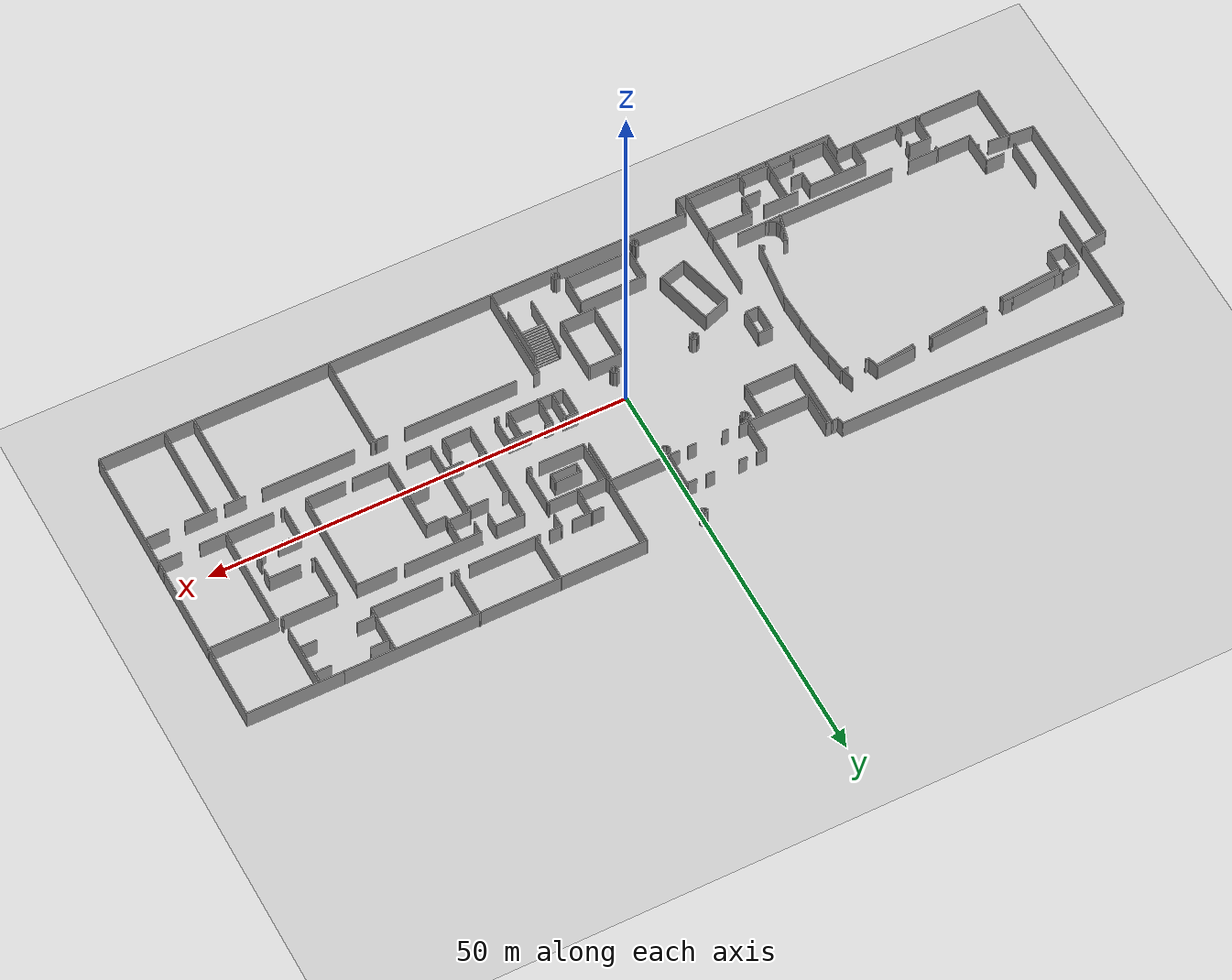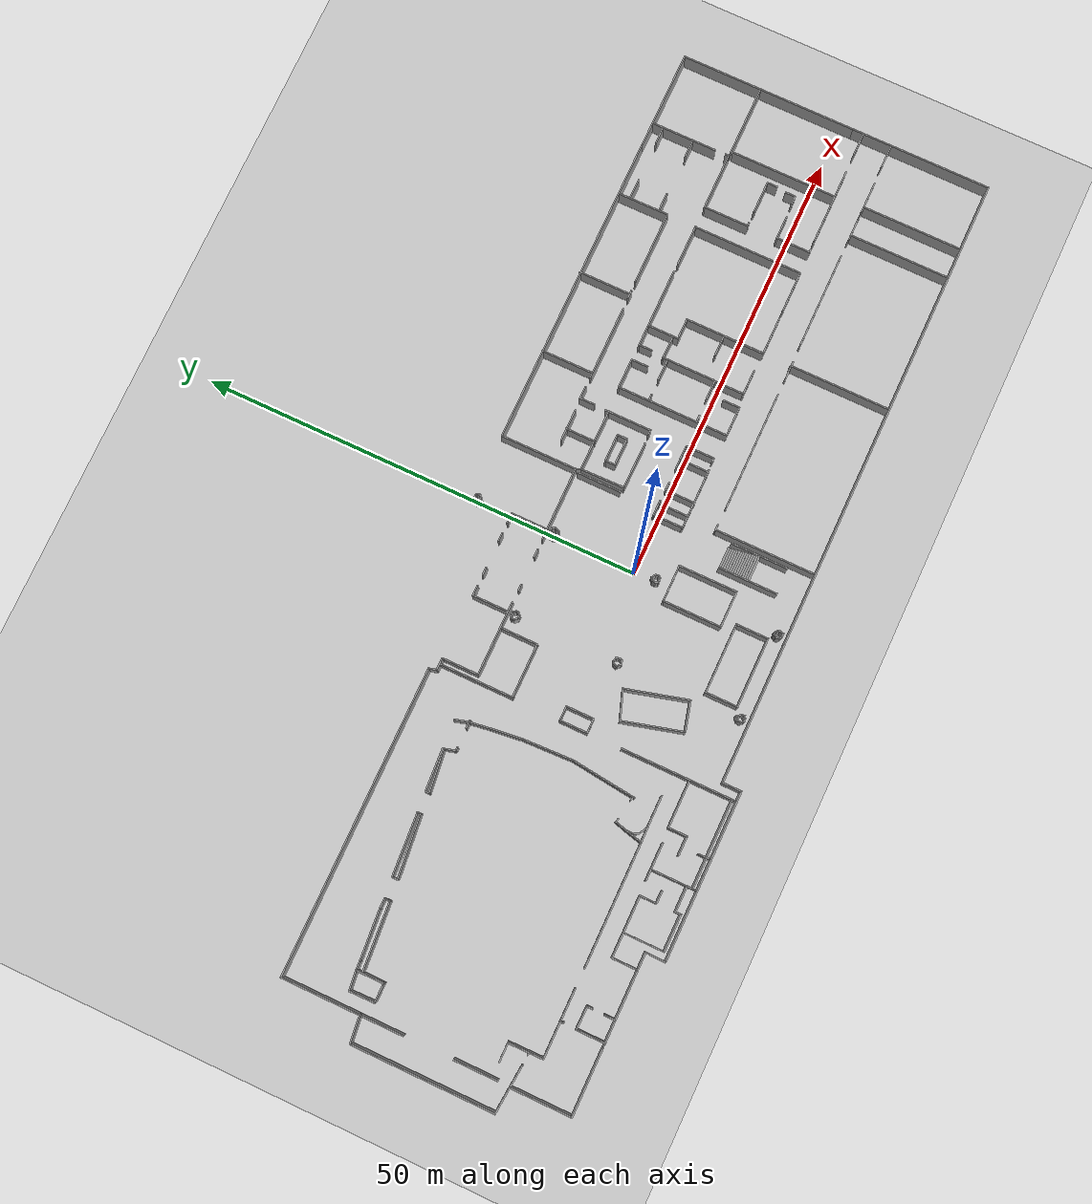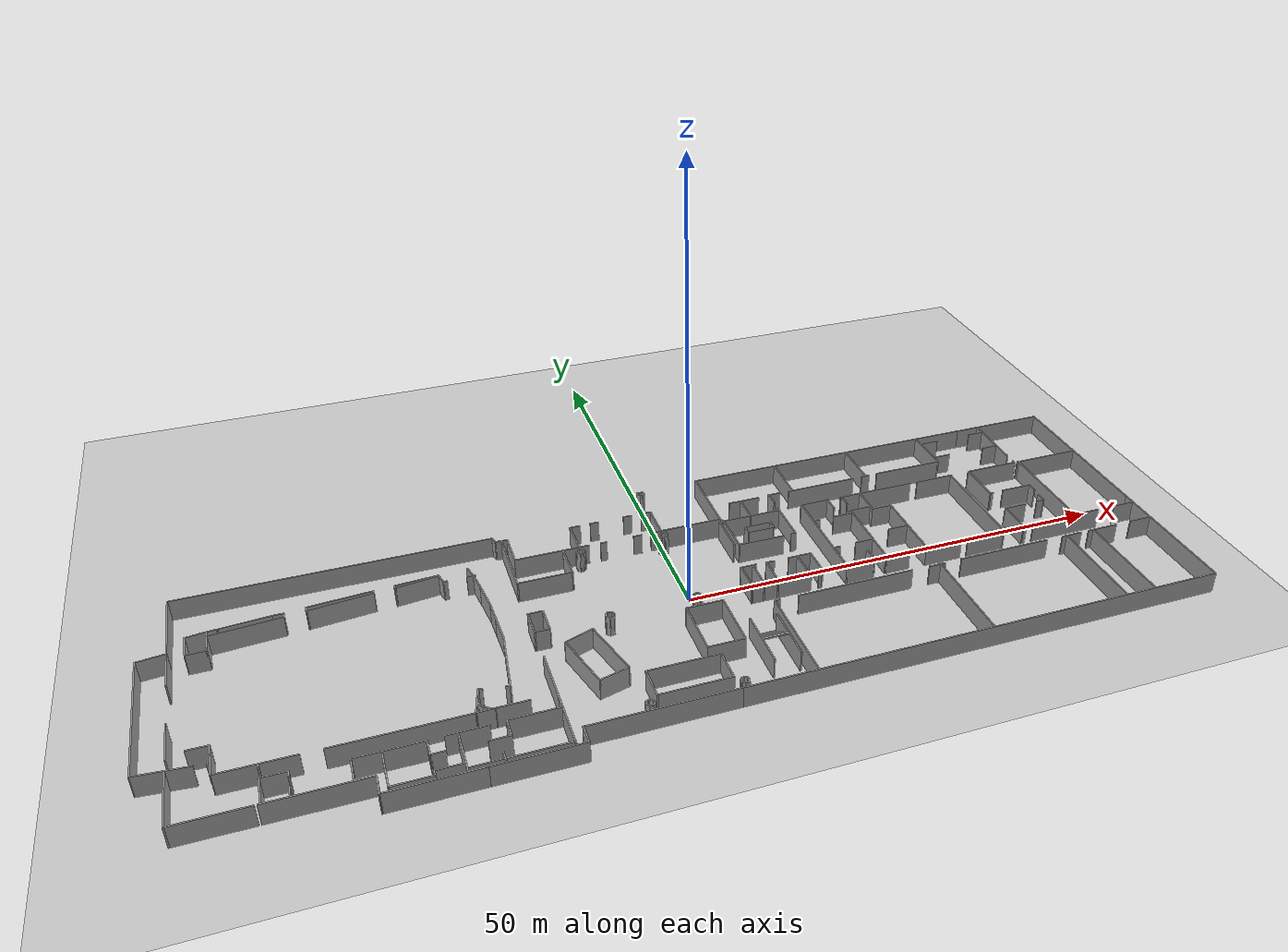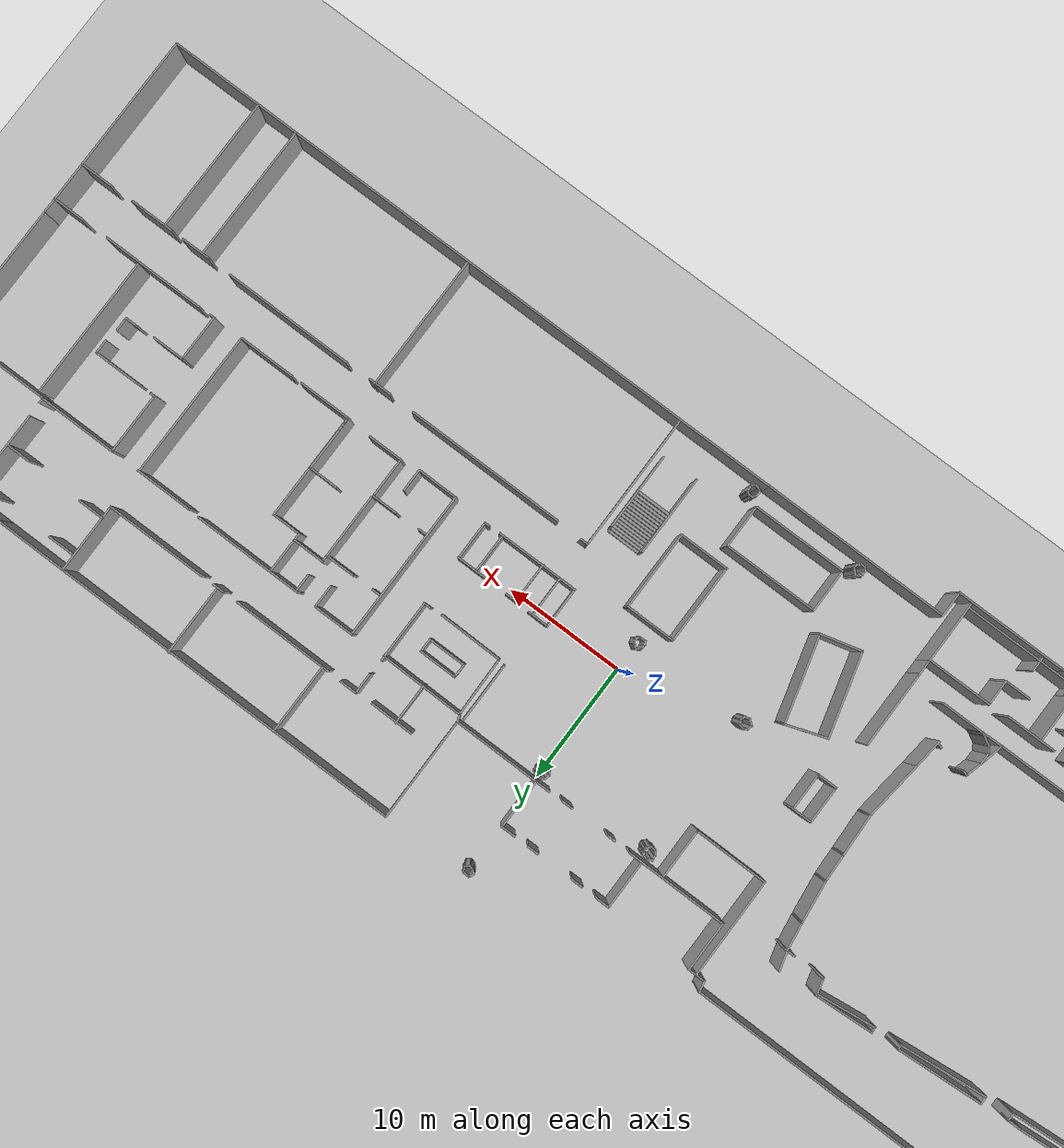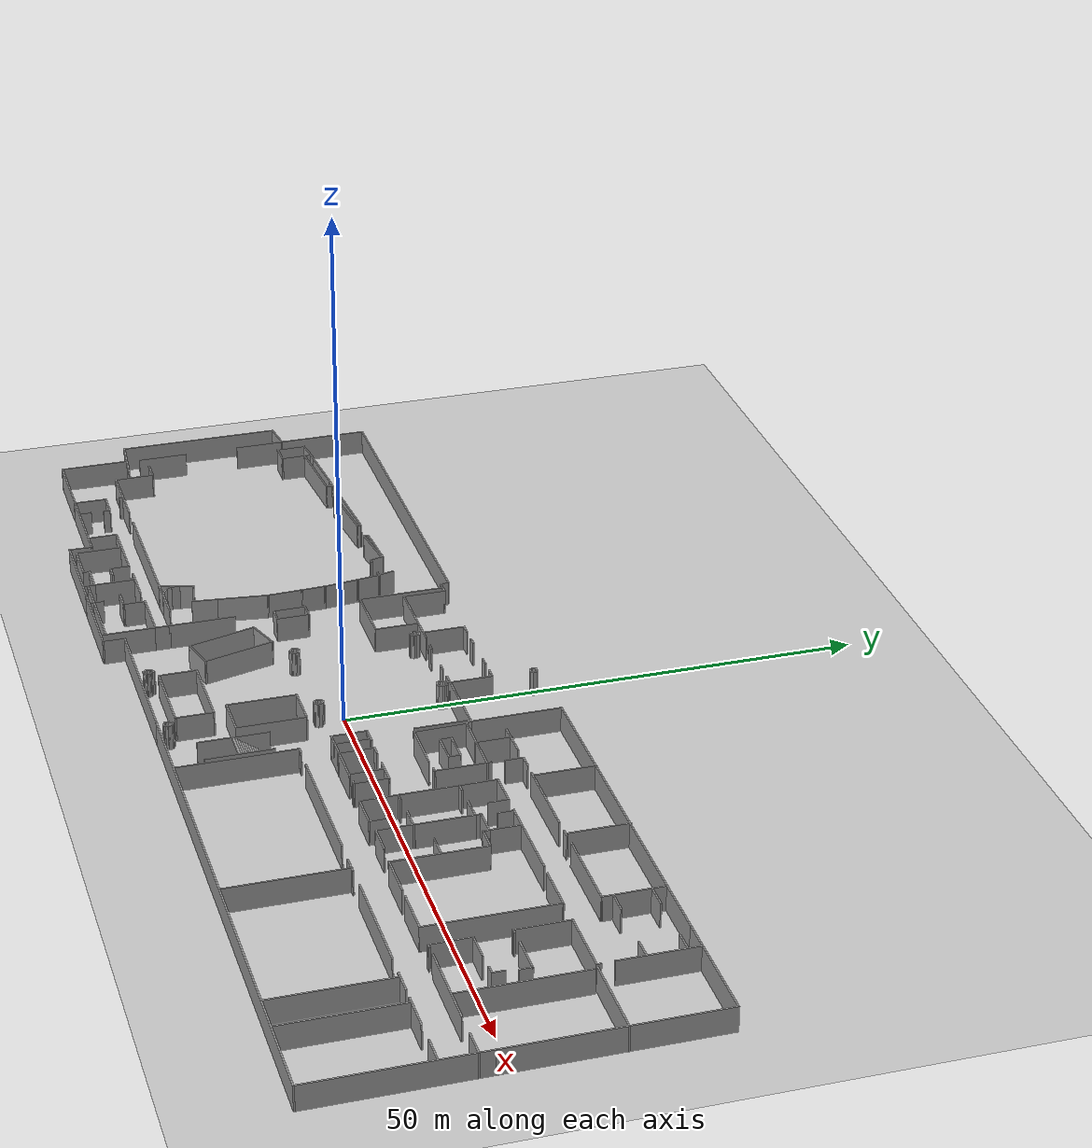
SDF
<sdf version="1.6">
 <world name="default">
  <light name="sun" type="directional">
   <pose>0 0 10 0 -0 0</pose>
   <diffuse>0.8 0.8 0.8 1</diffuse>
   <specular>0.2 0.2 0.2 1</specular>
   <attenuation>
    <range>1000</range>
    <constant>0.9</constant>
    <linear>0.01</linear>
    <quadratic>0.001</quadratic>
   </attenuation>
   <direction>-0.5 0.1 -0.9</direction>
   <spot><inner_angle>0</inner_angle><outer_angle>0</outer_angle><falloff>0</falloff></spot>
  </light>
  <model name="ground_plane">
   <static>1</static>
   <link name="link">
    <collision name="collision">
     <geometry><plane><normal>0 0 1</normal><size>100 100</size></plane></geometry>
     <surface>
      <contact><collide_bitmask>65535</collide_bitmask></contact>
      <friction><ode><mu>100</mu><mu2>50</mu2></ode></friction>
     </surface>
    </collision>
    <visual name="visual">
     <cast_shadows>0</cast_shadows>
     <geometry><plane><normal>0 0 1</normal><size>100 100</size></plane></geometry>
     <material>
      <script><uri>file://media/materials/scripts/gazebo.material</uri><name>Gazebo/Grey</name></script>
     </material>
    </visual>
   </link>
  </model>
  <gravity>0 0 -9.8</gravity>
  <magnetic_field>6e-06 2.3e-05 -4.2e-05</magnetic_field>
  <atmosphere type="adiabatic"/>
  <physics type="ode">
   <max_step_size>0.001</max_step_size>
   <real_time_factor>1</real_time_factor>
   <real_time_update_rate>1000</real_time_update_rate>
  </physics>
  <scene><ambient>0.4 0.4 0.4 1</ambient><background>0.7 0.7 0.7 1</background><shadows>1</shadows></scene>
  <spherical_coordinates>
   <surface_model>EARTH_WGS84</surface_model>
   <latitude_deg>0</latitude_deg>
   <longitude_deg>0</longitude_deg>
   <elevation>0</elevation>
   <heading_deg>0</heading_deg>
  </spherical_coordinates>
  <model name="L8_1st">
   <pose>-0.728485 -0.360932 0 0 -0 0</pose>
   <link name="Stairs_0">
    <visual name="Stairs_0_Visual_0">
     <pose>6.15456 -7.6847 0.083333 0 -0 0</pose>
     <geometry><box><size>2.83541 0.233333 0.166667</size></box></geometry>
     <material>
      <script><uri>file://media/materials/scripts/gazebo.material</uri><name>Gazebo/Grey</name></script>
      <ambient>1 1 1 1</ambient>
     </material>
     <meta><layer>0</layer></meta>
    </visual>
    <collision name="Stairs_0_Collision_0">
     <geometry><box><size>2.83541 0.233333 0.166667</size></box></geometry>
     <pose>6.15456 -7.6847 0.083333 0 -0 0</pose>
    </collision>
    <visual name="Stairs_0_Visual_1">
     <pose>6.15456 -7.91804 0.25 0 -0 0</pose>
     <geometry><box><size>2.83541 0.233333 0.166667</size></box></geometry>
     <material>
      <script><uri>file://media/materials/scripts/gazebo.material</uri><name>Gazebo/Grey</name></script>
      <ambient>1 1 1 1</ambient>
     </material>
     <meta><layer>0</layer></meta>
    </visual>
    <collision name="Stairs_0_Collision_1">
     <geometry><box><size>2.83541 0.233333 0.166667</size></box></geometry>
     <pose>6.15456 -7.91804 0.25 0 -0 0</pose>
    </collision>
    <visual name="Stairs_0_Visual_2">
     <pose>6.15456 -8.15137 0.416667 0 -0 0</pose>
     <geometry><box><size>2.83541 0.233333 0.166667</size></box></geometry>
     <material>
      <script><uri>file://media/materials/scripts/gazebo.material</uri><name>Gazebo/Grey</name></script>
      <ambient>1 1 1 1</ambient>
     </material>
     <meta><layer>0</layer></meta>
    </visual>
    <collision name="Stairs_0_Collision_2">
     <geometry><box><size>2.83541 0.233333 0.166667</size></box></geometry>
     <pose>6.15456 -8.15137 0.416667 0 -0 0</pose>
    </collision>
    <visual name="Stairs_0_Visual_3">
     <pose>6.15456 -8.3847 0.583333 0 -0 0</pose>
     <geometry><box><size>2.83541 0.233333 0.166667</size></box></geometry>
     <material>
      <script><uri>file://media/materials/scripts/gazebo.material</uri><name>Gazebo/Grey</name></script>
      <ambient>1 1 1 1</ambient>
     </material>
     <meta><layer>0</layer></meta>
    </visual>
    <collision name="Stairs_0_Collision_3">
     <geometry><box><size>2.83541 0.233333 0.166667</size></box></geometry>
     <pose>6.15456 -8.3847 0.583333 0 -0 0</pose>
    </collision>
    <visual name="Stairs_0_Visual_4">
     <pose>6.15456 -8.61804 0.75 0 -0 0</pose>
     <geometry><box><size>2.83541 0.233333 0.166667</size></box></geometry>
     <material>
      <script><uri>file://media/materials/scripts/gazebo.material</uri><name>Gazebo/Grey</name></script>
      <ambient>1 1 1 1</ambient>
     </material>
     <meta><layer>0</layer></meta>
    </visual>
    <collision name="Stairs_0_Collision_4">
     <geometry><box><size>2.83541 0.233333 0.166667</size></box></geometry>
     <pose>6.15456 -8.61804 0.75 0 -0 0</pose>
    </collision>
    <visual name="Stairs_0_Visual_5">
     <pose>6.15456 -8.85137 0.916667 0 -0 0</pose>
     <geometry><box><size>2.83541 0.233333 0.166667</size></box></geometry>
     <material>
      <script><uri>file://media/materials/scripts/gazebo.material</uri><name>Gazebo/Grey</name></script>
      <ambient>1 1 1 1</ambient>
     </material>
     <meta><layer>0</layer></meta>
    </visual>
    <collision name="Stairs_0_Collision_5">
     <geometry><box><size>2.83541 0.233333 0.166667</size></box></geometry>
     <pose>6.15456 -8.85137 0.916667 0 -0 0</pose>
    </collision>
    <visual name="Stairs_0_Visual_6">
     <pose>6.15456 -9.0847 1.08333 0 -0 0</pose>
     <geometry><box><size>2.83541 0.233333 0.166667</size></box></geometry>
     <material>
      <script><uri>file://media/materials/scripts/gazebo.material</uri><name>Gazebo/Grey</name></script>
      <ambient>1 1 1 1</ambient>
     </material>
     <meta><layer>0</layer></meta>
    </visual>
    <collision name="Stairs_0_Collision_6">
     <geometry><box><size>2.83541 0.233333 0.166667</size></box></geometry>
     <pose>6.15456 -9.0847 1.08333 0 -0 0</pose>
    </collision>
    <visual name="Stairs_0_Visual_7">
     <pose>6.15456 -9.31804 1.25 0 -0 0</pose>
     <geometry><box><size>2.83541 0.233333 0.166667</size></box></geometry>
     <material>
      <script><uri>file://media/materials/scripts/gazebo.material</uri><name>Gazebo/Grey</name></script>
      <ambient>1 1 1 1</ambient>
     </material>
     <meta><layer>0</layer></meta>
    </visual>
    <collision name="Stairs_0_Collision_7">
     <geometry><box><size>2.83541 0.233333 0.166667</size></box></geometry>
     <pose>6.15456 -9.31804 1.25 0 -0 0</pose>
    </collision>
    <visual name="Stairs_0_Visual_8">
     <pose>6.15456 -9.55137 1.41667 0 -0 0</pose>
     <geometry><box><size>2.83541 0.233333 0.166667</size></box></geometry>
     <material>
      <script><uri>file://media/materials/scripts/gazebo.material</uri><name>Gazebo/Grey</name></script>
      <ambient>1 1 1 1</ambient>
     </material>
     <meta><layer>0</layer></meta>
    </visual>
    <collision name="Stairs_0_Collision_8">
     <geometry><box><size>2.83541 0.233333 0.166667</size></box></geometry>
     <pose>6.15456 -9.55137 1.41667 0 -0 0</pose>
    </collision>
    <visual name="Stairs_0_Visual_9">
     <pose>6.15456 -9.7847 1.58333 0 -0 0</pose>
     <geometry><box><size>2.83541 0.233333 0.166667</size></box></geometry>
     <material>
      <script><uri>file://media/materials/scripts/gazebo.material</uri><name>Gazebo/Grey</name></script>
      <ambient>1 1 1 1</ambient>
     </material>
     <meta><layer>0</layer></meta>
    </visual>
    <collision name="Stairs_0_Collision_9">
     <geometry><box><size>2.83541 0.233333 0.166667</size></box></geometry>
     <pose>6.15456 -9.7847 1.58333 0 -0 0</pose>
    </collision>
    <visual name="Stairs_0_Visual_10">
     <pose>6.15456 -10.018 1.75 0 -0 0</pose>
     <geometry><box><size>2.83541 0.233333 0.166667</size></box></geometry>
     <material>
      <script><uri>file://media/materials/scripts/gazebo.material</uri><name>Gazebo/Grey</name></script>
      <ambient>1 1 1 1</ambient>
     </material>
     <meta><layer>0</layer></meta>
    </visual>
    <collision name="Stairs_0_Collision_10">
     <geometry><box><size>2.83541 0.233333 0.166667</size></box></geometry>
     <pose>6.15456 -10.018 1.75 0 -0 0</pose>
    </collision>
    <visual name="Stairs_0_Visual_11">
     <pose>6.15456 -10.2514 1.91667 0 -0 0</pose>
     <geometry><box><size>2.83541 0.233333 0.166667</size></box></geometry>
     <material>
      <script><uri>file://media/materials/scripts/gazebo.material</uri><name>Gazebo/Grey</name></script>
      <ambient>1 1 1 1</ambient>
     </material>
     <meta><layer>0</layer></meta>
    </visual>
    <collision name="Stairs_0_Collision_11">
     <geometry><box><size>2.83541 0.233333 0.166667</size></box></geometry>
     <pose>6.15456 -10.2514 1.91667 0 -0 0</pose>
    </collision>
    <visual name="Stairs_0_Visual_12">
     <pose>6.15456 -10.4847 2.08333 0 -0 0</pose>
     <geometry><box><size>2.83541 0.233333 0.166667</size></box></geometry>
     <material>
      <script><uri>file://media/materials/scripts/gazebo.material</uri><name>Gazebo/Grey</name></script>
      <ambient>1 1 1 1</ambient>
     </material>
     <meta><layer>0</layer></meta>
    </visual>
    <collision name="Stairs_0_Collision_12">
     <geometry><box><size>2.83541 0.233333 0.166667</size></box></geometry>
     <pose>6.15456 -10.4847 2.08333 0 -0 0</pose>
    </collision>
    <visual name="Stairs_0_Visual_13">
     <pose>6.15456 -10.718 2.25 0 -0 0</pose>
     <geometry><box><size>2.83541 0.233333 0.166667</size></box></geometry>
     <material>
      <script><uri>file://media/materials/scripts/gazebo.material</uri><name>Gazebo/Grey</name></script>
      <ambient>1 1 1 1</ambient>
     </material>
     <meta><layer>0</layer></meta>
    </visual>
    <collision name="Stairs_0_Collision_13">
     <geometry><box><size>2.83541 0.233333 0.166667</size></box></geometry>
     <pose>6.15456 -10.718 2.25 0 -0 0</pose>
    </collision>
    <visual name="Stairs_0_Visual_14">
     <pose>6.15456 -10.9514 2.41667 0 -0 0</pose>
     <geometry><box><size>2.83541 0.233333 0.166667</size></box></geometry>
     <material>
      <script><uri>file://media/materials/scripts/gazebo.material</uri><name>Gazebo/Grey</name></script>
      <ambient>1 1 1 1</ambient>
     </material>
     <meta><layer>0</layer></meta>
    </visual>
    <collision name="Stairs_0_Collision_14">
     <geometry><box><size>2.83541 0.233333 0.166667</size></box></geometry>
     <pose>6.15456 -10.9514 2.41667 0 -0 0</pose>
    </collision>
   </link>
   <link name="Wall_0">
    <collision name="Wall_0_Collision">
     <geometry><box><size>34.75 0.15 2.5</size></box></geometry>
     <pose>0 0 1.25 0 -0 0</pose>
    </collision>
    <visual name="Wall_0_Visual">
     <pose>0 0 1.25 0 -0 0</pose>
     <geometry><box><size>34.75 0.15 2.5</size></box></geometry>
     <material>
      <script><uri>file://media/materials/scripts/gazebo.material</uri><name>Gazebo/Grey</name></script>
      <ambient>1 1 1 1</ambient>
     </material>
     <meta><layer>0</layer></meta>
    </visual>
    <pose>-35.0099 15.4434 0 0 -0 0</pose>
   </link>
   <link name="Wall_1">
    <collision name="Wall_1_Collision">
     <geometry><box><size>1 0.15 2.5</size></box></geometry>
     <pose>0 0 1.25 0 -0 0</pose>
    </collision>
    <visual name="Wall_1_Visual">
     <pose>0 0 1.25 0 -0 0</pose>
     <geometry><box><size>1 0.15 2.5</size></box></geometry>
     <material>
      <script><uri>file://media/materials/scripts/gazebo.material</uri><name>Gazebo/Grey</name></script>
      <ambient>1 1 1 1</ambient>
     </material>
     <meta><layer>0</layer></meta>
    </visual>
    <pose>-17.5999 15.0329 0 0 -0 -1.309</pose>
   </link>
   <link name="Wall_10">
    <collision name="Wall_10_Collision">
     <geometry><box><size>1.25 0.15 2.5</size></box></geometry>
     <pose>0 0 1.25 0 -0 0</pose>
    </collision>
    <visual name="Wall_10_Visual">
     <pose>0 0 1.25 0 -0 0</pose>
     <geometry><box><size>1.25 0.15 2.5</size></box></geometry>
     <material>
      <script><uri>file://media/materials/scripts/gazebo.material</uri><name>Gazebo/Grey</name></script>
      <ambient>1 1 1 1</ambient>
     </material>
     <meta><layer>0</layer></meta>
    </visual>
    <pose>-8.28087 14.5624 0 0 -0 0</pose>
   </link>
   <link name="Wall_100">
    <collision name="Wall_100_Collision">
     <geometry><box><size>1 0.15 2.5</size></box></geometry>
     <pose>0 0 1.25 0 -0 0</pose>
    </collision>
    <visual name="Wall_100_Visual">
     <pose>0 0 1.25 0 -0 0</pose>
     <geometry><box><size>1 0.15 2.5</size></box></geometry>
     <material>
      <script><uri>file://media/materials/scripts/gazebo.material</uri><name>Gazebo/Grey</name></script>
      <ambient>1 1 1 1</ambient>
     </material>
     <meta><layer>0</layer></meta>
    </visual>
    <pose>-21.2402 9.25126 0 0 -0 0</pose>
   </link>
   <link name="Wall_102">
    <collision name="Wall_102_Collision">
     <geometry><box><size>1.75 0.15 2.5</size></box></geometry>
     <pose>0 0 1.25 0 -0 0</pose>
    </collision>
    <visual name="Wall_102_Visual">
     <pose>0 0 1.25 0 -0 0</pose>
     <geometry><box><size>1.75 0.15 2.5</size></box></geometry>
     <material>
      <script><uri>file://media/materials/scripts/gazebo.material</uri><name>Gazebo/Grey</name></script>
      <ambient>1 1 1 1</ambient>
     </material>
     <meta><layer>0</layer></meta>
    </visual>
    <pose>-21.1857 9.99059 0 0 -0 -1.309</pose>
   </link>
   <link name="Wall_104">
    <collision name="Wall_104_Collision">
     <geometry><box><size>2.42038 0.15 2.5</size></box></geometry>
     <pose>0 0 1.25 0 -0 0</pose>
    </collision>
    <visual name="Wall_104_Visual">
     <pose>0 0 1.25 0 -0 0</pose>
     <geometry><box><size>2.42038 0.15 2.5</size></box></geometry>
     <material>
      <script><uri>file://media/materials/scripts/gazebo.material</uri><name>Gazebo/Grey</name></script>
      <ambient>1 1 1 1</ambient>
     </material>
     <meta><layer>0</layer></meta>
    </visual>
    <pose>-20.8186 8.094 0 0 -0 1.71224</pose>
   </link>
   <link name="Wall_106">
    <collision name="Wall_106_Collision">
     <geometry><box><size>3.56872 0.15 2.5</size></box></geometry>
     <pose>0 0 1.25 0 -0 0</pose>
    </collision>
    <visual name="Wall_106_Visual">
     <pose>0 0 1.25 0 -0 0</pose>
     <geometry><box><size>3.56872 0.15 2.5</size></box></geometry>
     <material>
      <script><uri>file://media/materials/scripts/gazebo.material</uri><name>Gazebo/Grey</name></script>
      <ambient>1 1 1 1</ambient>
     </material>
     <meta><layer>0</layer></meta>
    </visual>
    <pose>-20.4597 5.27239 0 0 -0 1.68738</pose>
   </link>
   <link name="Wall_108">
    <collision name="Wall_108_Collision">
     <geometry><box><size>2.47667 0.15 2.5</size></box></geometry>
     <pose>0 0 1.25 0 -0 0</pose>
    </collision>
    <visual name="Wall_108_Visual">
     <pose>0 0 1.25 0 -0 0</pose>
     <geometry><box><size>2.47667 0.15 2.5</size></box></geometry>
     <material>
      <script><uri>file://media/materials/scripts/gazebo.material</uri><name>Gazebo/Grey</name></script>
      <ambient>1 1 1 1</ambient>
     </material>
     <meta><layer>0</layer></meta>
    </visual>
    <pose>-20.215 2.4122 0 0 -0 1.61025</pose>
   </link>
   <link name="Wall_110">
    <collision name="Wall_110_Collision">
     <geometry><box><size>3.57829 0.15 2.5</size></box></geometry>
     <pose>0 0 1.25 0 -0 0</pose>
    </collision>
    <visual name="Wall_110_Visual">
     <pose>0 0 1.25 0 -0 0</pose>
     <geometry><box><size>3.57829 0.15 2.5</size></box></geometry>
     <material>
      <script><uri>file://media/materials/scripts/gazebo.material</uri><name>Gazebo/Grey</name></script>
      <ambient>1 1 1 1</ambient>
     </material>
     <meta><layer>0</layer></meta>
    </visual>
    <pose>-20.1079 -0.46328 0 0 -0 1.6065</pose>
   </link>
   <link name="Wall_112">
    <collision name="Wall_112_Collision">
     <geometry><box><size>5.07883 0.15 2.5</size></box></geometry>
     <pose>0 0 1.25 0 -0 0</pose>
    </collision>
    <visual name="Wall_112_Visual">
     <pose>0 0 1.25 0 -0 0</pose>
     <geometry><box><size>5.07883 0.15 2.5</size></box></geometry>
     <material>
      <script><uri>file://media/materials/scripts/gazebo.material</uri><name>Gazebo/Grey</name></script>
      <ambient>1 1 1 1</ambient>
     </material>
     <meta><layer>0</layer></meta>
    </visual>
    <pose>-20.3373 -4.62355 0 0 -0 1.4526</pose>
   </link>
   <link name="Wall_114">
    <collision name="Wall_114_Collision">
     <geometry><box><size>2.58591 0.15 2.5</size></box></geometry>
     <pose>0 0 1.25 0 -0 0</pose>
    </collision>
    <visual name="Wall_114_Visual">
     <pose>0 0 1.25 0 -0 0</pose>
     <geometry><box><size>2.58591 0.15 2.5</size></box></geometry>
     <material>
      <script><uri>file://media/materials/scripts/gazebo.material</uri><name>Gazebo/Grey</name></script>
      <ambient>1 1 1 1</ambient>
     </material>
     <meta><layer>0</layer></meta>
    </visual>
    <pose>-20.7635 -8.28115 0 0 -0 1.45924</pose>
   </link>
   <link name="Wall_118">
    <collision name="Wall_118_Collision">
     <geometry><box><size>0.5 0.15 2.5</size></box></geometry>
     <pose>0 0 1.25 0 -0 0</pose>
    </collision>
    <visual name="Wall_118_Visual">
     <pose>0 0 1.25 0 -0 0</pose>
     <geometry><box><size>0.5 0.15 2.5</size></box></geometry>
     <material>
      <script><uri>file://media/materials/scripts/gazebo.material</uri><name>Gazebo/Grey</name></script>
      <ambient>1 1 1 1</ambient>
     </material>
     <meta><layer>0</layer></meta>
    </visual>
    <pose>-21.0984 -9.30152 0 0 -0 -0.261799</pose>
   </link>
   <link name="Wall_12">
    <collision name="Wall_12_Collision">
     <geometry><box><size>1.25 0.15 2.5</size></box></geometry>
     <pose>0 0 1.25 0 -0 0</pose>
    </collision>
    <visual name="Wall_12_Visual">
     <pose>0 0 1.25 0 -0 0</pose>
     <geometry><box><size>1.25 0.15 2.5</size></box></geometry>
     <material>
      <script><uri>file://media/materials/scripts/gazebo.material</uri><name>Gazebo/Grey</name></script>
      <ambient>1 1 1 1</ambient>
     </material>
     <meta><layer>0</layer></meta>
    </visual>
    <pose>0.254276 14.5952 0 0 -0 0</pose>
   </link>
   <link name="Wall_120">
    <collision name="Wall_120_Collision">
     <geometry><box><size>0.5 0.15 2.5</size></box></geometry>
     <pose>0 0 1.25 0 -0 0</pose>
    </collision>
    <visual name="Wall_120_Visual">
     <pose>0 0 1.25 0 -0 0</pose>
     <geometry><box><size>0.5 0.15 2.5</size></box></geometry>
     <material>
      <script><uri>file://media/materials/scripts/gazebo.material</uri><name>Gazebo/Grey</name></script>
      <ambient>1 1 1 1</ambient>
     </material>
     <meta><layer>0</layer></meta>
    </visual>
    <pose>-23.7509 -8.81418 0 0 -0 2.87979</pose>
   </link>
   <link name="Wall_121">
    <collision name="Wall_121_Collision">
     <geometry><box><size>1.5 0.15 2.5</size></box></geometry>
     <pose>0 0 1.25 0 -0 0</pose>
    </collision>
    <visual name="Wall_121_Visual">
     <pose>0 0 1.25 0 -0 0</pose>
     <geometry><box><size>1.5 0.15 2.5</size></box></geometry>
     <material>
      <script><uri>file://media/materials/scripts/gazebo.material</uri><name>Gazebo/Grey</name></script>
      <ambient>1 1 1 1</ambient>
     </material>
     <meta><layer>0</layer></meta>
    </visual>
    <pose>-24.0946 -9.42089 0 0 -0 -1.8326</pose>
   </link>
   <link name="Wall_123">
    <collision name="Wall_123_Collision">
     <geometry><box><size>1 0.15 2.5</size></box></geometry>
     <pose>0 0 1.25 0 -0 0</pose>
    </collision>
    <visual name="Wall_123_Visual">
     <pose>0 0 1.25 0 -0 0</pose>
     <geometry><box><size>1 0.15 2.5</size></box></geometry>
     <material>
      <script><uri>file://media/materials/scripts/gazebo.material</uri><name>Gazebo/Grey</name></script>
      <ambient>1 1 1 1</ambient>
     </material>
     <meta><layer>0</layer></meta>
    </visual>
    <pose>-24.2693 -10.4979 0 0 -0 -1.5708</pose>
   </link>
   <link name="Wall_124">
    <collision name="Wall_124_Collision">
     <geometry><box><size>0.75 0.15 2.5</size></box></geometry>
     <pose>0 0 1.25 0 -0 0</pose>
    </collision>
    <visual name="Wall_124_Visual">
     <pose>0 0 1.25 0 -0 0</pose>
     <geometry><box><size>0.75 0.15 2.5</size></box></geometry>
     <material>
      <script><uri>file://media/materials/scripts/gazebo.material</uri><name>Gazebo/Grey</name></script>
      <ambient>1 1 1 1</ambient>
     </material>
     <meta><layer>0</layer></meta>
    </visual>
    <pose>-24.1193 -11.1827 0 0 -0 -1.0472</pose>
   </link>
   <link name="Wall_125">
    <collision name="Wall_125_Collision">
     <geometry><box><size>1 0.15 2.5</size></box></geometry>
     <pose>0 0 1.25 0 -0 0</pose>
    </collision>
    <visual name="Wall_125_Visual">
     <pose>0 0 1.25 0 -0 0</pose>
     <geometry><box><size>1 0.15 2.5</size></box></geometry>
     <material>
      <script><uri>file://media/materials/scripts/gazebo.material</uri><name>Gazebo/Grey</name></script>
      <ambient>1 1 1 1</ambient>
     </material>
     <meta><layer>0</layer></meta>
    </visual>
    <pose>-23.6012 -11.655 0 0 -0 -0.523599</pose>
   </link>
   <link name="Wall_126">
    <collision name="Wall_126_Collision">
     <geometry><box><size>0.5 0.15 2.5</size></box></geometry>
     <pose>0 0 1.25 0 -0 0</pose>
    </collision>
    <visual name="Wall_126_Visual">
     <pose>0 0 1.25 0 -0 0</pose>
     <geometry><box><size>0.5 0.15 2.5</size></box></geometry>
     <material>
      <script><uri>file://media/materials/scripts/gazebo.material</uri><name>Gazebo/Grey</name></script>
      <ambient>1 1 1 1</ambient>
     </material>
     <meta><layer>0</layer></meta>
    </visual>
    <pose>-23.0641 -11.9128 0 0 -0 -0.261799</pose>
   </link>
   <link name="Wall_127">
    <collision name="Wall_127_Collision">
     <geometry><box><size>3.5 0.15 2.5</size></box></geometry>
     <pose>0 0 1.25 0 -0 0</pose>
    </collision>
    <visual name="Wall_127_Visual">
     <pose>0 0 1.25 0 -0 0</pose>
     <geometry><box><size>3.5 0.15 2.5</size></box></geometry>
     <material>
      <script><uri>file://media/materials/scripts/gazebo.material</uri><name>Gazebo/Grey</name></script>
      <ambient>1 1 1 1</ambient>
     </material>
     <meta><layer>0</layer></meta>
    </visual>
    <pose>-21.2201 -11.9581 0 0 -0 0</pose>
   </link>
   <link name="Wall_129">
    <collision name="Wall_129_Collision">
     <geometry><box><size>2.14193 0.15 2.5</size></box></geometry>
     <pose>0 0 1.25 0 -0 0</pose>
    </collision>
    <visual name="Wall_129_Visual">
     <pose>0 0 1.25 0 -0 0</pose>
     <geometry><box><size>2.14193 0.15 2.5</size></box></geometry>
     <material>
      <script><uri>file://media/materials/scripts/gazebo.material</uri><name>Gazebo/Grey</name></script>
      <ambient>1 1 1 1</ambient>
     </material>
     <meta><layer>0</layer></meta>
    </visual>
    <pose>-24.5075 -11.04 0 0 -0 1.32933</pose>
   </link>
   <link name="Wall_13">
    <collision name="Wall_13_Collision">
     <geometry><box><size>4.25 0.15 2.5</size></box></geometry>
     <pose>0 0 1.25 0 -0 0</pose>
    </collision>
    <visual name="Wall_13_Visual">
     <pose>0 0 1.25 0 -0 0</pose>
     <geometry><box><size>4.25 0.15 2.5</size></box></geometry>
     <material>
      <script><uri>file://media/materials/scripts/gazebo.material</uri><name>Gazebo/Grey</name></script>
      <ambient>1 1 1 1</ambient>
     </material>
     <meta><layer>0</layer></meta>
    </visual>
    <pose>0.804276 12.5452 0 0 -0 -1.5708</pose>
   </link>
   <link name="Wall_131">
    <collision name="Wall_131_Collision">
     <geometry><box><size>2.00116 0.15 2.5</size></box></geometry>
     <pose>0 0 1.25 0 -0 0</pose>
    </collision>
    <visual name="Wall_131_Visual">
     <pose>0 0 1.25 0 -0 0</pose>
     <geometry><box><size>2.00116 0.15 2.5</size></box></geometry>
     <material>
      <script><uri>file://media/materials/scripts/gazebo.material</uri><name>Gazebo/Grey</name></script>
      <ambient>1 1 1 1</ambient>
     </material>
     <meta><layer>0</layer></meta>
    </visual>
    <pose>-23.8204 -11.9826 0 0 -0 0.026438</pose>
   </link>
   <link name="Wall_133">
    <collision name="Wall_133_Collision">
     <geometry><box><size>14.0279 0.15 2.5</size></box></geometry>
     <pose>0 0 1.25 0 -0 0</pose>
    </collision>
    <visual name="Wall_133_Visual">
     <pose>0 0 1.25 0 -0 0</pose>
     <geometry><box><size>14.0279 0.15 2.5</size></box></geometry>
     <material>
      <script><uri>file://media/materials/scripts/gazebo.material</uri><name>Gazebo/Grey</name></script>
      <ambient>1 1 1 1</ambient>
     </material>
     <meta><layer>0</layer></meta>
    </visual>
    <pose>-31.6846 -12.0193 0 0 -0 0.001774</pose>
   </link>
   <link name="Wall_135">
    <collision name="Wall_135_Collision">
     <geometry><box><size>7.75 0.15 2.5</size></box></geometry>
     <pose>0 0 1.25 0 -0 0</pose>
    </collision>
    <visual name="Wall_135_Visual">
     <pose>0 0 1.25 0 -0 0</pose>
     <geometry><box><size>7.75 0.15 2.5</size></box></geometry>
     <material>
      <script><uri>file://media/materials/scripts/gazebo.material</uri><name>Gazebo/Grey</name></script>
      <ambient>1 1 1 1</ambient>
     </material>
     <meta><layer>0</layer></meta>
    </visual>
    <pose>-44.6466 -12.0076 0 0 -0 3.14159</pose>
   </link>
   <link name="Wall_137">
    <collision name="Wall_137_Collision">
     <geometry><box><size>2.25 0.15 2.5</size></box></geometry>
     <pose>0 0 1.25 0 -0 0</pose>
    </collision>
    <visual name="Wall_137_Visual">
     <pose>0 0 1.25 0 -0 0</pose>
     <geometry><box><size>2.25 0.15 2.5</size></box></geometry>
     <material>
      <script><uri>file://media/materials/scripts/gazebo.material</uri><name>Gazebo/Grey</name></script>
      <ambient>1 1 1 1</ambient>
     </material>
     <meta><layer>0</layer></meta>
    </visual>
    <pose>-49.527 -8.11198 0 0 -0 0</pose>
   </link>
   <link name="Wall_138">
    <collision name="Wall_138_Collision">
     <geometry><box><size>4.04566 0.15 2.5</size></box></geometry>
     <pose>0 0 1.25 0 -0 0</pose>
    </collision>
    <visual name="Wall_138_Visual">
     <pose>0 0 1.25 0 -0 0</pose>
     <geometry><box><size>4.04566 0.15 2.5</size></box></geometry>
     <material>
      <script><uri>file://media/materials/scripts/gazebo.material</uri><name>Gazebo/Grey</name></script>
      <ambient>1 1 1 1</ambient>
     </material>
     <meta><layer>0</layer></meta>
    </visual>
    <pose>-48.4694 -10.0598 0 0 -0 -1.55909</pose>
   </link>
   <link name="Wall_140">
    <collision name="Wall_140_Collision">
     <geometry><box><size>2.54872 0.15 2.5</size></box></geometry>
     <pose>0 0 1.25 0 -0 0</pose>
    </collision>
    <visual name="Wall_140_Visual">
     <pose>0 0 1.25 0 -0 0</pose>
     <geometry><box><size>2.54872 0.15 2.5</size></box></geometry>
     <material>
      <script><uri>file://media/materials/scripts/gazebo.material</uri><name>Gazebo/Grey</name></script>
      <ambient>1 1 1 1</ambient>
     </material>
     <meta><layer>0</layer></meta>
    </visual>
    <pose>-51.1714 -10.2292 0 0 -0 3.0523</pose>
   </link>
   <link name="Wall_142">
    <collision name="Wall_142_Collision">
     <geometry><box><size>0.25 0.15 2.5</size></box></geometry>
     <pose>0 0 1.25 0 -0 0</pose>
    </collision>
    <visual name="Wall_142_Visual">
     <pose>0 0 1.25 0 -0 0</pose>
     <geometry><box><size>0.25 0.15 2.5</size></box></geometry>
     <material>
      <script><uri>file://media/materials/scripts/gazebo.material</uri><name>Gazebo/Grey</name></script>
      <ambient>1 1 1 1</ambient>
     </material>
     <meta><layer>0</layer></meta>
    </visual>
    <pose>-48.6766 -10.4159 0 0 -0 0</pose>
   </link>
   <link name="Wall_144">
    <collision name="Wall_144_Collision">
     <geometry><box><size>0.5 0.15 2.5</size></box></geometry>
     <pose>0 0 1.25 0 -0 0</pose>
    </collision>
    <visual name="Wall_144_Visual">
     <pose>0 0 1.25 0 -0 0</pose>
     <geometry><box><size>0.5 0.15 2.5</size></box></geometry>
     <material>
      <script><uri>file://media/materials/scripts/gazebo.material</uri><name>Gazebo/Grey</name></script>
      <ambient>1 1 1 1</ambient>
     </material>
     <meta><layer>0</layer></meta>
    </visual>
    <pose>-44.4258 -12.1754 0 0 -0 -1.5708</pose>
   </link>
   <link name="Wall_146">
    <collision name="Wall_146_Collision">
     <geometry><box><size>0.75 0.15 2.5</size></box></geometry>
     <pose>0 0 1.25 0 -0 0</pose>
    </collision>
    <visual name="Wall_146_Visual">
     <pose>0 0 1.25 0 -0 0</pose>
     <geometry><box><size>0.75 0.15 2.5</size></box></geometry>
     <material>
      <script><uri>file://media/materials/scripts/gazebo.material</uri><name>Gazebo/Grey</name></script>
      <ambient>1 1 1 1</ambient>
     </material>
     <meta><layer>0</layer></meta>
    </visual>
    <pose>-41.9175 -14.1278 0 0 -0 1.5708</pose>
   </link>
   <link name="Wall_147">
    <collision name="Wall_147_Collision">
     <geometry><box><size>2.68428 0.15 2.5</size></box></geometry>
     <pose>0 0 1.25 0 -0 0</pose>
    </collision>
    <visual name="Wall_147_Visual">
     <pose>0 0 1.25 0 -0 0</pose>
     <geometry><box><size>2.68428 0.15 2.5</size></box></geometry>
     <material>
      <script><uri>file://media/materials/scripts/gazebo.material</uri><name>Gazebo/Grey</name></script>
      <ambient>1 1 1 1</ambient>
     </material>
     <meta><layer>0</layer></meta>
    </visual>
    <pose>-43.1843 -13.8125 0 0 -0 3.12952</pose>
   </link>
   <link name="Wall_148">
    <collision name="Wall_148_Collision">
     <geometry><box><size>3.25 0.15 2.5</size></box></geometry>
     <pose>0 0 1.25 0 -0 0</pose>
    </collision>
    <visual name="Wall_148_Visual">
     <pose>0 0 1.25 0 -0 0</pose>
     <geometry><box><size>3.25 0.15 2.5</size></box></geometry>
     <material>
      <script><uri>file://media/materials/scripts/gazebo.material</uri><name>Gazebo/Grey</name></script>
      <ambient>1 1 1 1</ambient>
     </material>
     <meta><layer>0</layer></meta>
    </visual>
    <pose>-44.4511 -15.3778 0 0 -0 -1.5708</pose>
   </link>
   <link name="Wall_15">
    <collision name="Wall_15_Collision">
     <geometry><box><size>0.75 0.15 2.5</size></box></geometry>
     <pose>0 0 1.25 0 -0 0</pose>
    </collision>
    <visual name="Wall_15_Visual">
     <pose>0 0 1.25 0 -0 0</pose>
     <geometry><box><size>0.75 0.15 2.5</size></box></geometry>
     <material>
      <script><uri>file://media/materials/scripts/gazebo.material</uri><name>Gazebo/Grey</name></script>
      <ambient>1 1 1 1</ambient>
     </material>
     <meta><layer>0</layer></meta>
    </visual>
    <pose>-6.01231 10.4676 0 0 -0 0</pose>
   </link>
   <link name="Wall_150">
    <collision name="Wall_150_Collision">
     <geometry><box><size>1.25 0.15 2.5</size></box></geometry>
     <pose>0 0 1.25 0 -0 0</pose>
    </collision>
    <visual name="Wall_150_Visual">
     <pose>0 0 1.25 0 -0 0</pose>
     <geometry><box><size>1.25 0.15 2.5</size></box></geometry>
     <material>
      <script><uri>file://media/materials/scripts/gazebo.material</uri><name>Gazebo/Grey</name></script>
      <ambient>1 1 1 1</ambient>
     </material>
     <meta><layer>0</layer></meta>
    </visual>
    <pose>-41.9639 -16.3838 0 0 -0 -1.5708</pose>
   </link>
   <link name="Wall_152">
    <collision name="Wall_152_Collision">
     <geometry><box><size>3 0.15 2.5</size></box></geometry>
     <pose>0 0 1.25 0 -0 0</pose>
    </collision>
    <visual name="Wall_152_Visual">
     <pose>0 0 1.25 0 -0 0</pose>
     <geometry><box><size>3 0.15 2.5</size></box></geometry>
     <material>
      <script><uri>file://media/materials/scripts/gazebo.material</uri><name>Gazebo/Grey</name></script>
      <ambient>1 1 1 1</ambient>
     </material>
     <meta><layer>0</layer></meta>
    </visual>
    <pose>-36.5188 -15.5406 0 0 -0 1.5708</pose>
   </link>
   <link name="Wall_153">
    <collision name="Wall_153_Collision">
     <geometry><box><size>7 0.15 2.5</size></box></geometry>
     <pose>0 0 1.25 0 -0 0</pose>
    </collision>
    <visual name="Wall_153_Visual">
     <pose>0 0 1.25 0 -0 0</pose>
     <geometry><box><size>7 0.15 2.5</size></box></geometry>
     <material>
      <script><uri>file://media/materials/scripts/gazebo.material</uri><name>Gazebo/Grey</name></script>
      <ambient>1 1 1 1</ambient>
     </material>
     <meta><layer>0</layer></meta>
    </visual>
    <pose>-33.0938 -14.1156 0 0 -0 0</pose>
   </link>
   <link name="Wall_154">
    <collision name="Wall_154_Collision">
     <geometry><box><size>2 0.15 2.5</size></box></geometry>
     <pose>0 0 1.25 0 -0 0</pose>
    </collision>
    <visual name="Wall_154_Visual">
     <pose>0 0 1.25 0 -0 0</pose>
     <geometry><box><size>2 0.15 2.5</size></box></geometry>
     <material>
      <script><uri>file://media/materials/scripts/gazebo.material</uri><name>Gazebo/Grey</name></script>
      <ambient>1 1 1 1</ambient>
     </material>
     <meta><layer>0</layer></meta>
    </visual>
    <pose>-29.6688 -15.0406 0 0 -0 -1.5708</pose>
   </link>
   <link name="Wall_155">
    <collision name="Wall_155_Collision">
     <geometry><box><size>1.5 0.15 2.5</size></box></geometry>
     <pose>0 0 1.25 0 -0 0</pose>
    </collision>
    <visual name="Wall_155_Visual">
     <pose>0 0 1.25 0 -0 0</pose>
     <geometry><box><size>1.5 0.15 2.5</size></box></geometry>
     <material>
      <script><uri>file://media/materials/scripts/gazebo.material</uri><name>Gazebo/Grey</name></script>
      <ambient>1 1 1 1</ambient>
     </material>
     <meta><layer>0</layer></meta>
    </visual>
    <pose>-28.9938 -15.9656 0 0 -0 0</pose>
   </link>
   <link name="Wall_157">
    <collision name="Wall_157_Collision">
     <geometry><box><size>4.25 0.15 2.5</size></box></geometry>
     <pose>0 0 1.25 0 -0 0</pose>
    </collision>
    <visual name="Wall_157_Visual">
     <pose>0 0 1.25 0 -0 0</pose>
     <geometry><box><size>4.25 0.15 2.5</size></box></geometry>
     <material>
      <script><uri>file://media/materials/scripts/gazebo.material</uri><name>Gazebo/Grey</name></script>
      <ambient>1 1 1 1</ambient>
     </material>
     <meta><layer>0</layer></meta>
    </visual>
    <pose>-25.9341 -14.0289 0 0 -0 0</pose>
   </link>
   <link name="Wall_159">
    <collision name="Wall_159_Collision">
     <geometry><box><size>4 0.15 2.5</size></box></geometry>
     <pose>0 0 1.25 0 -0 0</pose>
    </collision>
    <visual name="Wall_159_Visual">
     <pose>0 0 1.25 0 -0 0</pose>
     <geometry><box><size>4 0.15 2.5</size></box></geometry>
     <material>
      <script><uri>file://media/materials/scripts/gazebo.material</uri><name>Gazebo/Grey</name></script>
      <ambient>1 1 1 1</ambient>
     </material>
     <meta><layer>0</layer></meta>
    </visual>
    <pose>-26.7911 -16.1375 0 0 -0 -1.5708</pose>
   </link>
   <link name="Wall_160">
    <collision name="Wall_160_Collision">
     <geometry><box><size>3 0.15 2.5</size></box></geometry>
     <pose>0 0 1.25 0 -0 0</pose>
    </collision>
    <visual name="Wall_160_Visual">
     <pose>0 0 1.25 0 -0 0</pose>
     <geometry><box><size>3 0.15 2.5</size></box></geometry>
     <material>
      <script><uri>file://media/materials/scripts/gazebo.material</uri><name>Gazebo/Grey</name></script>
      <ambient>1 1 1 1</ambient>
     </material>
     <meta><layer>0</layer></meta>
    </visual>
    <pose>-28.2161 -18.0625 0 0 -0 3.14159</pose>
   </link>
   <link name="Wall_161">
    <collision name="Wall_161_Collision">
     <geometry><box><size>0.75 0.15 2.5</size></box></geometry>
     <pose>0 0 1.25 0 -0 0</pose>
    </collision>
    <visual name="Wall_161_Visual">
     <pose>0 0 1.25 0 -0 0</pose>
     <geometry><box><size>0.75 0.15 2.5</size></box></geometry>
     <material>
      <script><uri>file://media/materials/scripts/gazebo.material</uri><name>Gazebo/Grey</name></script>
      <ambient>1 1 1 1</ambient>
     </material>
     <meta><layer>0</layer></meta>
    </visual>
    <pose>-29.6411 -18.3625 0 0 -0 -1.5708</pose>
   </link>
   <link name="Wall_162">
    <collision name="Wall_162_Collision">
     <geometry><box><size>4.25 0.15 2.5</size></box></geometry>
     <pose>0 0 1.25 0 -0 0</pose>
    </collision>
    <visual name="Wall_162_Visual">
     <pose>0 0 1.25 0 -0 0</pose>
     <geometry><box><size>4.25 0.15 2.5</size></box></geometry>
     <material>
      <script><uri>file://media/materials/scripts/gazebo.material</uri><name>Gazebo/Grey</name></script>
      <ambient>1 1 1 1</ambient>
     </material>
     <meta><layer>0</layer></meta>
    </visual>
    <pose>-31.6911 -18.6625 0 0 -0 3.14159</pose>
   </link>
   <link name="Wall_163">
    <collision name="Wall_163_Collision">
     <geometry><box><size>4.5 0.15 2.5</size></box></geometry>
     <pose>0 0 1.25 0 -0 0</pose>
    </collision>
    <visual name="Wall_163_Visual">
     <pose>0 0 1.25 0 -0 0</pose>
     <geometry><box><size>4.5 0.15 2.5</size></box></geometry>
     <material>
      <script><uri>file://media/materials/scripts/gazebo.material</uri><name>Gazebo/Grey</name></script>
      <ambient>1 1 1 1</ambient>
     </material>
     <meta><layer>0</layer></meta>
    </visual>
    <pose>-33.7411 -16.4875 0 0 -0 1.5708</pose>
   </link>
   <link name="Wall_165">
    <collision name="Wall_165_Collision">
     <geometry><box><size>1.5 0.15 2.5</size></box></geometry>
     <pose>0 0 1.25 0 -0 0</pose>
    </collision>
    <visual name="Wall_165_Visual">
     <pose>0 0 1.25 0 -0 0</pose>
     <geometry><box><size>1.5 0.15 2.5</size></box></geometry>
     <material>
      <script><uri>file://media/materials/scripts/gazebo.material</uri><name>Gazebo/Grey</name></script>
      <ambient>1 1 1 1</ambient>
     </material>
     <meta><layer>0</layer></meta>
    </visual>
    <pose>-16.8493 -13.2356 0 0 -0 -1.5708</pose>
   </link>
   <link name="Wall_166">
    <collision name="Wall_166_Collision">
     <geometry><box><size>5.5 0.15 2.5</size></box></geometry>
     <pose>0 0 1.25 0 -0 0</pose>
    </collision>
    <visual name="Wall_166_Visual">
     <pose>0 0 1.25 0 -0 0</pose>
     <geometry><box><size>5.5 0.15 2.5</size></box></geometry>
     <material>
      <script><uri>file://media/materials/scripts/gazebo.material</uri><name>Gazebo/Grey</name></script>
      <ambient>1 1 1 1</ambient>
     </material>
     <meta><layer>0</layer></meta>
    </visual>
    <pose>-19.5243 -13.9106 0 0 -0 3.14159</pose>
   </link>
   <link name="Wall_167">
    <collision name="Wall_167_Collision">
     <geometry><box><size>2.25 0.15 2.5</size></box></geometry>
     <pose>0 0 1.25 0 -0 0</pose>
    </collision>
    <visual name="Wall_167_Visual">
     <pose>0 0 1.25 0 -0 0</pose>
     <geometry><box><size>2.25 0.15 2.5</size></box></geometry>
     <material>
      <script><uri>file://media/materials/scripts/gazebo.material</uri><name>Gazebo/Grey</name></script>
      <ambient>1 1 1 1</ambient>
     </material>
     <meta><layer>0</layer></meta>
    </visual>
    <pose>-22.1993 -14.9606 0 0 -0 -1.5708</pose>
   </link>
   <link name="Wall_168">
    <collision name="Wall_168_Collision">
     <geometry><box><size>2.25 0.15 2.5</size></box></geometry>
     <pose>0 0 1.25 0 -0 0</pose>
    </collision>
    <visual name="Wall_168_Visual">
     <pose>0 0 1.25 0 -0 0</pose>
     <geometry><box><size>2.25 0.15 2.5</size></box></geometry>
     <material>
      <script><uri>file://media/materials/scripts/gazebo.material</uri><name>Gazebo/Grey</name></script>
      <ambient>1 1 1 1</ambient>
     </material>
     <meta><layer>0</layer></meta>
    </visual>
    <pose>-23.2493 -16.0106 0 0 -0 3.14159</pose>
   </link>
   <link name="Wall_17">
    <collision name="Wall_17_Collision">
     <geometry><box><size>1 0.15 2.5</size></box></geometry>
     <pose>0 0 1.25 0 -0 0</pose>
    </collision>
    <visual name="Wall_17_Visual">
     <pose>0 0 1.25 0 -0 0</pose>
     <geometry><box><size>1 0.15 2.5</size></box></geometry>
     <material>
      <script><uri>file://media/materials/scripts/gazebo.material</uri><name>Gazebo/Grey</name></script>
      <ambient>1 1 1 1</ambient>
     </material>
     <meta><layer>0</layer></meta>
    </visual>
    <pose>-2.00451 10.4676 0 0 -0 0</pose>
   </link>
   <link name="Wall_170">
    <collision name="Wall_170_Collision">
     <geometry><box><size>5.25 0.15 2.5</size></box></geometry>
     <pose>0 0 1.25 0 -0 0</pose>
    </collision>
    <visual name="Wall_170_Visual">
     <pose>0 0 1.25 0 -0 0</pose>
     <geometry><box><size>5.25 0.15 2.5</size></box></geometry>
     <material>
      <script><uri>file://media/materials/scripts/gazebo.material</uri><name>Gazebo/Grey</name></script>
      <ambient>1 1 1 1</ambient>
     </material>
     <meta><layer>0</layer></meta>
    </visual>
    <pose>-16.8493 -16.4606 0 0 -0 -1.5708</pose>
   </link>
   <link name="Wall_172">
    <collision name="Wall_172_Collision">
     <geometry><box><size>1.25 0.15 2.5</size></box></geometry>
     <pose>0 0 1.25 0 -0 0</pose>
    </collision>
    <visual name="Wall_172_Visual">
     <pose>0 0 1.25 0 -0 0</pose>
     <geometry><box><size>1.25 0.15 2.5</size></box></geometry>
     <material>
      <script><uri>file://media/materials/scripts/gazebo.material</uri><name>Gazebo/Grey</name></script>
      <ambient>1 1 1 1</ambient>
     </material>
     <meta><layer>0</layer></meta>
    </visual>
    <pose>-23.3344 -18.4027 0 0 -0 -1.5708</pose>
   </link>
   <link name="Wall_174">
    <collision name="Wall_174_Collision">
     <geometry><box><size>1.25 0.15 2.5</size></box></geometry>
     <pose>0 0 1.25 0 -0 0</pose>
    </collision>
    <visual name="Wall_174_Visual">
     <pose>0 0 1.25 0 -0 0</pose>
     <geometry><box><size>1.25 0.15 2.5</size></box></geometry>
     <material>
      <script><uri>file://media/materials/scripts/gazebo.material</uri><name>Gazebo/Grey</name></script>
      <ambient>1 1 1 1</ambient>
     </material>
     <meta><layer>0</layer></meta>
    </visual>
    <pose>-26.7911 -18.6125 0 0 -0 -1.5708</pose>
   </link>
   <link name="Wall_176">
    <collision name="Wall_176_Collision">
     <geometry><box><size>10 0.15 2.5</size></box></geometry>
     <pose>0 0 1.25 0 -0 0</pose>
    </collision>
    <visual name="Wall_176_Visual">
     <pose>0 0 1.25 0 -0 0</pose>
     <geometry><box><size>10 0.15 2.5</size></box></geometry>
     <material>
      <script><uri>file://media/materials/scripts/gazebo.material</uri><name>Gazebo/Grey</name></script>
      <ambient>1 1 1 1</ambient>
     </material>
     <meta><layer>0</layer></meta>
    </visual>
    <pose>-21.8049 -18.7092 0 0 -0 0</pose>
   </link>
   <link name="Wall_178">
    <collision name="Wall_178_Collision">
     <geometry><box><size>3.25 0.15 2.5</size></box></geometry>
     <pose>0 0 1.25 0 -0 0</pose>
    </collision>
    <visual name="Wall_178_Visual">
     <pose>0 0 1.25 0 -0 0</pose>
     <geometry><box><size>3.25 0.15 2.5</size></box></geometry>
     <material>
      <script><uri>file://media/materials/scripts/gazebo.material</uri><name>Gazebo/Grey</name></script>
      <ambient>1 1 1 1</ambient>
     </material>
     <meta><layer>0</layer></meta>
    </visual>
    <pose>-16.8799 -0.742669 0 0 -0 -1.5708</pose>
   </link>
   <link name="Wall_179">
    <collision name="Wall_179_Collision">
     <geometry><box><size>1.75 0.15 2.5</size></box></geometry>
     <pose>0 0 1.25 0 -0 0</pose>
    </collision>
    <visual name="Wall_179_Visual">
     <pose>0 0 1.25 0 -0 0</pose>
     <geometry><box><size>1.75 0.15 2.5</size></box></geometry>
     <material>
      <script><uri>file://media/materials/scripts/gazebo.material</uri><name>Gazebo/Grey</name></script>
      <ambient>1 1 1 1</ambient>
     </material>
     <meta><layer>0</layer></meta>
    </visual>
    <pose>-16.0799 -2.29267 0 0 -0 0</pose>
   </link>
   <link name="Wall_180">
    <collision name="Wall_180_Collision">
     <geometry><box><size>3.25 0.15 2.5</size></box></geometry>
     <pose>0 0 1.25 0 -0 0</pose>
    </collision>
    <visual name="Wall_180_Visual">
     <pose>0 0 1.25 0 -0 0</pose>
     <geometry><box><size>3.25 0.15 2.5</size></box></geometry>
     <material>
      <script><uri>file://media/materials/scripts/gazebo.material</uri><name>Gazebo/Grey</name></script>
      <ambient>1 1 1 1</ambient>
     </material>
     <meta><layer>0</layer></meta>
    </visual>
    <pose>-15.2799 -0.742669 0 0 -0 1.5708</pose>
   </link>
   <link name="Wall_181">
    <collision name="Wall_181_Collision">
     <geometry><box><size>1.75 0.15 2.5</size></box></geometry>
     <pose>0 0 1.25 0 -0 0</pose>
    </collision>
    <visual name="Wall_181_Visual">
     <pose>0 0 1.25 0 -0 0</pose>
     <geometry><box><size>1.75 0.15 2.5</size></box></geometry>
     <material>
      <script><uri>file://media/materials/scripts/gazebo.material</uri><name>Gazebo/Grey</name></script>
      <ambient>1 1 1 1</ambient>
     </material>
     <meta><layer>0</layer></meta>
    </visual>
    <pose>-16.0799 0.807331 0 0 -0 3.14159</pose>
   </link>
   <link name="Wall_183">
    <collision name="Wall_183_Collision">
     <geometry><box><size>8.5 0.15 2.5</size></box></geometry>
     <pose>0 0 1.25 0 -0 0</pose>
    </collision>
    <visual name="Wall_183_Visual">
     <pose>0 0 1.25 0 -0 0</pose>
     <geometry><box><size>8.5 0.15 2.5</size></box></geometry>
     <material>
      <script><uri>file://media/materials/scripts/gazebo.material</uri><name>Gazebo/Grey</name></script>
      <ambient>1 1 1 1</ambient>
     </material>
     <meta><layer>0</layer></meta>
    </visual>
    <pose>-16.7881 10.4591 0 0 -0 -1.5708</pose>
   </link>
   <link name="Wall_184">
    <collision name="Wall_184_Collision">
     <geometry><box><size>6.25 0.15 2.5</size></box></geometry>
     <pose>0 0 1.25 0 -0 0</pose>
    </collision>
    <visual name="Wall_184_Visual">
     <pose>0 0 1.25 0 -0 0</pose>
     <geometry><box><size>6.25 0.15 2.5</size></box></geometry>
     <material>
      <script><uri>file://media/materials/scripts/gazebo.material</uri><name>Gazebo/Grey</name></script>
      <ambient>1 1 1 1</ambient>
     </material>
     <meta><layer>0</layer></meta>
    </visual>
    <pose>-13.7381 6.28411 0 0 -0 0</pose>
   </link>
   <link name="Wall_185">
    <collision name="Wall_185_Collision">
     <geometry><box><size>4.25 0.15 2.5</size></box></geometry>
     <pose>0 0 1.25 0 -0 0</pose>
    </collision>
    <visual name="Wall_185_Visual">
     <pose>0 0 1.25 0 -0 0</pose>
     <geometry><box><size>4.25 0.15 2.5</size></box></geometry>
     <material>
      <script><uri>file://media/materials/scripts/gazebo.material</uri><name>Gazebo/Grey</name></script>
      <ambient>1 1 1 1</ambient>
     </material>
     <meta><layer>0</layer></meta>
    </visual>
    <pose>-10.6881 8.33411 0 0 -0 1.5708</pose>
   </link>
   <link name="Wall_187">
    <collision name="Wall_187_Collision">
     <geometry><box><size>6.5 0.15 2.5</size></box></geometry>
     <pose>0 0 1.25 0 -0 0</pose>
    </collision>
    <visual name="Wall_187_Visual">
     <pose>0 0 1.25 0 -0 0</pose>
     <geometry><box><size>6.5 0.15 2.5</size></box></geometry>
     <material>
      <script><uri>file://media/materials/scripts/gazebo.material</uri><name>Gazebo/Grey</name></script>
      <ambient>1 1 1 1</ambient>
     </material>
     <meta><layer>0</layer></meta>
    </visual>
    <pose>-16.8493 -9.3856 0 0 -0 1.5708</pose>
   </link>
   <link name="Wall_19">
    <collision name="Wall_19_Collision">
     <geometry><box><size>1 0.15 2.5</size></box></geometry>
     <pose>0 0 1.25 0 -0 0</pose>
    </collision>
    <visual name="Wall_19_Visual">
     <pose>0 0 1.25 0 -0 0</pose>
     <geometry><box><size>1 0.15 2.5</size></box></geometry>
     <material>
      <script><uri>file://media/materials/scripts/gazebo.material</uri><name>Gazebo/Grey</name></script>
      <ambient>1 1 1 1</ambient>
     </material>
     <meta><layer>0</layer></meta>
    </visual>
    <pose>-5.99225 14.5603 0 0 -0 0</pose>
   </link>
   <link name="Wall_197">
    <collision name="Wall_197_Collision">
     <geometry><box><size>0.5 0.15 2.5</size></box></geometry>
     <pose>0 0 1.25 0 -0 0</pose>
    </collision>
    <visual name="Wall_197_Visual">
     <pose>0 0 1.25 0 -0 0</pose>
     <geometry><box><size>0.5 0.15 2.5</size></box></geometry>
     <material>
      <script><uri>file://media/materials/scripts/gazebo.material</uri><name>Gazebo/Grey</name></script>
      <ambient>1 1 1 1</ambient>
     </material>
     <meta><layer>0</layer></meta>
    </visual>
    <pose>0.650824 -1.70718 0 0 -0 -2.61799</pose>
   </link>
   <link name="Wall_198">
    <collision name="Wall_198_Collision">
     <geometry><box><size>0.528757 0.15 2.5</size></box></geometry>
     <pose>0 0 1.25 0 -0 0</pose>
    </collision>
    <visual name="Wall_198_Visual">
     <pose>0 0 1.25 0 -0 0</pose>
     <geometry><box><size>0.528757 0.15 2.5</size></box></geometry>
     <material>
      <script><uri>file://media/materials/scripts/gazebo.material</uri><name>Gazebo/Grey</name></script>
      <ambient>1 1 1 1</ambient>
     </material>
     <meta><layer>0</layer></meta>
    </visual>
    <pose>0.459042 -1.97974 0 0 -0 -1.78484</pose>
   </link>
   <link name="Wall_199">
    <collision name="Wall_199_Collision">
     <geometry><box><size>0.5 0.15 2.5</size></box></geometry>
     <pose>0 0 1.25 0 -0 0</pose>
    </collision>
    <visual name="Wall_199_Visual">
     <pose>0 0 1.25 0 -0 0</pose>
     <geometry><box><size>0.5 0.15 2.5</size></box></geometry>
     <material>
      <script><uri>file://media/materials/scripts/gazebo.material</uri><name>Gazebo/Grey</name></script>
      <ambient>1 1 1 1</ambient>
     </material>
     <meta><layer>0</layer></meta>
    </visual>
    <pose>0.526429 -2.31635 0 0 -0 -1.0472</pose>
   </link>
   <link name="Wall_2">
    <collision name="Wall_2_Collision">
     <geometry><box><size>1.5 0.15 2.5</size></box></geometry>
     <pose>0 0 1.25 0 -0 0</pose>
    </collision>
    <visual name="Wall_2_Visual">
     <pose>0 0 1.25 0 -0 0</pose>
     <geometry><box><size>1.5 0.15 2.5</size></box></geometry>
     <material>
      <script><uri>file://media/materials/scripts/gazebo.material</uri><name>Gazebo/Grey</name></script>
      <ambient>1 1 1 1</ambient>
     </material>
     <meta><layer>0</layer></meta>
    </visual>
    <pose>-16.8149 14.6224 0 0 -0 0</pose>
   </link>
   <link name="Wall_200">
    <collision name="Wall_200_Collision">
     <geometry><box><size>0.580924 0.15 2.5</size></box></geometry>
     <pose>0 0 1.25 0 -0 0</pose>
    </collision>
    <visual name="Wall_200_Visual">
     <pose>0 0 1.25 0 -0 0</pose>
     <geometry><box><size>0.580924 0.15 2.5</size></box></geometry>
     <material>
      <script><uri>file://media/materials/scripts/gazebo.material</uri><name>Gazebo/Grey</name></script>
      <ambient>1 1 1 1</ambient>
     </material>
     <meta><layer>0</layer></meta>
    </visual>
    <pose>0.809042 -2.45785 0 0 -0 0.046692</pose>
   </link>
   <link name="Wall_201">
    <collision name="Wall_201_Collision">
     <geometry><box><size>0.5 0.15 2.5</size></box></geometry>
     <pose>0 0 1.25 0 -0 0</pose>
    </collision>
    <visual name="Wall_201_Visual">
     <pose>0 0 1.25 0 -0 0</pose>
     <geometry><box><size>0.5 0.15 2.5</size></box></geometry>
     <material>
      <script><uri>file://media/materials/scripts/gazebo.material</uri><name>Gazebo/Grey</name></script>
      <ambient>1 1 1 1</ambient>
     </material>
     <meta><layer>0</layer></meta>
    </visual>
    <pose>1.14801 -2.32405 0 0 -0 0.785398</pose>
   </link>
   <link name="Wall_202">
    <collision name="Wall_202_Collision">
     <geometry><box><size>0.5 0.15 2.5</size></box></geometry>
     <pose>0 0 1.25 0 -0 0</pose>
    </collision>
    <visual name="Wall_202_Visual">
     <pose>0 0 1.25 0 -0 0</pose>
     <geometry><box><size>0.5 0.15 2.5</size></box></geometry>
     <material>
      <script><uri>file://media/materials/scripts/gazebo.material</uri><name>Gazebo/Grey</name></script>
      <ambient>1 1 1 1</ambient>
     </material>
     <meta><layer>0</layer></meta>
    </visual>
    <pose>1.22646 -2.03127 0 0 -0 1.8326</pose>
   </link>
   <link name="Wall_203">
    <collision name="Wall_203_Collision">
     <geometry><box><size>0.599792 0.15 2.5</size></box></geometry>
     <pose>0 0 1.25 0 -0 0</pose>
    </collision>
    <visual name="Wall_203_Visual">
     <pose>0 0 1.25 0 -0 0</pose>
     <geometry><box><size>0.599792 0.15 2.5</size></box></geometry>
     <material>
      <script><uri>file://media/materials/scripts/gazebo.material</uri><name>Gazebo/Grey</name></script>
      <ambient>1 1 1 1</ambient>
     </material>
     <meta><layer>0</layer></meta>
    </visual>
    <pose>0.991774 -1.74096 0 0 -0 2.57205</pose>
   </link>
   <link name="Wall_205">
    <collision name="Wall_205_Collision">
     <geometry><box><size>0.424966 0.15 2.5</size></box></geometry>
     <pose>0 0 1.25 0 -0 0</pose>
    </collision>
    <visual name="Wall_205_Visual">
     <pose>0 0 1.25 0 -0 0</pose>
     <geometry><box><size>0.424966 0.15 2.5</size></box></geometry>
     <material>
      <script><uri>file://media/materials/scripts/gazebo.material</uri><name>Gazebo/Grey</name></script>
      <ambient>1 1 1 1</ambient>
     </material>
     <meta><layer>0</layer></meta>
    </visual>
    <pose>-9.09049 -1.75113 0 0 -0 -2.59807</pose>
   </link>
   <link name="Wall_206">
    <collision name="Wall_206_Collision">
     <geometry><box><size>0.509128 0.15 2.5</size></box></geometry>
     <pose>0 0 1.25 0 -0 0</pose>
    </collision>
    <visual name="Wall_206_Visual">
     <pose>0 0 1.25 0 -0 0</pose>
     <geometry><box><size>0.509128 0.15 2.5</size></box></geometry>
     <material>
      <script><uri>file://media/materials/scripts/gazebo.material</uri><name>Gazebo/Grey</name></script>
      <ambient>1 1 1 1</ambient>
     </material>
     <meta><layer>0</layer></meta>
    </visual>
    <pose>-9.24839 -2.01734 0 0 -0 -1.79674</pose>
   </link>
   <link name="Wall_207">
    <collision name="Wall_207_Collision">
     <geometry><box><size>0.644904 0.15 2.5</size></box></geometry>
     <pose>0 0 1.25 0 -0 0</pose>
    </collision>
    <visual name="Wall_207_Visual">
     <pose>0 0 1.25 0 -0 0</pose>
     <geometry><box><size>0.644904 0.15 2.5</size></box></geometry>
     <material>
      <script><uri>file://media/materials/scripts/gazebo.material</uri><name>Gazebo/Grey</name></script>
      <ambient>1 1 1 1</ambient>
     </material>
     <meta><layer>0</layer></meta>
    </visual>
    <pose>-9.10689 -2.34018 0 0 -0 -0.746038</pose>
   </link>
   <link name="Wall_208">
    <collision name="Wall_208_Collision">
     <geometry><box><size>0.582921 0.15 2.5</size></box></geometry>
     <pose>0 0 1.25 0 -0 0</pose>
    </collision>
    <visual name="Wall_208_Visual">
     <pose>0 0 1.25 0 -0 0</pose>
     <geometry><box><size>0.582921 0.15 2.5</size></box></geometry>
     <material>
      <script><uri>file://media/materials/scripts/gazebo.material</uri><name>Gazebo/Grey</name></script>
      <ambient>1 1 1 1</ambient>
     </material>
     <meta><layer>0</layer></meta>
    </visual>
    <pose>-8.7159 -2.4729 0 0 -0 0.258577</pose>
   </link>
   <link name="Wall_209">
    <collision name="Wall_209_Collision">
     <geometry><box><size>0.5 0.15 2.5</size></box></geometry>
     <pose>0 0 1.25 0 -0 0</pose>
    </collision>
    <visual name="Wall_209_Visual">
     <pose>0 0 1.25 0 -0 0</pose>
     <geometry><box><size>0.5 0.15 2.5</size></box></geometry>
     <material>
      <script><uri>file://media/materials/scripts/gazebo.material</uri><name>Gazebo/Grey</name></script>
      <ambient>1 1 1 1</ambient>
     </material>
     <meta><layer>0</layer></meta>
    </visual>
    <pose>-8.46134 -2.24851 0 0 -0 1.309</pose>
   </link>
   <link name="Wall_21">
    <collision name="Wall_21_Collision">
     <geometry><box><size>1 0.15 2.5</size></box></geometry>
     <pose>0 0 1.25 0 -0 0</pose>
    </collision>
    <visual name="Wall_21_Visual">
     <pose>0 0 1.25 0 -0 0</pose>
     <geometry><box><size>1 0.15 2.5</size></box></geometry>
     <material>
      <script><uri>file://media/materials/scripts/gazebo.material</uri><name>Gazebo/Grey</name></script>
      <ambient>1 1 1 1</ambient>
     </material>
     <meta><layer>0</layer></meta>
    </visual>
    <pose>-2.00451 14.5952 0 0 -0 0</pose>
   </link>
   <link name="Wall_210">
    <collision name="Wall_210_Collision">
     <geometry><box><size>0.5 0.15 2.5</size></box></geometry>
     <pose>0 0 1.25 0 -0 0</pose>
    </collision>
    <visual name="Wall_210_Visual">
     <pose>0 0 1.25 0 -0 0</pose>
     <geometry><box><size>0.5 0.15 2.5</size></box></geometry>
     <material>
      <script><uri>file://media/materials/scripts/gazebo.material</uri><name>Gazebo/Grey</name></script>
      <ambient>1 1 1 1</ambient>
     </material>
     <meta><layer>0</layer></meta>
    </visual>
    <pose>-8.46134 -1.91044 0 0 -0 1.8326</pose>
   </link>
   <link name="Wall_211">
    <collision name="Wall_211_Collision">
     <geometry><box><size>0.620206 0.15 2.5</size></box></geometry>
     <pose>0 0 1.25 0 -0 0</pose>
    </collision>
    <visual name="Wall_211_Visual">
     <pose>0 0 1.25 0 -0 0</pose>
     <geometry><box><size>0.620206 0.15 2.5</size></box></geometry>
     <material>
      <script><uri>file://media/materials/scripts/gazebo.material</uri><name>Gazebo/Grey</name></script>
      <ambient>1 1 1 1</ambient>
     </material>
     <meta><layer>0</layer></meta>
    </visual>
    <pose>-8.73973 -1.71071 0 0 -0 3.01069</pose>
   </link>
   <link name="Wall_213">
    <collision name="Wall_213_Collision">
     <geometry><box><size>0.3247 0.15 2.5</size></box></geometry>
     <pose>0 0 1.25 0 -0 0</pose>
    </collision>
    <visual name="Wall_213_Visual">
     <pose>0 0 1.25 0 -0 0</pose>
     <geometry><box><size>0.3247 0.15 2.5</size></box></geometry>
     <material>
      <script><uri>file://media/materials/scripts/gazebo.material</uri><name>Gazebo/Grey</name></script>
      <ambient>1 1 1 1</ambient>
     </material>
     <meta><layer>0</layer></meta>
    </visual>
    <pose>-9.10346 -15.8457 0 0 -0 -3.05551</pose>
   </link>
   <link name="Wall_214">
    <collision name="Wall_214_Collision">
     <geometry><box><size>0.559811 0.15 2.5</size></box></geometry>
     <pose>0 0 1.25 0 -0 0</pose>
    </collision>
    <visual name="Wall_214_Visual">
     <pose>0 0 1.25 0 -0 0</pose>
     <geometry><box><size>0.559811 0.15 2.5</size></box></geometry>
     <material>
      <script><uri>file://media/materials/scripts/gazebo.material</uri><name>Gazebo/Grey</name></script>
      <ambient>1 1 1 1</ambient>
     </material>
     <meta><layer>0</layer></meta>
    </visual>
    <pose>-9.20954 -16.0397 0 0 -0 -1.66394</pose>
   </link>
   <link name="Wall_215">
    <collision name="Wall_215_Collision">
     <geometry><box><size>0.490565 0.15 2.5</size></box></geometry>
     <pose>0 0 1.25 0 -0 0</pose>
    </collision>
    <visual name="Wall_215_Visual">
     <pose>0 0 1.25 0 -0 0</pose>
     <geometry><box><size>0.490565 0.15 2.5</size></box></geometry>
     <material>
      <script><uri>file://media/materials/scripts/gazebo.material</uri><name>Gazebo/Grey</name></script>
      <ambient>1 1 1 1</ambient>
     </material>
     <meta><layer>0</layer></meta>
    </visual>
    <pose>-9.12361 -16.3953 0 0 -0 -0.906426</pose>
   </link>
   <link name="Wall_216">
    <collision name="Wall_216_Collision">
     <geometry><box><size>0.43004 0.15 2.5</size></box></geometry>
     <pose>0 0 1.25 0 -0 0</pose>
    </collision>
    <visual name="Wall_216_Visual">
     <pose>0 0 1.25 0 -0 0</pose>
     <geometry><box><size>0.43004 0.15 2.5</size></box></geometry>
     <material>
      <script><uri>file://media/materials/scripts/gazebo.material</uri><name>Gazebo/Grey</name></script>
      <ambient>1 1 1 1</ambient>
     </material>
     <meta><layer>0</layer></meta>
    </visual>
    <pose>-8.8786 -16.5294 0 0 -0 0</pose>
   </link>
   <link name="Wall_217">
    <collision name="Wall_217_Collision">
     <geometry><box><size>0.5 0.15 2.5</size></box></geometry>
     <pose>0 0 1.25 0 -0 0</pose>
    </collision>
    <visual name="Wall_217_Visual">
     <pose>0 0 1.25 0 -0 0</pose>
     <geometry><box><size>0.5 0.15 2.5</size></box></geometry>
     <material>
      <script><uri>file://media/materials/scripts/gazebo.material</uri><name>Gazebo/Grey</name></script>
      <ambient>1 1 1 1</ambient>
     </material>
     <meta><layer>0</layer></meta>
    </visual>
    <pose>-8.58703 -16.4244 0 0 -0 0.523599</pose>
   </link>
   <link name="Wall_218">
    <collision name="Wall_218_Collision">
     <geometry><box><size>0.488703 0.15 2.5</size></box></geometry>
     <pose>0 0 1.25 0 -0 0</pose>
    </collision>
    <visual name="Wall_218_Visual">
     <pose>0 0 1.25 0 -0 0</pose>
     <geometry><box><size>0.488703 0.15 2.5</size></box></geometry>
     <material>
      <script><uri>file://media/materials/scripts/gazebo.material</uri><name>Gazebo/Grey</name></script>
      <ambient>1 1 1 1</ambient>
     </material>
     <meta><layer>0</layer></meta>
    </visual>
    <pose>-8.44579 -16.1853 0 0 -0 1.63173</pose>
   </link>
   <link name="Wall_219">
    <collision name="Wall_219_Collision">
     <geometry><box><size>0.25 0.15 2.5</size></box></geometry>
     <pose>0 0 1.25 0 -0 0</pose>
    </collision>
    <visual name="Wall_219_Visual">
     <pose>0 0 1.25 0 -0 0</pose>
     <geometry><box><size>0.25 0.15 2.5</size></box></geometry>
     <material>
      <script><uri>file://media/materials/scripts/gazebo.material</uri><name>Gazebo/Grey</name></script>
      <ambient>1 1 1 1</ambient>
     </material>
     <meta><layer>0</layer></meta>
    </visual>
    <pose>-8.4811 -15.973 0 0 -0 2.0944</pose>
   </link>
   <link name="Wall_220">
    <collision name="Wall_220_Collision">
     <geometry><box><size>0.586747 0.15 2.5</size></box></geometry>
     <pose>0 0 1.25 0 -0 0</pose>
    </collision>
    <visual name="Wall_220_Visual">
     <pose>0 0 1.25 0 -0 0</pose>
     <geometry><box><size>0.586747 0.15 2.5</size></box></geometry>
     <material>
      <script><uri>file://media/materials/scripts/gazebo.material</uri><name>Gazebo/Grey</name></script>
      <ambient>1 1 1 1</ambient>
     </material>
     <meta><layer>0</layer></meta>
    </visual>
    <pose>-8.65608 -15.771 0 0 -0 2.32787</pose>
   </link>
   <link name="Wall_221">
    <collision name="Wall_221_Collision">
     <geometry><box><size>0.61323 0.15 2.5</size></box></geometry>
     <pose>0 0 1.25 0 -0 0</pose>
    </collision>
    <visual name="Wall_221_Visual">
     <pose>0 0 1.25 0 -0 0</pose>
     <geometry><box><size>0.61323 0.15 2.5</size></box></geometry>
     <material>
      <script><uri>file://media/materials/scripts/gazebo.material</uri><name>Gazebo/Grey</name></script>
      <ambient>1 1 1 1</ambient>
     </material>
     <meta><layer>0</layer></meta>
    </visual>
    <pose>-8.99827 -15.724 0 0 -0 -2.5497</pose>
   </link>
   <link name="Wall_223">
    <collision name="Wall_223_Collision">
     <geometry><box><size>0.494428 0.15 2.5</size></box></geometry>
     <pose>0 0 1.25 0 -0 0</pose>
    </collision>
    <visual name="Wall_223_Visual">
     <pose>0 0 1.25 0 -0 0</pose>
     <geometry><box><size>0.494428 0.15 2.5</size></box></geometry>
     <material>
      <script><uri>file://media/materials/scripts/gazebo.material</uri><name>Gazebo/Grey</name></script>
      <ambient>1 1 1 1</ambient>
     </material>
     <meta><layer>0</layer></meta>
    </visual>
    <pose>0.541837 -15.8586 0 0 -0 -2.16382</pose>
   </link>
   <link name="Wall_224">
    <collision name="Wall_224_Collision">
     <geometry><box><size>0.5 0.15 2.5</size></box></geometry>
     <pose>0 0 1.25 0 -0 0</pose>
    </collision>
    <visual name="Wall_224_Visual">
     <pose>0 0 1.25 0 -0 0</pose>
     <geometry><box><size>0.5 0.15 2.5</size></box></geometry>
     <material>
      <script><uri>file://media/materials/scripts/gazebo.material</uri><name>Gazebo/Grey</name></script>
      <ambient>1 1 1 1</ambient>
     </material>
     <meta><layer>0</layer></meta>
    </visual>
    <pose>0.428102 -16.1764 0 0 -0 -1.5708</pose>
   </link>
   <link name="Wall_225">
    <collision name="Wall_225_Collision">
     <geometry><box><size>0.470184 0.15 2.5</size></box></geometry>
     <pose>0 0 1.25 0 -0 0</pose>
    </collision>
    <visual name="Wall_225_Visual">
     <pose>0 0 1.25 0 -0 0</pose>
     <geometry><box><size>0.470184 0.15 2.5</size></box></geometry>
     <material>
      <script><uri>file://media/materials/scripts/gazebo.material</uri><name>Gazebo/Grey</name></script>
      <ambient>1 1 1 1</ambient>
     </material>
     <meta><layer>0</layer></meta>
    </visual>
    <pose>0.579656 -16.4389 0 0 -0 -0.578251</pose>
   </link>
   <link name="Wall_226">
    <collision name="Wall_226_Collision">
     <geometry><box><size>0.55247 0.15 2.5</size></box></geometry>
     <pose>0 0 1.25 0 -0 0</pose>
    </collision>
    <visual name="Wall_226_Visual">
     <pose>0 0 1.25 0 -0 0</pose>
     <geometry><box><size>0.55247 0.15 2.5</size></box></geometry>
     <material>
      <script><uri>file://media/materials/scripts/gazebo.material</uri><name>Gazebo/Grey</name></script>
      <ambient>1 1 1 1</ambient>
     </material>
     <meta><layer>0</layer></meta>
    </visual>
    <pose>0.914955 -16.5264 0 0 -0 0</pose>
   </link>
   <link name="Wall_227">
    <collision name="Wall_227_Collision">
     <geometry><box><size>0.5 0.15 2.5</size></box></geometry>
     <pose>0 0 1.25 0 -0 0</pose>
    </collision>
    <visual name="Wall_227_Visual">
     <pose>0 0 1.25 0 -0 0</pose>
     <geometry><box><size>0.5 0.15 2.5</size></box></geometry>
     <material>
      <script><uri>file://media/materials/scripts/gazebo.material</uri><name>Gazebo/Grey</name></script>
      <ambient>1 1 1 1</ambient>
     </material>
     <meta><layer>0</layer></meta>
    </visual>
    <pose>1.14399 -16.3573 0 0 -0 1.309</pose>
   </link>
   <link name="Wall_228">
    <collision name="Wall_228_Collision">
     <geometry><box><size>0.503911 0.15 2.5</size></box></geometry>
     <pose>0 0 1.25 0 -0 0</pose>
    </collision>
    <visual name="Wall_228_Visual">
     <pose>0 0 1.25 0 -0 0</pose>
     <geometry><box><size>0.503911 0.15 2.5</size></box></geometry>
     <material>
      <script><uri>file://media/materials/scripts/gazebo.material</uri><name>Gazebo/Grey</name></script>
      <ambient>1 1 1 1</ambient>
     </material>
     <meta><layer>0</layer></meta>
    </visual>
    <pose>1.18054 -16.0133 0 0 -0 1.7196</pose>
   </link>
   <link name="Wall_229">
    <collision name="Wall_229_Collision">
     <geometry><box><size>0.446022 0.15 2.5</size></box></geometry>
     <pose>0 0 1.25 0 -0 0</pose>
    </collision>
    <visual name="Wall_229_Visual">
     <pose>0 0 1.25 0 -0 0</pose>
     <geometry><box><size>0.446022 0.15 2.5</size></box></geometry>
     <material>
      <script><uri>file://media/materials/scripts/gazebo.material</uri><name>Gazebo/Grey</name></script>
      <ambient>1 1 1 1</ambient>
     </material>
     <meta><layer>0</layer></meta>
    </visual>
    <pose>1.02899 -15.7595 0 0 -0 2.58053</pose>
   </link>
   <link name="Wall_23">
    <collision name="Wall_23_Collision">
     <geometry><box><size>0.5 0.15 2.5</size></box></geometry>
     <pose>0 0 1.25 0 -0 0</pose>
    </collision>
    <visual name="Wall_23_Visual">
     <pose>0 0 1.25 0 -0 0</pose>
     <geometry><box><size>0.5 0.15 2.5</size></box></geometry>
     <material>
      <script><uri>file://media/materials/scripts/gazebo.material</uri><name>Gazebo/Grey</name></script>
      <ambient>1 1 1 1</ambient>
     </material>
     <meta><layer>0</layer></meta>
    </visual>
    <pose>0.487428 18.74 0 0 -0 -2.0944</pose>
   </link>
   <link name="Wall_230">
    <collision name="Wall_230_Collision">
     <geometry><box><size>0.417878 0.15 2.5</size></box></geometry>
     <pose>0 0 1.25 0 -0 0</pose>
    </collision>
    <visual name="Wall_230_Visual">
     <pose>0 0 1.25 0 -0 0</pose>
     <geometry><box><size>0.417878 0.15 2.5</size></box></geometry>
     <material>
      <script><uri>file://media/materials/scripts/gazebo.material</uri><name>Gazebo/Grey</name></script>
      <ambient>1 1 1 1</ambient>
     </material>
     <meta><layer>0</layer></meta>
    </visual>
    <pose>0.770875 -15.6983 0 0 -0 -3.01069</pose>
   </link>
   <link name="Wall_234">
    <collision name="Wall_234_Collision">
     <geometry><box><size>6.5 0.15 2.5</size></box></geometry>
     <pose>0 0 1.25 0 -0 0</pose>
    </collision>
    <visual name="Wall_234_Visual">
     <pose>0 0 1.25 0 -0 0</pose>
     <geometry><box><size>6.5 0.15 2.5</size></box></geometry>
     <material>
      <script><uri>file://media/materials/scripts/gazebo.material</uri><name>Gazebo/Grey</name></script>
      <ambient>1 1 1 1</ambient>
     </material>
     <meta><layer>0</layer></meta>
    </visual>
    <pose>7.60361 -10.9441 0 0 -0 -1.5708</pose>
   </link>
   <link name="Wall_236">
    <collision name="Wall_236_Collision">
     <geometry><box><size>6.75 0.15 2.5</size></box></geometry>
     <pose>0 0 1.25 0 -0 0</pose>
    </collision>
    <visual name="Wall_236_Visual">
     <pose>0 0 1.25 0 -0 0</pose>
     <geometry><box><size>6.75 0.15 2.5</size></box></geometry>
     <material>
      <script><uri>file://media/materials/scripts/gazebo.material</uri><name>Gazebo/Grey</name></script>
      <ambient>1 1 1 1</ambient>
     </material>
     <meta><layer>0</layer></meta>
    </visual>
    <pose>4.67025 -10.9115 0 0 -0 -1.5708</pose>
   </link>
   <link name="Wall_238">
    <collision name="Wall_238_Collision">
     <geometry><box><size>6.75 0.15 2.5</size></box></geometry>
     <pose>0 0 1.25 0 -0 0</pose>
    </collision>
    <visual name="Wall_238_Visual">
     <pose>0 0 1.25 0 -0 0</pose>
     <geometry><box><size>6.75 0.15 2.5</size></box></geometry>
     <material>
      <script><uri>file://media/materials/scripts/gazebo.material</uri><name>Gazebo/Grey</name></script>
      <ambient>1 1 1 1</ambient>
     </material>
     <meta><layer>0</layer></meta>
    </visual>
    <pose>3.10546 -7.03138 0 0 -0 1.5708</pose>
   </link>
   <link name="Wall_239">
    <collision name="Wall_239_Collision">
     <geometry><box><size>4.25 0.15 2.5</size></box></geometry>
     <pose>0 0 1.25 0 -0 0</pose>
    </collision>
    <visual name="Wall_239_Visual">
     <pose>0 0 1.25 0 -0 0</pose>
     <geometry><box><size>4.25 0.15 2.5</size></box></geometry>
     <material>
      <script><uri>file://media/materials/scripts/gazebo.material</uri><name>Gazebo/Grey</name></script>
      <ambient>1 1 1 1</ambient>
     </material>
     <meta><layer>0</layer></meta>
    </visual>
    <pose>1.05546 -3.73138 0 0 -0 3.14159</pose>
   </link>
   <link name="Wall_24">
    <collision name="Wall_24_Collision">
     <geometry><box><size>0.5 0.15 2.5</size></box></geometry>
     <pose>0 0 1.25 0 -0 0</pose>
    </collision>
    <visual name="Wall_24_Visual">
     <pose>0 0 1.25 0 -0 0</pose>
     <geometry><box><size>0.5 0.15 2.5</size></box></geometry>
     <material>
      <script><uri>file://media/materials/scripts/gazebo.material</uri><name>Gazebo/Grey</name></script>
      <ambient>1 1 1 1</ambient>
     </material>
     <meta><layer>0</layer></meta>
    </visual>
    <pose>0.523672 18.4647 0 0 -0 -0.785398</pose>
   </link>
   <link name="Wall_240">
    <collision name="Wall_240_Collision">
     <geometry><box><size>6.75 0.15 2.5</size></box></geometry>
     <pose>0 0 1.25 0 -0 0</pose>
    </collision>
    <visual name="Wall_240_Visual">
     <pose>0 0 1.25 0 -0 0</pose>
     <geometry><box><size>6.75 0.15 2.5</size></box></geometry>
     <material>
      <script><uri>file://media/materials/scripts/gazebo.material</uri><name>Gazebo/Grey</name></script>
      <ambient>1 1 1 1</ambient>
     </material>
     <meta><layer>0</layer></meta>
    </visual>
    <pose>-0.994539 -7.03138 0 0 -0 -1.5708</pose>
   </link>
   <link name="Wall_241">
    <collision name="Wall_241_Collision">
     <geometry><box><size>4.25 0.15 2.5</size></box></geometry>
     <pose>0 0 1.25 0 -0 0</pose>
    </collision>
    <visual name="Wall_241_Visual">
     <pose>0 0 1.25 0 -0 0</pose>
     <geometry><box><size>4.25 0.15 2.5</size></box></geometry>
     <material>
      <script><uri>file://media/materials/scripts/gazebo.material</uri><name>Gazebo/Grey</name></script>
      <ambient>1 1 1 1</ambient>
     </material>
     <meta><layer>0</layer></meta>
    </visual>
    <pose>1.05546 -10.3314 0 0 -0 0</pose>
   </link>
   <link name="Wall_243">
    <collision name="Wall_243_Collision">
     <geometry><box><size>3.75 0.15 2.5</size></box></geometry>
     <pose>0 0 1.25 0 -0 0</pose>
    </collision>
    <visual name="Wall_243_Visual">
     <pose>0 0 1.25 0 -0 0</pose>
     <geometry><box><size>3.75 0.15 2.5</size></box></geometry>
     <material>
      <script><uri>file://media/materials/scripts/gazebo.material</uri><name>Gazebo/Grey</name></script>
      <ambient>1 1 1 1</ambient>
     </material>
     <meta><layer>0</layer></meta>
    </visual>
    <pose>-0.050074 -13.5069 0 0 -0 -1.5708</pose>
   </link>
   <link name="Wall_244">
    <collision name="Wall_244_Collision">
     <geometry><box><size>8 0.15 2.5</size></box></geometry>
     <pose>0 0 1.25 0 -0 0</pose>
    </collision>
    <visual name="Wall_244_Visual">
     <pose>0 0 1.25 0 -0 0</pose>
     <geometry><box><size>8 0.15 2.5</size></box></geometry>
     <material>
      <script><uri>file://media/materials/scripts/gazebo.material</uri><name>Gazebo/Grey</name></script>
      <ambient>1 1 1 1</ambient>
     </material>
     <meta><layer>0</layer></meta>
    </visual>
    <pose>-3.97507 -15.3069 0 0 -0 3.14159</pose>
   </link>
   <link name="Wall_245">
    <collision name="Wall_245_Collision">
     <geometry><box><size>3.75 0.15 2.5</size></box></geometry>
     <pose>0 0 1.25 0 -0 0</pose>
    </collision>
    <visual name="Wall_245_Visual">
     <pose>0 0 1.25 0 -0 0</pose>
     <geometry><box><size>3.75 0.15 2.5</size></box></geometry>
     <material>
      <script><uri>file://media/materials/scripts/gazebo.material</uri><name>Gazebo/Grey</name></script>
      <ambient>1 1 1 1</ambient>
     </material>
     <meta><layer>0</layer></meta>
    </visual>
    <pose>-7.90007 -13.5069 0 0 -0 1.5708</pose>
   </link>
   <link name="Wall_246">
    <collision name="Wall_246_Collision">
     <geometry><box><size>8 0.15 2.5</size></box></geometry>
     <pose>0 0 1.25 0 -0 0</pose>
    </collision>
    <visual name="Wall_246_Visual">
     <pose>0 0 1.25 0 -0 0</pose>
     <geometry><box><size>8 0.15 2.5</size></box></geometry>
     <material>
      <script><uri>file://media/materials/scripts/gazebo.material</uri><name>Gazebo/Grey</name></script>
      <ambient>1 1 1 1</ambient>
     </material>
     <meta><layer>0</layer></meta>
    </visual>
    <pose>-3.97507 -11.7069 0 0 -0 0</pose>
   </link>
   <link name="Wall_248">
    <collision name="Wall_248_Collision">
     <geometry><box><size>7.25 0.15 2.5</size></box></geometry>
     <pose>0 0 1.25 0 -0 0</pose>
    </collision>
    <visual name="Wall_248_Visual">
     <pose>0 0 1.25 0 -0 0</pose>
     <geometry><box><size>7.25 0.15 2.5</size></box></geometry>
     <material>
      <script><uri>file://media/materials/scripts/gazebo.material</uri><name>Gazebo/Grey</name></script>
      <ambient>1 1 1 1</ambient>
     </material>
     <meta><layer>0</layer></meta>
    </visual>
    <pose>-10.2161 -7.16616 0 0 -0 -1.309</pose>
   </link>
   <link name="Wall_249">
    <collision name="Wall_249_Collision">
     <geometry><box><size>3.5 0.15 2.5</size></box></geometry>
     <pose>0 0 1.25 0 -0 0</pose>
    </collision>
    <visual name="Wall_249_Visual">
     <pose>0 0 1.25 0 -0 0</pose>
     <geometry><box><size>3.5 0.15 2.5</size></box></geometry>
     <material>
      <script><uri>file://media/materials/scripts/gazebo.material</uri><name>Gazebo/Grey</name></script>
      <ambient>1 1 1 1</ambient>
     </material>
     <meta><layer>0</layer></meta>
    </visual>
    <pose>-10.9152 -11.0287 0 0 -0 -2.87979</pose>
   </link>
   <link name="Wall_25">
    <collision name="Wall_25_Collision">
     <geometry><box><size>0.5 0.15 2.5</size></box></geometry>
     <pose>0 0 1.25 0 -0 0</pose>
    </collision>
    <visual name="Wall_25_Visual">
     <pose>0 0 1.25 0 -0 0</pose>
     <geometry><box><size>0.5 0.15 2.5</size></box></geometry>
     <material>
      <script><uri>file://media/materials/scripts/gazebo.material</uri><name>Gazebo/Grey</name></script>
      <ambient>1 1 1 1</ambient>
     </material>
     <meta><layer>0</layer></meta>
    </visual>
    <pose>0.816452 18.2957 0 0 -0 -0.261799</pose>
   </link>
   <link name="Wall_250">
    <collision name="Wall_250_Collision">
     <geometry><box><size>7 0.15 2.5</size></box></geometry>
     <pose>0 0 1.25 0 -0 0</pose>
    </collision>
    <visual name="Wall_250_Visual">
     <pose>0 0 1.25 0 -0 0</pose>
     <geometry><box><size>7 0.15 2.5</size></box></geometry>
     <material>
      <script><uri>file://media/materials/scripts/gazebo.material</uri><name>Gazebo/Grey</name></script>
      <ambient>1 1 1 1</ambient>
     </material>
     <meta><layer>0</layer></meta>
    </visual>
    <pose>-13.4196 -8.15394 0 0 -0 1.8326</pose>
   </link>
   <link name="Wall_251">
    <collision name="Wall_251_Collision">
     <geometry><box><size>3.50931 0.15 2.5</size></box></geometry>
     <pose>0 0 1.25 0 -0 0</pose>
    </collision>
    <visual name="Wall_251_Visual">
     <pose>0 0 1.25 0 -0 0</pose>
     <geometry><box><size>3.50931 0.15 2.5</size></box></geometry>
     <material>
      <script><uri>file://media/materials/scripts/gazebo.material</uri><name>Gazebo/Grey</name></script>
      <ambient>1 1 1 1</ambient>
     </material>
     <meta><layer>0</layer></meta>
    </visual>
    <pose>-12.7205 -4.29139 0 0 -0 0.336288</pose>
   </link>
   <link name="Wall_253">
    <collision name="Wall_253_Collision">
     <geometry><box><size>5 0.15 2.5</size></box></geometry>
     <pose>0 0 1.25 0 -0 0</pose>
    </collision>
    <visual name="Wall_253_Visual">
     <pose>0 0 1.25 0 -0 0</pose>
     <geometry><box><size>5 0.15 2.5</size></box></geometry>
     <material>
      <script><uri>file://media/materials/scripts/gazebo.material</uri><name>Gazebo/Grey</name></script>
      <ambient>1 1 1 1</ambient>
     </material>
     <meta><layer>0</layer></meta>
    </visual>
    <pose>7.72886 7.64604 0 0 -0 -1.5708</pose>
   </link>
   <link name="Wall_255">
    <collision name="Wall_255_Collision">
     <geometry><box><size>0.571226 0.15 2.5</size></box></geometry>
     <pose>0 0 1.25 0 -0 0</pose>
    </collision>
    <visual name="Wall_255_Visual">
     <pose>0 0 1.25 0 -0 0</pose>
     <geometry><box><size>0.571226 0.15 2.5</size></box></geometry>
     <material>
      <script><uri>file://media/materials/scripts/gazebo.material</uri><name>Gazebo/Grey</name></script>
      <ambient>1 1 1 1</ambient>
     </material>
     <meta><layer>0</layer></meta>
    </visual>
    <pose>-9.14197 10.043 0 0 -0 -2.64252</pose>
   </link>
   <link name="Wall_256">
    <collision name="Wall_256_Collision">
     <geometry><box><size>0.5 0.15 2.5</size></box></geometry>
     <pose>0 0 1.25 0 -0 0</pose>
    </collision>
    <visual name="Wall_256_Visual">
     <pose>0 0 1.25 0 -0 0</pose>
     <geometry><box><size>0.5 0.15 2.5</size></box></geometry>
     <material>
      <script><uri>file://media/materials/scripts/gazebo.material</uri><name>Gazebo/Grey</name></script>
      <ambient>1 1 1 1</ambient>
     </material>
     <meta><layer>0</layer></meta>
    </visual>
    <pose>-9.3116 9.76721 0 0 -0 -1.5708</pose>
   </link>
   <link name="Wall_257">
    <collision name="Wall_257_Collision">
     <geometry><box><size>0.608498 0.15 2.5</size></box></geometry>
     <pose>0 0 1.25 0 -0 0</pose>
    </collision>
    <visual name="Wall_257_Visual">
     <pose>0 0 1.25 0 -0 0</pose>
     <geometry><box><size>0.608498 0.15 2.5</size></box></geometry>
     <material>
      <script><uri>file://media/materials/scripts/gazebo.material</uri><name>Gazebo/Grey</name></script>
      <ambient>1 1 1 1</ambient>
     </material>
     <meta><layer>0</layer></meta>
    </visual>
    <pose>-9.17821 9.41771 0 0 -0 -0.865113</pose>
   </link>
   <link name="Wall_258">
    <collision name="Wall_258_Collision">
     <geometry><box><size>0.488076 0.15 2.5</size></box></geometry>
     <pose>0 0 1.25 0 -0 0</pose>
    </collision>
    <visual name="Wall_258_Visual">
     <pose>0 0 1.25 0 -0 0</pose>
     <geometry><box><size>0.488076 0.15 2.5</size></box></geometry>
     <material>
      <script><uri>file://media/materials/scripts/gazebo.material</uri><name>Gazebo/Grey</name></script>
      <ambient>1 1 1 1</ambient>
     </material>
     <meta><layer>0</layer></meta>
    </visual>
    <pose>-8.86049 9.23616 0 0 -0 -0.041715</pose>
   </link>
   <link name="Wall_259">
    <collision name="Wall_259_Collision">
     <geometry><box><size>0.5 0.15 2.5</size></box></geometry>
     <pose>0 0 1.25 0 -0 0</pose>
    </collision>
    <visual name="Wall_259_Visual">
     <pose>0 0 1.25 0 -0 0</pose>
     <geometry><box><size>0.5 0.15 2.5</size></box></geometry>
     <material>
      <script><uri>file://media/materials/scripts/gazebo.material</uri><name>Gazebo/Grey</name></script>
      <ambient>1 1 1 1</ambient>
     </material>
     <meta><layer>0</layer></meta>
    </visual>
    <pose>-8.56771 9.36814 0 0 -0 0.785398</pose>
   </link>
   <link name="Wall_26">
    <collision name="Wall_26_Collision">
     <geometry><box><size>0.5 0.15 2.5</size></box></geometry>
     <pose>0 0 1.25 0 -0 0</pose>
    </collision>
    <visual name="Wall_26_Visual">
     <pose>0 0 1.25 0 -0 0</pose>
     <geometry><box><size>0.5 0.15 2.5</size></box></geometry>
     <material>
      <script><uri>file://media/materials/scripts/gazebo.material</uri><name>Gazebo/Grey</name></script>
      <ambient>1 1 1 1</ambient>
     </material>
     <meta><layer>0</layer></meta>
    </visual>
    <pose>1.10923 18.3741 0 0 -0 0.785398</pose>
   </link>
   <link name="Wall_260">
    <collision name="Wall_260_Collision">
     <geometry><box><size>0.423524 0.15 2.5</size></box></geometry>
     <pose>0 0 1.25 0 -0 0</pose>
    </collision>
    <visual name="Wall_260_Visual">
     <pose>0 0 1.25 0 -0 0</pose>
     <geometry><box><size>0.423524 0.15 2.5</size></box></geometry>
     <material>
      <script><uri>file://media/materials/scripts/gazebo.material</uri><name>Gazebo/Grey</name></script>
      <ambient>1 1 1 1</ambient>
     </material>
     <meta><layer>0</layer></meta>
    </visual>
    <pose>-8.44397 9.61335 0 0 -0 1.5708</pose>
   </link>
   <link name="Wall_261">
    <collision name="Wall_261_Collision">
     <geometry><box><size>0.5 0.15 2.5</size></box></geometry>
     <pose>0 0 1.25 0 -0 0</pose>
    </collision>
    <visual name="Wall_261_Visual">
     <pose>0 0 1.25 0 -0 0</pose>
     <geometry><box><size>0.5 0.15 2.5</size></box></geometry>
     <material>
      <script><uri>file://media/materials/scripts/gazebo.material</uri><name>Gazebo/Grey</name></script>
      <ambient>1 1 1 1</ambient>
     </material>
     <meta><layer>0</layer></meta>
    </visual>
    <pose>-8.53147 9.90167 0 0 -0 2.0944</pose>
   </link>
   <link name="Wall_262">
    <collision name="Wall_262_Collision">
     <geometry><box><size>0.5 0.15 2.5</size></box></geometry>
     <pose>0 0 1.25 0 -0 0</pose>
    </collision>
    <visual name="Wall_262_Visual">
     <pose>0 0 1.25 0 -0 0</pose>
     <geometry><box><size>0.5 0.15 2.5</size></box></geometry>
     <material>
      <script><uri>file://media/materials/scripts/gazebo.material</uri><name>Gazebo/Grey</name></script>
      <ambient>1 1 1 1</ambient>
     </material>
     <meta><layer>0</layer></meta>
    </visual>
    <pose>-8.78801 10.0985 0 0 -0 2.87979</pose>
   </link>
   <link name="Wall_264">
    <collision name="Wall_264_Collision">
     <geometry><box><size>0.25 0.15 2.5</size></box></geometry>
     <pose>0 0 1.25 0 -0 0</pose>
    </collision>
    <visual name="Wall_264_Visual">
     <pose>0 0 1.25 0 -0 0</pose>
     <geometry><box><size>0.25 0.15 2.5</size></box></geometry>
     <material>
      <script><uri>file://media/materials/scripts/gazebo.material</uri><name>Gazebo/Grey</name></script>
      <ambient>1 1 1 1</ambient>
     </material>
     <meta><layer>0</layer></meta>
    </visual>
    <pose>0.75794 10.1494 0 0 -0 -2.61799</pose>
   </link>
   <link name="Wall_265">
    <collision name="Wall_265_Collision">
     <geometry><box><size>0.5 0.15 2.5</size></box></geometry>
     <pose>0 0 1.25 0 -0 0</pose>
    </collision>
    <visual name="Wall_265_Visual">
     <pose>0 0 1.25 0 -0 0</pose>
     <geometry><box><size>0.5 0.15 2.5</size></box></geometry>
     <material>
      <script><uri>file://media/materials/scripts/gazebo.material</uri><name>Gazebo/Grey</name></script>
      <ambient>1 1 1 1</ambient>
     </material>
     <meta><layer>0</layer></meta>
    </visual>
    <pose>0.563084 10.0369 0 0 -0 -2.61799</pose>
   </link>
   <link name="Wall_266">
    <collision name="Wall_266_Collision">
     <geometry><box><size>0.5 0.15 2.5</size></box></geometry>
     <pose>0 0 1.25 0 -0 0</pose>
    </collision>
    <visual name="Wall_266_Visual">
     <pose>0 0 1.25 0 -0 0</pose>
     <geometry><box><size>0.5 0.15 2.5</size></box></geometry>
     <material>
      <script><uri>file://media/materials/scripts/gazebo.material</uri><name>Gazebo/Grey</name></script>
      <ambient>1 1 1 1</ambient>
     </material>
     <meta><layer>0</layer></meta>
    </visual>
    <pose>0.366237 9.78036 0 0 -0 -1.8326</pose>
   </link>
   <link name="Wall_267">
    <collision name="Wall_267_Collision">
     <geometry><box><size>0.5 0.15 2.5</size></box></geometry>
     <pose>0 0 1.25 0 -0 0</pose>
    </collision>
    <visual name="Wall_267_Visual">
     <pose>0 0 1.25 0 -0 0</pose>
     <geometry><box><size>0.5 0.15 2.5</size></box></geometry>
     <material>
      <script><uri>file://media/materials/scripts/gazebo.material</uri><name>Gazebo/Grey</name></script>
      <ambient>1 1 1 1</ambient>
     </material>
     <meta><layer>0</layer></meta>
    </visual>
    <pose>0.408443 9.45977 0 0 -0 -1.0472</pose>
   </link>
   <link name="Wall_268">
    <collision name="Wall_268_Collision">
     <geometry><box><size>0.5 0.15 2.5</size></box></geometry>
     <pose>0 0 1.25 0 -0 0</pose>
    </collision>
    <visual name="Wall_268_Visual">
     <pose>0 0 1.25 0 -0 0</pose>
     <geometry><box><size>0.5 0.15 2.5</size></box></geometry>
     <material>
      <script><uri>file://media/materials/scripts/gazebo.material</uri><name>Gazebo/Grey</name></script>
      <ambient>1 1 1 1</ambient>
     </material>
     <meta><layer>0</layer></meta>
    </visual>
    <pose>0.66498 9.26292 0 0 -0 -0.261799</pose>
   </link>
   <link name="Wall_269">
    <collision name="Wall_269_Collision">
     <geometry><box><size>0.5 0.15 2.5</size></box></geometry>
     <pose>0 0 1.25 0 -0 0</pose>
    </collision>
    <visual name="Wall_269_Visual">
     <pose>0 0 1.25 0 -0 0</pose>
     <geometry><box><size>0.5 0.15 2.5</size></box></geometry>
     <material>
      <script><uri>file://media/materials/scripts/gazebo.material</uri><name>Gazebo/Grey</name></script>
      <ambient>1 1 1 1</ambient>
     </material>
     <meta><layer>0</layer></meta>
    </visual>
    <pose>1.00305 9.26292 0 0 -0 0.261799</pose>
   </link>
   <link name="Wall_27">
    <collision name="Wall_27_Collision">
     <geometry><box><size>0.5 0.15 2.5</size></box></geometry>
     <pose>0 0 1.25 0 -0 0</pose>
    </collision>
    <visual name="Wall_27_Visual">
     <pose>0 0 1.25 0 -0 0</pose>
     <geometry><box><size>0.5 0.15 2.5</size></box></geometry>
     <material>
      <script><uri>file://media/materials/scripts/gazebo.material</uri><name>Gazebo/Grey</name></script>
      <ambient>1 1 1 1</ambient>
     </material>
     <meta><layer>0</layer></meta>
    </visual>
    <pose>1.18768 18.6669 0 0 -0 1.8326</pose>
   </link>
   <link name="Wall_270">
    <collision name="Wall_270_Collision">
     <geometry><box><size>0.5 0.15 2.5</size></box></geometry>
     <pose>0 0 1.25 0 -0 0</pose>
    </collision>
    <visual name="Wall_270_Visual">
     <pose>0 0 1.25 0 -0 0</pose>
     <geometry><box><size>0.5 0.15 2.5</size></box></geometry>
     <material>
      <script><uri>file://media/materials/scripts/gazebo.material</uri><name>Gazebo/Grey</name></script>
      <ambient>1 1 1 1</ambient>
     </material>
     <meta><layer>0</layer></meta>
    </visual>
    <pose>1.21738 9.47725 0 0 -0 1.309</pose>
   </link>
   <link name="Wall_271">
    <collision name="Wall_271_Collision">
     <geometry><box><size>0.25284 0.15 2.5</size></box></geometry>
     <pose>0 0 1.25 0 -0 0</pose>
    </collision>
    <visual name="Wall_271_Visual">
     <pose>0 0 1.25 0 -0 0</pose>
     <geometry><box><size>0.25284 0.15 2.5</size></box></geometry>
     <material>
      <script><uri>file://media/materials/scripts/gazebo.material</uri><name>Gazebo/Grey</name></script>
      <ambient>1 1 1 1</ambient>
     </material>
     <meta><layer>0</layer></meta>
    </visual>
    <pose>1.28033 9.69459 0 0 -0 1.22043</pose>
   </link>
   <link name="Wall_272">
    <collision name="Wall_272_Collision">
     <geometry><box><size>0.5 0.15 2.5</size></box></geometry>
     <pose>0 0 1.25 0 -0 0</pose>
    </collision>
    <visual name="Wall_272_Visual">
     <pose>0 0 1.25 0 -0 0</pose>
     <geometry><box><size>0.5 0.15 2.5</size></box></geometry>
     <material>
      <script><uri>file://media/materials/scripts/gazebo.material</uri><name>Gazebo/Grey</name></script>
      <ambient>1 1 1 1</ambient>
     </material>
     <meta><layer>0</layer></meta>
    </visual>
    <pose>1.23739 9.91192 0 0 -0 1.8326</pose>
   </link>
   <link name="Wall_273">
    <collision name="Wall_273_Collision">
     <geometry><box><size>0.644662 0.15 2.5</size></box></geometry>
     <pose>0 0 1.25 0 -0 0</pose>
    </collision>
    <visual name="Wall_273_Visual">
     <pose>0 0 1.25 0 -0 0</pose>
     <geometry><box><size>0.644662 0.15 2.5</size></box></geometry>
     <material>
      <script><uri>file://media/materials/scripts/gazebo.material</uri><name>Gazebo/Grey</name></script>
      <ambient>1 1 1 1</ambient>
     </material>
     <meta><layer>0</layer></meta>
    </visual>
    <pose>0.961014 10.1027 0 0 -0 3.05366</pose>
   </link>
   <link name="Wall_275">
    <collision name="Wall_275_Collision">
     <geometry><box><size>0.711572 0.15 2.5</size></box></geometry>
     <pose>0 0 1.25 0 -0 0</pose>
    </collision>
    <visual name="Wall_275_Visual">
     <pose>0 0 1.25 0 -0 0</pose>
     <geometry><box><size>0.711572 0.15 2.5</size></box></geometry>
     <material>
      <script><uri>file://media/materials/scripts/gazebo.material</uri><name>Gazebo/Grey</name></script>
      <ambient>1 1 1 1</ambient>
     </material>
     <meta><layer>0</layer></meta>
    </visual>
    <pose>8.09272 10.2435 0 0 -0 -1.1744</pose>
   </link>
   <link name="Wall_276">
    <collision name="Wall_276_Collision">
     <geometry><box><size>7.12333 0.15 2.5</size></box></geometry>
     <pose>0 0 1.25 0 -0 0</pose>
    </collision>
    <visual name="Wall_276_Visual">
     <pose>0 0 1.25 0 -0 0</pose>
     <geometry><box><size>7.12333 0.15 2.5</size></box></geometry>
     <material>
      <script><uri>file://media/materials/scripts/gazebo.material</uri><name>Gazebo/Grey</name></script>
      <ambient>1 1 1 1</ambient>
     </material>
     <meta><layer>0</layer></meta>
    </visual>
    <pose>11.6877 9.95377 0 0 -0 -0.008823</pose>
   </link>
   <link name="Wall_277">
    <collision name="Wall_277_Collision">
     <geometry><box><size>5 0.15 2.5</size></box></geometry>
     <pose>0 0 1.25 0 -0 0</pose>
    </collision>
    <visual name="Wall_277_Visual">
     <pose>0 0 1.25 0 -0 0</pose>
     <geometry><box><size>5 0.15 2.5</size></box></geometry>
     <material>
      <script><uri>file://media/materials/scripts/gazebo.material</uri><name>Gazebo/Grey</name></script>
      <ambient>1 1 1 1</ambient>
     </material>
     <meta><layer>0</layer></meta>
    </visual>
    <pose>15.1434 7.49801 0 0 -0 -1.5708</pose>
   </link>
   <link name="Wall_278">
    <collision name="Wall_278_Collision">
     <geometry><box><size>0.684584 0.15 2.5</size></box></geometry>
     <pose>0 0 1.25 0 -0 0</pose>
    </collision>
    <visual name="Wall_278_Visual">
     <pose>0 0 1.25 0 -0 0</pose>
     <geometry><box><size>0.684584 0.15 2.5</size></box></geometry>
     <material>
      <script><uri>file://media/materials/scripts/gazebo.material</uri><name>Gazebo/Grey</name></script>
      <ambient>1 1 1 1</ambient>
     </material>
     <meta><layer>0</layer></meta>
    </visual>
    <pose>14.9069 5.07301 0 0 -0 3.14159</pose>
   </link>
   <link name="Wall_28">
    <collision name="Wall_28_Collision">
     <geometry><box><size>0.25 0.15 2.5</size></box></geometry>
     <pose>0 0 1.25 0 -0 0</pose>
    </collision>
    <visual name="Wall_28_Visual">
     <pose>0 0 1.25 0 -0 0</pose>
     <geometry><box><size>0.25 0.15 2.5</size></box></geometry>
     <material>
      <script><uri>file://media/materials/scripts/gazebo.material</uri><name>Gazebo/Grey</name></script>
      <ambient>1 1 1 1</ambient>
     </material>
     <meta><layer>0</layer></meta>
    </visual>
    <pose>1.09909 18.8609 0 0 -0 2.61799</pose>
   </link>
   <link name="Wall_280">
    <collision name="Wall_280_Collision">
     <geometry><box><size>5.09704 0.15 2.5</size></box></geometry>
     <pose>0 0 1.25 0 -0 0</pose>
    </collision>
    <visual name="Wall_280_Visual">
     <pose>0 0 1.25 0 -0 0</pose>
     <geometry><box><size>5.09704 0.15 2.5</size></box></geometry>
     <material>
      <script><uri>file://media/materials/scripts/gazebo.material</uri><name>Gazebo/Grey</name></script>
      <ambient>1 1 1 1</ambient>
     </material>
     <meta><layer>0</layer></meta>
    </visual>
    <pose>8.24728 7.51145 0 0 -0 -1.55214</pose>
   </link>
   <link name="Wall_281">
    <collision name="Wall_281_Collision">
     <geometry><box><size>5.43883 0.15 2.5</size></box></geometry>
     <pose>0 0 1.25 0 -0 0</pose>
    </collision>
    <visual name="Wall_281_Visual">
     <pose>0 0 1.25 0 -0 0</pose>
     <geometry><box><size>5.43883 0.15 2.5</size></box></geometry>
     <material>
      <script><uri>file://media/materials/scripts/gazebo.material</uri><name>Gazebo/Grey</name></script>
      <ambient>1 1 1 1</ambient>
     </material>
     <meta><layer>0</layer></meta>
    </visual>
    <pose>10.9377 5.00759 0 0 -0 -0.011634</pose>
   </link>
   <link name="Wall_283">
    <collision name="Wall_283_Collision">
     <geometry><box><size>0.499503 0.15 2.5</size></box></geometry>
     <pose>0 0 1.25 0 -0 0</pose>
    </collision>
    <visual name="Wall_283_Visual">
     <pose>0 0 1.25 0 -0 0</pose>
     <geometry><box><size>0.499503 0.15 2.5</size></box></geometry>
     <material>
      <script><uri>file://media/materials/scripts/gazebo.material</uri><name>Gazebo/Grey</name></script>
      <ambient>1 1 1 1</ambient>
     </material>
     <meta><layer>0</layer></meta>
    </visual>
    <pose>15.1355 10.0976 0 0 -0 -1.52519</pose>
   </link>
   <link name="Wall_285">
    <collision name="Wall_285_Collision">
     <geometry><box><size>1.81118 0.15 2.5</size></box></geometry>
     <pose>0 0 1.25 0 -0 0</pose>
    </collision>
    <visual name="Wall_285_Visual">
     <pose>0 0 1.25 0 -0 0</pose>
     <geometry><box><size>1.81118 0.15 2.5</size></box></geometry>
     <material>
      <script><uri>file://media/materials/scripts/gazebo.material</uri><name>Gazebo/Grey</name></script>
      <ambient>1 1 1 1</ambient>
     </material>
     <meta><layer>0</layer></meta>
    </visual>
    <pose>15.204 12.4793 0 0 -0 1.5708</pose>
   </link>
   <link name="Wall_286">
    <collision name="Wall_286_Collision">
     <geometry><box><size>1.5 0.15 2.5</size></box></geometry>
     <pose>0 0 1.25 0 -0 0</pose>
    </collision>
    <visual name="Wall_286_Visual">
     <pose>0 0 1.25 0 -0 0</pose>
     <geometry><box><size>1.5 0.15 2.5</size></box></geometry>
     <material>
      <script><uri>file://media/materials/scripts/gazebo.material</uri><name>Gazebo/Grey</name></script>
      <ambient>1 1 1 1</ambient>
     </material>
     <meta><layer>0</layer></meta>
    </visual>
    <pose>15.879 13.2946 0 0 -0 0</pose>
   </link>
   <link name="Wall_288">
    <collision name="Wall_288_Collision">
     <geometry><box><size>8.5 0.15 2.5</size></box></geometry>
     <pose>0 0 1.25 0 -0 0</pose>
    </collision>
    <visual name="Wall_288_Visual">
     <pose>0 0 1.25 0 -0 0</pose>
     <geometry><box><size>8.5 0.15 2.5</size></box></geometry>
     <material>
      <script><uri>file://media/materials/scripts/gazebo.material</uri><name>Gazebo/Grey</name></script>
      <ambient>1 1 1 1</ambient>
     </material>
     <meta><layer>0</layer></meta>
    </visual>
    <pose>21.9638 13.2547 0 0 -0 0</pose>
   </link>
   <link name="Wall_29">
    <collision name="Wall_29_Collision">
     <geometry><box><size>0.630892 0.15 2.5</size></box></geometry>
     <pose>0 0 1.25 0 -0 0</pose>
    </collision>
    <visual name="Wall_29_Visual">
     <pose>0 0 1.25 0 -0 0</pose>
     <geometry><box><size>0.630892 0.15 2.5</size></box></geometry>
     <material>
      <script><uri>file://media/materials/scripts/gazebo.material</uri><name>Gazebo/Grey</name></script>
      <ambient>1 1 1 1</ambient>
     </material>
     <meta><layer>0</layer></meta>
    </visual>
    <pose>0.815358 18.8887 0 0 -0 3.1299</pose>
   </link>
   <link name="Wall_290">
    <collision name="Wall_290_Collision">
     <geometry><box><size>1 0.15 2.5</size></box></geometry>
     <pose>0 0 1.25 0 -0 0</pose>
    </collision>
    <visual name="Wall_290_Visual">
     <pose>0 0 1.25 0 -0 0</pose>
     <geometry><box><size>1 0.15 2.5</size></box></geometry>
     <material>
      <script><uri>file://media/materials/scripts/gazebo.material</uri><name>Gazebo/Grey</name></script>
      <ambient>1 1 1 1</ambient>
     </material>
     <meta><layer>0</layer></meta>
    </visual>
    <pose>27.8956 13.2853 0 0 -0 0</pose>
   </link>
   <link name="Wall_292">
    <collision name="Wall_292_Collision">
     <geometry><box><size>8.5 0.15 2.5</size></box></geometry>
     <pose>0 0 1.25 0 -0 0</pose>
    </collision>
    <visual name="Wall_292_Visual">
     <pose>0 0 1.25 0 -0 0</pose>
     <geometry><box><size>8.5 0.15 2.5</size></box></geometry>
     <material>
      <script><uri>file://media/materials/scripts/gazebo.material</uri><name>Gazebo/Grey</name></script>
      <ambient>1 1 1 1</ambient>
     </material>
     <meta><layer>0</layer></meta>
    </visual>
    <pose>33.6646 13.3159 0 0 -0 0</pose>
   </link>
   <link name="Wall_294">
    <collision name="Wall_294_Collision">
     <geometry><box><size>5.91633 0.15 2.5</size></box></geometry>
     <pose>0 0 1.25 0 -0 0</pose>
    </collision>
    <visual name="Wall_294_Visual">
     <pose>0 0 1.25 0 -0 0</pose>
     <geometry><box><size>5.91633 0.15 2.5</size></box></geometry>
     <material>
      <script><uri>file://media/materials/scripts/gazebo.material</uri><name>Gazebo/Grey</name></script>
      <ambient>1 1 1 1</ambient>
     </material>
     <meta><layer>0</layer></meta>
    </visual>
    <pose>37.8249 16.199 0 0 -0 -1.56569</pose>
   </link>
   <link name="Wall_296">
    <collision name="Wall_296_Collision">
     <geometry><box><size>2.25 0.15 2.5</size></box></geometry>
     <pose>0 0 1.25 0 -0 0</pose>
    </collision>
    <visual name="Wall_296_Visual">
     <pose>0 0 1.25 0 -0 0</pose>
     <geometry><box><size>2.25 0.15 2.5</size></box></geometry>
     <material>
      <script><uri>file://media/materials/scripts/gazebo.material</uri><name>Gazebo/Grey</name></script>
      <ambient>1 1 1 1</ambient>
     </material>
     <meta><layer>0</layer></meta>
    </visual>
    <pose>38.906 14.3406 0 0 -0 0</pose>
   </link>
   <link name="Wall_298">
    <collision name="Wall_298_Collision">
     <geometry><box><size>2.25 0.15 2.5</size></box></geometry>
     <pose>0 0 1.25 0 -0 0</pose>
    </collision>
    <visual name="Wall_298_Visual">
     <pose>0 0 1.25 0 -0 0</pose>
     <geometry><box><size>2.25 0.15 2.5</size></box></geometry>
     <material>
      <script><uri>file://media/materials/scripts/gazebo.material</uri><name>Gazebo/Grey</name></script>
      <ambient>1 1 1 1</ambient>
     </material>
     <meta><layer>0</layer></meta>
    </visual>
    <pose>39.0284 17.7668 0 0 -0 0</pose>
   </link>
   <link name="Wall_3">
    <collision name="Wall_3_Collision">
     <geometry><box><size>4.22016 0.15 2.5</size></box></geometry>
     <pose>0 0 1.25 0 -0 0</pose>
    </collision>
    <visual name="Wall_3_Visual">
     <pose>0 0 1.25 0 -0 0</pose>
     <geometry><box><size>4.22016 0.15 2.5</size></box></geometry>
     <material>
      <script><uri>file://media/materials/scripts/gazebo.material</uri><name>Gazebo/Grey</name></script>
      <ambient>1 1 1 1</ambient>
     </material>
     <meta><layer>0</layer></meta>
    </visual>
    <pose>-16.1399 12.5873 0 0 -0 -1.5708</pose>
   </link>
   <link name="Wall_300">
    <collision name="Wall_300_Collision">
     <geometry><box><size>2 0.15 2.5</size></box></geometry>
     <pose>0 0 1.25 0 -0 0</pose>
    </collision>
    <visual name="Wall_300_Visual">
     <pose>0 0 1.25 0 -0 0</pose>
     <geometry><box><size>2 0.15 2.5</size></box></geometry>
     <material>
      <script><uri>file://media/materials/scripts/gazebo.material</uri><name>Gazebo/Grey</name></script>
      <ambient>1 1 1 1</ambient>
     </material>
     <meta><layer>0</layer></meta>
    </visual>
    <pose>45.7556 17.8279 0 0 -0 0</pose>
   </link>
   <link name="Wall_302">
    <collision name="Wall_302_Collision">
     <geometry><box><size>2 0.15 2.5</size></box></geometry>
     <pose>0 0 1.25 0 -0 0</pose>
    </collision>
    <visual name="Wall_302_Visual">
     <pose>0 0 1.25 0 -0 0</pose>
     <geometry><box><size>2 0.15 2.5</size></box></geometry>
     <material>
      <script><uri>file://media/materials/scripts/gazebo.material</uri><name>Gazebo/Grey</name></script>
      <ambient>1 1 1 1</ambient>
     </material>
     <meta><layer>0</layer></meta>
    </visual>
    <pose>45.725 14.2795 0 0 -0 0</pose>
   </link>
   <link name="Wall_304">
    <collision name="Wall_304_Collision">
     <geometry><box><size>7.5 0.15 2.5</size></box></geometry>
     <pose>0 0 1.25 0 -0 0</pose>
    </collision>
    <visual name="Wall_304_Visual">
     <pose>0 0 1.25 0 -0 0</pose>
     <geometry><box><size>7.5 0.15 2.5</size></box></geometry>
     <material>
      <script><uri>file://media/materials/scripts/gazebo.material</uri><name>Gazebo/Grey</name></script>
      <ambient>1 1 1 1</ambient>
     </material>
     <meta><layer>0</layer></meta>
    </visual>
    <pose>46.7398 15.3386 0 0 -0 -1.5708</pose>
   </link>
   <link name="Wall_306">
    <collision name="Wall_306_Collision">
     <geometry><box><size>0.5 0.15 2.5</size></box></geometry>
     <pose>0 0 1.25 0 -0 0</pose>
    </collision>
    <visual name="Wall_306_Visual">
     <pose>0 0 1.25 0 -0 0</pose>
     <geometry><box><size>0.5 0.15 2.5</size></box></geometry>
     <material>
      <script><uri>file://media/materials/scripts/gazebo.material</uri><name>Gazebo/Grey</name></script>
      <ambient>1 1 1 1</ambient>
     </material>
     <meta><layer>0</layer></meta>
    </visual>
    <pose>46.775 10.1846 0 0 -0 -1.5708</pose>
   </link>
   <link name="Wall_308">
    <collision name="Wall_308_Collision">
     <geometry><box><size>6.62289 0.15 2.5</size></box></geometry>
     <pose>0 0 1.25 0 -0 0</pose>
    </collision>
    <visual name="Wall_308_Visual">
     <pose>0 0 1.25 0 -0 0</pose>
     <geometry><box><size>6.62289 0.15 2.5</size></box></geometry>
     <material>
      <script><uri>file://media/materials/scripts/gazebo.material</uri><name>Gazebo/Grey</name></script>
      <ambient>1 1 1 1</ambient>
     </material>
     <meta><layer>0</layer></meta>
    </visual>
    <pose>43.5385 10.0087 0 0 -0 0.000276</pose>
   </link>
   <link name="Wall_31">
    <collision name="Wall_31_Collision">
     <geometry><box><size>36 0.15 2.5</size></box></geometry>
     <pose>0 0 1.25 0 -0 0</pose>
    </collision>
    <visual name="Wall_31_Visual">
     <pose>0 0 1.25 0 -0 0</pose>
     <geometry><box><size>36 0.15 2.5</size></box></geometry>
     <material>
      <script><uri>file://media/materials/scripts/gazebo.material</uri><name>Gazebo/Grey</name></script>
      <ambient>1 1 1 1</ambient>
     </material>
     <meta><layer>0</layer></meta>
    </visual>
    <pose>25.9093 19.1026 0 0 -0 0</pose>
   </link>
   <link name="Wall_310">
    <collision name="Wall_310_Collision">
     <geometry><box><size>5.25 0.15 2.5</size></box></geometry>
     <pose>0 0 1.25 0 -0 0</pose>
    </collision>
    <visual name="Wall_310_Visual">
     <pose>0 0 1.25 0 -0 0</pose>
     <geometry><box><size>5.25 0.15 2.5</size></box></geometry>
     <material>
      <script><uri>file://media/materials/scripts/gazebo.material</uri><name>Gazebo/Grey</name></script>
      <ambient>1 1 1 1</ambient>
     </material>
     <meta><layer>0</layer></meta>
    </visual>
    <pose>40.3021 7.4578 0 0 -0 -1.5708</pose>
   </link>
   <link name="Wall_311">
    <collision name="Wall_311_Collision">
     <geometry><box><size>0.5 0.15 2.5</size></box></geometry>
     <pose>0 0 1.25 0 -0 0</pose>
    </collision>
    <visual name="Wall_311_Visual">
     <pose>0 0 1.25 0 -0 0</pose>
     <geometry><box><size>0.5 0.15 2.5</size></box></geometry>
     <material>
      <script><uri>file://media/materials/scripts/gazebo.material</uri><name>Gazebo/Grey</name></script>
      <ambient>1 1 1 1</ambient>
     </material>
     <meta><layer>0</layer></meta>
    </visual>
    <pose>40.4771 4.9078 0 0 -0 0</pose>
   </link>
   <link name="Wall_313">
    <collision name="Wall_313_Collision">
     <geometry><box><size>3.75 0.15 2.5</size></box></geometry>
     <pose>0 0 1.25 0 -0 0</pose>
    </collision>
    <visual name="Wall_313_Visual">
     <pose>0 0 1.25 0 -0 0</pose>
     <geometry><box><size>3.75 0.15 2.5</size></box></geometry>
     <material>
      <script><uri>file://media/materials/scripts/gazebo.material</uri><name>Gazebo/Grey</name></script>
      <ambient>1 1 1 1</ambient>
     </material>
     <meta><layer>0</layer></meta>
    </visual>
    <pose>43.9138 4.92447 0 0 -0 0</pose>
   </link>
   <link name="Wall_314">
    <collision name="Wall_314_Collision">
     <geometry><box><size>1.25 0.15 2.5</size></box></geometry>
     <pose>0 0 1.25 0 -0 0</pose>
    </collision>
    <visual name="Wall_314_Visual">
     <pose>0 0 1.25 0 -0 0</pose>
     <geometry><box><size>1.25 0.15 2.5</size></box></geometry>
     <material>
      <script><uri>file://media/materials/scripts/gazebo.material</uri><name>Gazebo/Grey</name></script>
      <ambient>1 1 1 1</ambient>
     </material>
     <meta><layer>0</layer></meta>
    </visual>
    <pose>45.7138 4.37447 0 0 -0 -1.5708</pose>
   </link>
   <link name="Wall_316">
    <collision name="Wall_316_Collision">
     <geometry><box><size>1 0.15 2.5</size></box></geometry>
     <pose>0 0 1.25 0 -0 0</pose>
    </collision>
    <visual name="Wall_316_Visual">
     <pose>0 0 1.25 0 -0 0</pose>
     <geometry><box><size>1 0.15 2.5</size></box></geometry>
     <material>
      <script><uri>file://media/materials/scripts/gazebo.material</uri><name>Gazebo/Grey</name></script>
      <ambient>1 1 1 1</ambient>
     </material>
     <meta><layer>0</layer></meta>
    </visual>
    <pose>45.1068 1.5649 0 0 -0 0</pose>
   </link>
   <link name="Wall_317">
    <collision name="Wall_317_Collision">
     <geometry><box><size>1.25 0.15 2.5</size></box></geometry>
     <pose>0 0 1.25 0 -0 0</pose>
    </collision>
    <visual name="Wall_317_Visual">
     <pose>0 0 1.25 0 -0 0</pose>
     <geometry><box><size>1.25 0.15 2.5</size></box></geometry>
     <material>
      <script><uri>file://media/materials/scripts/gazebo.material</uri><name>Gazebo/Grey</name></script>
      <ambient>1 1 1 1</ambient>
     </material>
     <meta><layer>0</layer></meta>
    </visual>
    <pose>45.5318 2.1149 0 0 -0 1.5708</pose>
   </link>
   <link name="Wall_319">
    <collision name="Wall_319_Collision">
     <geometry><box><size>2.75 0.15 2.5</size></box></geometry>
     <pose>0 0 1.25 0 -0 0</pose>
    </collision>
    <visual name="Wall_319_Visual">
     <pose>0 0 1.25 0 -0 0</pose>
     <geometry><box><size>2.75 0.15 2.5</size></box></geometry>
     <material>
      <script><uri>file://media/materials/scripts/gazebo.material</uri><name>Gazebo/Grey</name></script>
      <ambient>1 1 1 1</ambient>
     </material>
     <meta><layer>0</layer></meta>
    </visual>
    <pose>41.6757 1.47695 0 0 -0 3.14159</pose>
   </link>
   <link name="Wall_320">
    <collision name="Wall_320_Collision">
     <geometry><box><size>4 0.15 2.5</size></box></geometry>
     <pose>0 0 1.25 0 -0 0</pose>
    </collision>
    <visual name="Wall_320_Visual">
     <pose>0 0 1.25 0 -0 0</pose>
     <geometry><box><size>4 0.15 2.5</size></box></geometry>
     <material>
      <script><uri>file://media/materials/scripts/gazebo.material</uri><name>Gazebo/Grey</name></script>
      <ambient>1 1 1 1</ambient>
     </material>
     <meta><layer>0</layer></meta>
    </visual>
    <pose>40.3757 -0.448048 0 0 -0 -1.5708</pose>
   </link>
   <link name="Wall_321">
    <collision name="Wall_321_Collision">
     <geometry><box><size>0.5 0.15 2.5</size></box></geometry>
     <pose>0 0 1.25 0 -0 0</pose>
    </collision>
    <visual name="Wall_321_Visual">
     <pose>0 0 1.25 0 -0 0</pose>
     <geometry><box><size>0.5 0.15 2.5</size></box></geometry>
     <material>
      <script><uri>file://media/materials/scripts/gazebo.material</uri><name>Gazebo/Grey</name></script>
      <ambient>1 1 1 1</ambient>
     </material>
     <meta><layer>0</layer></meta>
    </visual>
    <pose>40.5507 -2.37305 0 0 -0 0</pose>
   </link>
   <link name="Wall_323">
    <collision name="Wall_323_Collision">
     <geometry><box><size>8.75 0.15 2.5</size></box></geometry>
     <pose>0 0 1.25 0 -0 0</pose>
    </collision>
    <visual name="Wall_323_Visual">
     <pose>0 0 1.25 0 -0 0</pose>
     <geometry><box><size>8.75 0.15 2.5</size></box></geometry>
     <material>
      <script><uri>file://media/materials/scripts/gazebo.material</uri><name>Gazebo/Grey</name></script>
      <ambient>1 1 1 1</ambient>
     </material>
     <meta><layer>0</layer></meta>
    </visual>
    <pose>46.0796 -2.33994 0 0 -0 0</pose>
   </link>
   <link name="Wall_325">
    <collision name="Wall_325_Collision">
     <geometry><box><size>2.75 0.15 2.5</size></box></geometry>
     <pose>0 0 1.25 0 -0 0</pose>
    </collision>
    <visual name="Wall_325_Visual">
     <pose>0 0 1.25 0 -0 0</pose>
     <geometry><box><size>2.75 0.15 2.5</size></box></geometry>
     <material>
      <script><uri>file://media/materials/scripts/gazebo.material</uri><name>Gazebo/Grey</name></script>
      <ambient>1 1 1 1</ambient>
     </material>
     <meta><layer>0</layer></meta>
    </visual>
    <pose>53.985 -2.32235 0 0 -0 0</pose>
   </link>
   <link name="Wall_327">
    <collision name="Wall_327_Collision">
     <geometry><box><size>3.5 0.15 2.5</size></box></geometry>
     <pose>0 0 1.25 0 -0 0</pose>
    </collision>
    <visual name="Wall_327_Visual">
     <pose>0 0 1.25 0 -0 0</pose>
     <geometry><box><size>3.5 0.15 2.5</size></box></geometry>
     <material>
      <script><uri>file://media/materials/scripts/gazebo.material</uri><name>Gazebo/Grey</name></script>
      <ambient>1 1 1 1</ambient>
     </material>
     <meta><layer>0</layer></meta>
    </visual>
    <pose>19.7126 10.0804 0 0 -0 0</pose>
   </link>
   <link name="Wall_328">
    <collision name="Wall_328_Collision">
     <geometry><box><size>2 0.15 2.5</size></box></geometry>
     <pose>0 0 1.25 0 -0 0</pose>
    </collision>
    <visual name="Wall_328_Visual">
     <pose>0 0 1.25 0 -0 0</pose>
     <geometry><box><size>2 0.15 2.5</size></box></geometry>
     <material>
      <script><uri>file://media/materials/scripts/gazebo.material</uri><name>Gazebo/Grey</name></script>
      <ambient>1 1 1 1</ambient>
     </material>
     <meta><layer>0</layer></meta>
    </visual>
    <pose>21.3876 9.15541 0 0 -0 -1.5708</pose>
   </link>
   <link name="Wall_33">
    <collision name="Wall_33_Collision">
     <geometry><box><size>11.5 0.15 2.5</size></box></geometry>
     <pose>0 0 1.25 0 -0 0</pose>
    </collision>
    <visual name="Wall_33_Visual">
     <pose>0 0 1.25 0 -0 0</pose>
     <geometry><box><size>11.5 0.15 2.5</size></box></geometry>
     <material>
      <script><uri>file://media/materials/scripts/gazebo.material</uri><name>Gazebo/Grey</name></script>
      <ambient>1 1 1 1</ambient>
     </material>
     <meta><layer>0</layer></meta>
    </visual>
    <pose>49.5954 19.0975 0 0 -0 0</pose>
   </link>
   <link name="Wall_330">
    <collision name="Wall_330_Collision">
     <geometry><box><size>12.75 0.15 2.5</size></box></geometry>
     <pose>0 0 1.25 0 -0 0</pose>
    </collision>
    <visual name="Wall_330_Visual">
     <pose>0 0 1.25 0 -0 0</pose>
     <geometry><box><size>12.75 0.15 2.5</size></box></geometry>
     <material>
      <script><uri>file://media/materials/scripts/gazebo.material</uri><name>Gazebo/Grey</name></script>
      <ambient>1 1 1 1</ambient>
     </material>
     <meta><layer>0</layer></meta>
    </visual>
    <pose>18.0376 3.78041 0 0 -0 -1.5708</pose>
   </link>
   <link name="Wall_331">
    <collision name="Wall_331_Collision">
     <geometry><box><size>3.5 0.15 2.5</size></box></geometry>
     <pose>0 0 1.25 0 -0 0</pose>
    </collision>
    <visual name="Wall_331_Visual">
     <pose>0 0 1.25 0 -0 0</pose>
     <geometry><box><size>3.5 0.15 2.5</size></box></geometry>
     <material>
      <script><uri>file://media/materials/scripts/gazebo.material</uri><name>Gazebo/Grey</name></script>
      <ambient>1 1 1 1</ambient>
     </material>
     <meta><layer>0</layer></meta>
    </visual>
    <pose>19.7126 -2.51959 0 0 -0 0</pose>
   </link>
   <link name="Wall_332">
    <collision name="Wall_332_Collision">
     <geometry><box><size>2 0.15 2.5</size></box></geometry>
     <pose>0 0 1.25 0 -0 0</pose>
    </collision>
    <visual name="Wall_332_Visual">
     <pose>0 0 1.25 0 -0 0</pose>
     <geometry><box><size>2 0.15 2.5</size></box></geometry>
     <material>
      <script><uri>file://media/materials/scripts/gazebo.material</uri><name>Gazebo/Grey</name></script>
      <ambient>1 1 1 1</ambient>
     </material>
     <meta><layer>0</layer></meta>
    </visual>
    <pose>21.3876 -1.59459 0 0 -0 1.5708</pose>
   </link>
   <link name="Wall_334">
    <collision name="Wall_334_Collision">
     <geometry><box><size>3 0.15 2.5</size></box></geometry>
     <pose>0 0 1.25 0 -0 0</pose>
    </collision>
    <visual name="Wall_334_Visual">
     <pose>0 0 1.25 0 -0 0</pose>
     <geometry><box><size>3 0.15 2.5</size></box></geometry>
     <material>
      <script><uri>file://media/materials/scripts/gazebo.material</uri><name>Gazebo/Grey</name></script>
      <ambient>1 1 1 1</ambient>
     </material>
     <meta><layer>0</layer></meta>
    </visual>
    <pose>24.3605 -2.30208 0 0 -0 3.14159</pose>
   </link>
   <link name="Wall_335">
    <collision name="Wall_335_Collision">
     <geometry><box><size>3.5 0.15 2.5</size></box></geometry>
     <pose>0 0 1.25 0 -0 0</pose>
    </collision>
    <visual name="Wall_335_Visual">
     <pose>0 0 1.25 0 -0 0</pose>
     <geometry><box><size>3.5 0.15 2.5</size></box></geometry>
     <material>
      <script><uri>file://media/materials/scripts/gazebo.material</uri><name>Gazebo/Grey</name></script>
      <ambient>1 1 1 1</ambient>
     </material>
     <meta><layer>0</layer></meta>
    </visual>
    <pose>22.9355 -0.627077 0 0 -0 1.5708</pose>
   </link>
   <link name="Wall_336">
    <collision name="Wall_336_Collision">
     <geometry><box><size>2.25 0.15 2.5</size></box></geometry>
     <pose>0 0 1.25 0 -0 0</pose>
    </collision>
    <visual name="Wall_336_Visual">
     <pose>0 0 1.25 0 -0 0</pose>
     <geometry><box><size>2.25 0.15 2.5</size></box></geometry>
     <material>
      <script><uri>file://media/materials/scripts/gazebo.material</uri><name>Gazebo/Grey</name></script>
      <ambient>1 1 1 1</ambient>
     </material>
     <meta><layer>0</layer></meta>
    </visual>
    <pose>21.8855 1.04792 0 0 -0 3.14159</pose>
   </link>
   <link name="Wall_338">
    <collision name="Wall_338_Collision">
     <geometry><box><size>2.5 0.15 2.5</size></box></geometry>
     <pose>0 0 1.25 0 -0 0</pose>
    </collision>
    <visual name="Wall_338_Visual">
     <pose>0 0 1.25 0 -0 0</pose>
     <geometry><box><size>2.5 0.15 2.5</size></box></geometry>
     <material>
      <script><uri>file://media/materials/scripts/gazebo.material</uri><name>Gazebo/Grey</name></script>
      <ambient>1 1 1 1</ambient>
     </material>
     <meta><layer>0</layer></meta>
    </visual>
    <pose>26.7128 2.191 0 0 -0 0</pose>
   </link>
   <link name="Wall_339">
    <collision name="Wall_339_Collision">
     <geometry><box><size>4.75 0.15 2.5</size></box></geometry>
     <pose>0 0 1.25 0 -0 0</pose>
    </collision>
    <visual name="Wall_339_Visual">
     <pose>0 0 1.25 0 -0 0</pose>
     <geometry><box><size>4.75 0.15 2.5</size></box></geometry>
     <material>
      <script><uri>file://media/materials/scripts/gazebo.material</uri><name>Gazebo/Grey</name></script>
      <ambient>1 1 1 1</ambient>
     </material>
     <meta><layer>0</layer></meta>
    </visual>
    <pose>27.8878 -0.109004 0 0 -0 -1.5708</pose>
   </link>
   <link name="Wall_340">
    <collision name="Wall_340_Collision">
     <geometry><box><size>4.5 0.15 2.5</size></box></geometry>
     <pose>0 0 1.25 0 -0 0</pose>
    </collision>
    <visual name="Wall_340_Visual">
     <pose>0 0 1.25 0 -0 0</pose>
     <geometry><box><size>4.5 0.15 2.5</size></box></geometry>
     <material>
      <script><uri>file://media/materials/scripts/gazebo.material</uri><name>Gazebo/Grey</name></script>
      <ambient>1 1 1 1</ambient>
     </material>
     <meta><layer>0</layer></meta>
    </visual>
    <pose>30.0628 -2.409 0 0 -0 0</pose>
   </link>
   <link name="Wall_342">
    <collision name="Wall_342_Collision">
     <geometry><box><size>4.75 0.15 2.5</size></box></geometry>
     <pose>0 0 1.25 0 -0 0</pose>
    </collision>
    <visual name="Wall_342_Visual">
     <pose>0 0 1.25 0 -0 0</pose>
     <geometry><box><size>4.75 0.15 2.5</size></box></geometry>
     <material>
      <script><uri>file://media/materials/scripts/gazebo.material</uri><name>Gazebo/Grey</name></script>
      <ambient>1 1 1 1</ambient>
     </material>
     <meta><layer>0</layer></meta>
    </visual>
    <pose>35.508 -2.40425 0 0 -0 0</pose>
   </link>
   <link name="Wall_343">
    <collision name="Wall_343_Collision">
     <geometry><box><size>12.5 0.15 2.5</size></box></geometry>
     <pose>0 0 1.25 0 -0 0</pose>
    </collision>
    <visual name="Wall_343_Visual">
     <pose>0 0 1.25 0 -0 0</pose>
     <geometry><box><size>12.5 0.15 2.5</size></box></geometry>
     <material>
      <script><uri>file://media/materials/scripts/gazebo.material</uri><name>Gazebo/Grey</name></script>
      <ambient>1 1 1 1</ambient>
     </material>
     <meta><layer>0</layer></meta>
    </visual>
    <pose>37.808 3.77075 0 0 -0 1.5708</pose>
   </link>
   <link name="Wall_345">
    <collision name="Wall_345_Collision">
     <geometry><box><size>1.5 0.15 2.5</size></box></geometry>
     <pose>0 0 1.25 0 -0 0</pose>
    </collision>
    <visual name="Wall_345_Visual">
     <pose>0 0 1.25 0 -0 0</pose>
     <geometry><box><size>1.5 0.15 2.5</size></box></geometry>
     <material>
      <script><uri>file://media/materials/scripts/gazebo.material</uri><name>Gazebo/Grey</name></script>
      <ambient>1 1 1 1</ambient>
     </material>
     <meta><layer>0</layer></meta>
    </visual>
    <pose>23.208 9.27075 0 0 -0 -1.5708</pose>
   </link>
   <link name="Wall_347">
    <collision name="Wall_347_Collision">
     <geometry><box><size>2.5 0.15 2.5</size></box></geometry>
     <pose>0 0 1.25 0 -0 0</pose>
    </collision>
    <visual name="Wall_347_Visual">
     <pose>0 0 1.25 0 -0 0</pose>
     <geometry><box><size>2.5 0.15 2.5</size></box></geometry>
     <material>
      <script><uri>file://media/materials/scripts/gazebo.material</uri><name>Gazebo/Grey</name></script>
      <ambient>1 1 1 1</ambient>
     </material>
     <meta><layer>0</layer></meta>
    </visual>
    <pose>21.8099 6.58417 0 0 -0 0</pose>
   </link>
   <link name="Wall_348">
    <collision name="Wall_348_Collision">
     <geometry><box><size>0.71401 0.15 2.5</size></box></geometry>
     <pose>0 0 1.25 0 -0 0</pose>
    </collision>
    <visual name="Wall_348_Visual">
     <pose>0 0 1.25 0 -0 0</pose>
     <geometry><box><size>0.71401 0.15 2.5</size></box></geometry>
     <material>
      <script><uri>file://media/materials/scripts/gazebo.material</uri><name>Gazebo/Grey</name></script>
      <ambient>1 1 1 1</ambient>
     </material>
     <meta><layer>0</layer></meta>
    </visual>
    <pose>22.9849 6.86617 0 0 -0 1.5708</pose>
   </link>
   <link name="Wall_349">
    <collision name="Wall_349_Collision">
     <geometry><box><size>2.75 0.15 2.5</size></box></geometry>
     <pose>0 0 1.25 0 -0 0</pose>
    </collision>
    <visual name="Wall_349_Visual">
     <pose>0 0 1.25 0 -0 0</pose>
     <geometry><box><size>2.75 0.15 2.5</size></box></geometry>
     <material>
      <script><uri>file://media/materials/scripts/gazebo.material</uri><name>Gazebo/Grey</name></script>
      <ambient>1 1 1 1</ambient>
     </material>
     <meta><layer>0</layer></meta>
    </visual>
    <pose>24.2849 7.12143 0 0 -0 0</pose>
   </link>
   <link name="Wall_35">
    <collision name="Wall_35_Collision">
     <geometry><box><size>20.25 0.15 2.5</size></box></geometry>
     <pose>0 0 1.25 0 -0 0</pose>
    </collision>
    <visual name="Wall_35_Visual">
     <pose>0 0 1.25 0 -0 0</pose>
     <geometry><box><size>20.25 0.15 2.5</size></box></geometry>
     <material>
      <script><uri>file://media/materials/scripts/gazebo.material</uri><name>Gazebo/Grey</name></script>
      <ambient>1 1 1 1</ambient>
     </material>
     <meta><layer>0</layer></meta>
    </visual>
    <pose>55.2704 9.04747 0 0 -0 -1.5708</pose>
   </link>
   <link name="Wall_350">
    <collision name="Wall_350_Collision">
     <geometry><box><size>3.03599 0.15 2.5</size></box></geometry>
     <pose>0 0 1.25 0 -0 0</pose>
    </collision>
    <visual name="Wall_350_Visual">
     <pose>0 0 1.25 0 -0 0</pose>
     <geometry><box><size>3.03599 0.15 2.5</size></box></geometry>
     <material>
      <script><uri>file://media/materials/scripts/gazebo.material</uri><name>Gazebo/Grey</name></script>
      <ambient>1 1 1 1</ambient>
     </material>
     <meta><layer>0</layer></meta>
    </visual>
    <pose>25.5849 8.59117 0 0 -0 1.5708</pose>
   </link>
   <link name="Wall_352">
    <collision name="Wall_352_Collision">
     <geometry><box><size>0.75 0.15 2.5</size></box></geometry>
     <pose>0 0 1.25 0 -0 0</pose>
    </collision>
    <visual name="Wall_352_Visual">
     <pose>0 0 1.25 0 -0 0</pose>
     <geometry><box><size>0.75 0.15 2.5</size></box></geometry>
     <material>
      <script><uri>file://media/materials/scripts/gazebo.material</uri><name>Gazebo/Grey</name></script>
      <ambient>1 1 1 1</ambient>
     </material>
     <meta><layer>0</layer></meta>
    </visual>
    <pose>25.5849 6.84818 0 0 -0 -1.5708</pose>
   </link>
   <link name="Wall_353">
    <collision name="Wall_353_Collision">
     <geometry><box><size>2.5 0.15 2.5</size></box></geometry>
     <pose>0 0 1.25 0 -0 0</pose>
    </collision>
    <visual name="Wall_353_Visual">
     <pose>0 0 1.25 0 -0 0</pose>
     <geometry><box><size>2.5 0.15 2.5</size></box></geometry>
     <material>
      <script><uri>file://media/materials/scripts/gazebo.material</uri><name>Gazebo/Grey</name></script>
      <ambient>1 1 1 1</ambient>
     </material>
     <meta><layer>0</layer></meta>
    </visual>
    <pose>26.7599 6.54818 0 0 -0 0</pose>
   </link>
   <link name="Wall_354">
    <collision name="Wall_354_Collision">
     <geometry><box><size>9 0.15 2.5</size></box></geometry>
     <pose>0 0 1.25 0 -0 0</pose>
    </collision>
    <visual name="Wall_354_Visual">
     <pose>0 0 1.25 0 -0 0</pose>
     <geometry><box><size>9 0.15 2.5</size></box></geometry>
     <material>
      <script><uri>file://media/materials/scripts/gazebo.material</uri><name>Gazebo/Grey</name></script>
      <ambient>1 1 1 1</ambient>
     </material>
     <meta><layer>0</layer></meta>
    </visual>
    <pose>27.9349 2.12318 0 0 -0 -1.5708</pose>
   </link>
   <link name="Wall_356">
    <collision name="Wall_356_Collision">
     <geometry><box><size>9.25 0.15 2.5</size></box></geometry>
     <pose>0 0 1.25 0 -0 0</pose>
    </collision>
    <visual name="Wall_356_Visual">
     <pose>0 0 1.25 0 -0 0</pose>
     <geometry><box><size>9.25 0.15 2.5</size></box></geometry>
     <material>
      <script><uri>file://media/materials/scripts/gazebo.material</uri><name>Gazebo/Grey</name></script>
      <ambient>1 1 1 1</ambient>
     </material>
     <meta><layer>0</layer></meta>
    </visual>
    <pose>27.6682 10.0351 0 0 -0 3.14159</pose>
   </link>
   <link name="Wall_358">
    <collision name="Wall_358_Collision">
     <geometry><box><size>4.75 0.15 2.5</size></box></geometry>
     <pose>0 0 1.25 0 -0 0</pose>
    </collision>
    <visual name="Wall_358_Visual">
     <pose>0 0 1.25 0 -0 0</pose>
     <geometry><box><size>4.75 0.15 2.5</size></box></geometry>
     <material>
      <script><uri>file://media/materials/scripts/gazebo.material</uri><name>Gazebo/Grey</name></script>
      <ambient>1 1 1 1</ambient>
     </material>
     <meta><layer>0</layer></meta>
    </visual>
    <pose>35.5615 9.98157 0 0 -0 0</pose>
   </link>
   <link name="Wall_360">
    <collision name="Wall_360_Collision">
     <geometry><box><size>5.5 0.15 2.5</size></box></geometry>
     <pose>0 0 1.25 0 -0 0</pose>
    </collision>
    <visual name="Wall_360_Visual">
     <pose>0 0 1.25 0 -0 0</pose>
     <geometry><box><size>5.5 0.15 2.5</size></box></geometry>
     <material>
      <script><uri>file://media/materials/scripts/gazebo.material</uri><name>Gazebo/Grey</name></script>
      <ambient>1 1 1 1</ambient>
     </material>
     <meta><layer>0</layer></meta>
    </visual>
    <pose>22.9849 3.90917 0 0 -0 -1.5708</pose>
   </link>
   <link name="Wall_362">
    <collision name="Wall_362_Collision">
     <geometry><box><size>0.75 0.15 2.5</size></box></geometry>
     <pose>0 0 1.25 0 -0 0</pose>
    </collision>
    <visual name="Wall_362_Visual">
     <pose>0 0 1.25 0 -0 0</pose>
     <geometry><box><size>0.75 0.15 2.5</size></box></geometry>
     <material>
      <script><uri>file://media/materials/scripts/gazebo.material</uri><name>Gazebo/Grey</name></script>
      <ambient>1 1 1 1</ambient>
     </material>
     <meta><layer>0</layer></meta>
    </visual>
    <pose>18.4921 6.55862 0 0 -0 3.14159</pose>
   </link>
   <link name="Wall_364">
    <collision name="Wall_364_Collision">
     <geometry><box><size>0.75 0.15 2.5</size></box></geometry>
     <pose>0 0 1.25 0 -0 0</pose>
    </collision>
    <visual name="Wall_364_Visual">
     <pose>0 0 1.25 0 -0 0</pose>
     <geometry><box><size>0.75 0.15 2.5</size></box></geometry>
     <material>
      <script><uri>file://media/materials/scripts/gazebo.material</uri><name>Gazebo/Grey</name></script>
      <ambient>1 1 1 1</ambient>
     </material>
     <meta><layer>0</layer></meta>
    </visual>
    <pose>18.4921 0.984735 0 0 -0 3.14159</pose>
   </link>
   <link name="Wall_366">
    <collision name="Wall_366_Collision">
     <geometry><box><size>2.75 0.15 2.5</size></box></geometry>
     <pose>0 0 1.25 0 -0 0</pose>
    </collision>
    <visual name="Wall_366_Visual">
     <pose>0 0 1.25 0 -0 0</pose>
     <geometry><box><size>2.75 0.15 2.5</size></box></geometry>
     <material>
      <script><uri>file://media/materials/scripts/gazebo.material</uri><name>Gazebo/Grey</name></script>
      <ambient>1 1 1 1</ambient>
     </material>
     <meta><layer>0</layer></meta>
    </visual>
    <pose>13.8799 0.892282 0 0 -0 0</pose>
   </link>
   <link name="Wall_367">
    <collision name="Wall_367_Collision">
     <geometry><box><size>3.35614 0.15 2.5</size></box></geometry>
     <pose>0 0 1.25 0 -0 0</pose>
    </collision>
    <visual name="Wall_367_Visual">
     <pose>0 0 1.25 0 -0 0</pose>
     <geometry><box><size>3.35614 0.15 2.5</size></box></geometry>
     <material>
      <script><uri>file://media/materials/scripts/gazebo.material</uri><name>Gazebo/Grey</name></script>
      <ambient>1 1 1 1</ambient>
     </material>
     <meta><layer>0</layer></meta>
    </visual>
    <pose>15.1799 -0.710786 0 0 -0 -1.5708</pose>
   </link>
   <link name="Wall_368">
    <collision name="Wall_368_Collision">
     <geometry><box><size>0.5 0.15 2.5</size></box></geometry>
     <pose>0 0 1.25 0 -0 0</pose>
    </collision>
    <visual name="Wall_368_Visual">
     <pose>0 0 1.25 0 -0 0</pose>
     <geometry><box><size>0.5 0.15 2.5</size></box></geometry>
     <material>
      <script><uri>file://media/materials/scripts/gazebo.material</uri><name>Gazebo/Grey</name></script>
      <ambient>1 1 1 1</ambient>
     </material>
     <meta><layer>0</layer></meta>
    </visual>
    <pose>15.0049 -2.31385 0 0 -0 3.14159</pose>
   </link>
   <link name="Wall_37">
    <collision name="Wall_37_Collision">
     <geometry><box><size>16.25 0.15 2.5</size></box></geometry>
     <pose>0 0 1.25 0 -0 0</pose>
    </collision>
    <visual name="Wall_37_Visual">
     <pose>0 0 1.25 0 -0 0</pose>
     <geometry><box><size>16.25 0.15 2.5</size></box></geometry>
     <material>
      <script><uri>file://media/materials/scripts/gazebo.material</uri><name>Gazebo/Grey</name></script>
      <ambient>1 1 1 1</ambient>
     </material>
     <meta><layer>0</layer></meta>
    </visual>
    <pose>55.2704 -9.05254 0 0 -0 -1.5708</pose>
   </link>
   <link name="Wall_370">
    <collision name="Wall_370_Collision">
     <geometry><box><size>7 0.15 2.5</size></box></geometry>
     <pose>0 0 1.25 0 -0 0</pose>
    </collision>
    <visual name="Wall_370_Visual">
     <pose>0 0 1.25 0 -0 0</pose>
     <geometry><box><size>7 0.15 2.5</size></box></geometry>
     <material>
      <script><uri>file://media/materials/scripts/gazebo.material</uri><name>Gazebo/Grey</name></script>
      <ambient>1 1 1 1</ambient>
     </material>
     <meta><layer>0</layer></meta>
    </visual>
    <pose>10.377 -2.36924 0 0 -0 3.14159</pose>
   </link>
   <link name="Wall_371">
    <collision name="Wall_371_Collision">
     <geometry><box><size>3.5 0.15 2.5</size></box></geometry>
     <pose>0 0 1.25 0 -0 0</pose>
    </collision>
    <visual name="Wall_371_Visual">
     <pose>0 0 1.25 0 -0 0</pose>
     <geometry><box><size>3.5 0.15 2.5</size></box></geometry>
     <material>
      <script><uri>file://media/materials/scripts/gazebo.material</uri><name>Gazebo/Grey</name></script>
      <ambient>1 1 1 1</ambient>
     </material>
     <meta><layer>0</layer></meta>
    </visual>
    <pose>6.95204 -0.694235 0 0 -0 1.5708</pose>
   </link>
   <link name="Wall_372">
    <collision name="Wall_372_Collision">
     <geometry><box><size>1.48478 0.15 2.5</size></box></geometry>
     <pose>0 0 1.25 0 -0 0</pose>
    </collision>
    <visual name="Wall_372_Visual">
     <pose>0 0 1.25 0 -0 0</pose>
     <geometry><box><size>1.48478 0.15 2.5</size></box></geometry>
     <material>
      <script><uri>file://media/materials/scripts/gazebo.material</uri><name>Gazebo/Grey</name></script>
      <ambient>1 1 1 1</ambient>
     </material>
     <meta><layer>0</layer></meta>
    </visual>
    <pose>7.61937 0.97192 0 0 -0 -0.013253</pose>
   </link>
   <link name="Wall_374">
    <collision name="Wall_374_Collision">
     <geometry><box><size>1.02004 0.15 2.5</size></box></geometry>
     <pose>0 0 1.25 0 -0 0</pose>
    </collision>
    <visual name="Wall_374_Visual">
     <pose>0 0 1.25 0 -0 0</pose>
     <geometry><box><size>1.02004 0.15 2.5</size></box></geometry>
     <material>
      <script><uri>file://media/materials/scripts/gazebo.material</uri><name>Gazebo/Grey</name></script>
      <ambient>1 1 1 1</ambient>
     </material>
     <meta><layer>0</layer></meta>
    </visual>
    <pose>10.3454 0.903279 0 0 -0 0</pose>
   </link>
   <link name="Wall_376">
    <collision name="Wall_376_Collision">
     <geometry><box><size>3.5 0.15 2.5</size></box></geometry>
     <pose>0 0 1.25 0 -0 0</pose>
    </collision>
    <visual name="Wall_376_Visual">
     <pose>0 0 1.25 0 -0 0</pose>
     <geometry><box><size>3.5 0.15 2.5</size></box></geometry>
     <material>
      <script><uri>file://media/materials/scripts/gazebo.material</uri><name>Gazebo/Grey</name></script>
      <ambient>1 1 1 1</ambient>
     </material>
     <meta><layer>0</layer></meta>
    </visual>
    <pose>9.91041 -0.754032 0 0 -0 -1.5708</pose>
   </link>
   <link name="Wall_378">
    <collision name="Wall_378_Collision">
     <geometry><box><size>3.25 0.15 2.5</size></box></geometry>
     <pose>0 0 1.25 0 -0 0</pose>
    </collision>
    <visual name="Wall_378_Visual">
     <pose>0 0 1.25 0 -0 0</pose>
     <geometry><box><size>3.25 0.15 2.5</size></box></geometry>
     <material>
      <script><uri>file://media/materials/scripts/gazebo.material</uri><name>Gazebo/Grey</name></script>
      <ambient>1 1 1 1</ambient>
     </material>
     <meta><layer>0</layer></meta>
    </visual>
    <pose>13.5721 -0.735168 0 0 -0 -1.5708</pose>
   </link>
   <link name="Wall_38">
    <collision name="Wall_38_Collision">
     <geometry><box><size>55.25 0.15 2.5</size></box></geometry>
     <pose>0 0 1.25 0 -0 0</pose>
    </collision>
    <visual name="Wall_38_Visual">
     <pose>0 0 1.25 0 -0 0</pose>
     <geometry><box><size>55.25 0.15 2.5</size></box></geometry>
     <material>
      <script><uri>file://media/materials/scripts/gazebo.material</uri><name>Gazebo/Grey</name></script>
      <ambient>1 1 1 1</ambient>
     </material>
     <meta><layer>0</layer></meta>
    </visual>
    <pose>27.7204 -17.1025 0 0 -0 3.14159</pose>
   </link>
   <link name="Wall_380">
    <collision name="Wall_380_Collision">
     <geometry><box><size>3.5 0.15 2.5</size></box></geometry>
     <pose>0 0 1.25 0 -0 0</pose>
    </collision>
    <visual name="Wall_380_Visual">
     <pose>0 0 1.25 0 -0 0</pose>
     <geometry><box><size>3.5 0.15 2.5</size></box></geometry>
     <material>
      <script><uri>file://media/materials/scripts/gazebo.material</uri><name>Gazebo/Grey</name></script>
      <ambient>1 1 1 1</ambient>
     </material>
     <meta><layer>0</layer></meta>
    </visual>
    <pose>8.30439 -0.711924 0 0 -0 -1.5708</pose>
   </link>
   <link name="Wall_382">
    <collision name="Wall_382_Collision">
     <geometry><box><size>0.5 0.15 2.5</size></box></geometry>
     <pose>0 0 1.25 0 -0 0</pose>
    </collision>
    <visual name="Wall_382_Visual">
     <pose>0 0 1.25 0 -0 0</pose>
     <geometry><box><size>0.5 0.15 2.5</size></box></geometry>
     <material>
      <script><uri>file://media/materials/scripts/gazebo.material</uri><name>Gazebo/Grey</name></script>
      <ambient>1 1 1 1</ambient>
     </material>
     <meta><layer>0</layer></meta>
    </visual>
    <pose>8.47939 0.963076 0 0 -0 3.14159</pose>
   </link>
   <link name="Wall_384">
    <collision name="Wall_384_Collision">
     <geometry><box><size>12 0.15 2.5</size></box></geometry>
     <pose>0 0 1.25 0 -0 0</pose>
    </collision>
    <visual name="Wall_384_Visual">
     <pose>0 0 1.25 0 -0 0</pose>
     <geometry><box><size>12 0.15 2.5</size></box></geometry>
     <material>
      <script><uri>file://media/materials/scripts/gazebo.material</uri><name>Gazebo/Grey</name></script>
      <ambient>1 1 1 1</ambient>
     </material>
     <meta><layer>0</layer></meta>
    </visual>
    <pose>47.3302 3.76171 0 0 -0 -1.5708</pose>
   </link>
   <link name="Wall_386">
    <collision name="Wall_386_Collision">
     <geometry><box><size>8.25 0.15 2.5</size></box></geometry>
     <pose>0 0 1.25 0 -0 0</pose>
    </collision>
    <visual name="Wall_386_Visual">
     <pose>0 0 1.25 0 -0 0</pose>
     <geometry><box><size>8.25 0.15 2.5</size></box></geometry>
     <material>
      <script><uri>file://media/materials/scripts/gazebo.material</uri><name>Gazebo/Grey</name></script>
      <ambient>1 1 1 1</ambient>
     </material>
     <meta><layer>0</layer></meta>
    </visual>
    <pose>51.237 9.97296 0 0 -0 0</pose>
   </link>
   <link name="Wall_388">
    <collision name="Wall_388_Collision">
     <geometry><box><size>6 0.15 2.5</size></box></geometry>
     <pose>0 0 1.25 0 -0 0</pose>
    </collision>
    <visual name="Wall_388_Visual">
     <pose>0 0 1.25 0 -0 0</pose>
     <geometry><box><size>6 0.15 2.5</size></box></geometry>
     <material>
      <script><uri>file://media/materials/scripts/gazebo.material</uri><name>Gazebo/Grey</name></script>
      <ambient>1 1 1 1</ambient>
     </material>
     <meta><layer>0</layer></meta>
    </visual>
    <pose>27.9366 16.2796 0 0 -0 -1.5708</pose>
   </link>
   <link name="Wall_390">
    <collision name="Wall_390_Collision">
     <geometry><box><size>6 0.15 2.5</size></box></geometry>
     <pose>0 0 1.25 0 -0 0</pose>
    </collision>
    <visual name="Wall_390_Visual">
     <pose>0 0 1.25 0 -0 0</pose>
     <geometry><box><size>6 0.15 2.5</size></box></geometry>
     <material>
      <script><uri>file://media/materials/scripts/gazebo.material</uri><name>Gazebo/Grey</name></script>
      <ambient>1 1 1 1</ambient>
     </material>
     <meta><layer>0</layer></meta>
    </visual>
    <pose>18.2756 16.208 0 0 -0 -1.5708</pose>
   </link>
   <link name="Wall_392">
    <collision name="Wall_392_Collision">
     <geometry><box><size>3.75 0.15 2.5</size></box></geometry>
     <pose>0 0 1.25 0 -0 0</pose>
    </collision>
    <visual name="Wall_392_Visual">
     <pose>0 0 1.25 0 -0 0</pose>
     <geometry><box><size>3.75 0.15 2.5</size></box></geometry>
     <material>
      <script><uri>file://media/materials/scripts/gazebo.material</uri><name>Gazebo/Grey</name></script>
      <ambient>1 1 1 1</ambient>
     </material>
     <meta><layer>0</layer></meta>
    </visual>
    <pose>11.989 13.1933 0 0 -0 0</pose>
   </link>
   <link name="Wall_394">
    <collision name="Wall_394_Collision">
     <geometry><box><size>3.5 0.15 2.5</size></box></geometry>
     <pose>0 0 1.25 0 -0 0</pose>
    </collision>
    <visual name="Wall_394_Visual">
     <pose>0 0 1.25 0 -0 0</pose>
     <geometry><box><size>3.5 0.15 2.5</size></box></geometry>
     <material>
      <script><uri>file://media/materials/scripts/gazebo.material</uri><name>Gazebo/Grey</name></script>
      <ambient>1 1 1 1</ambient>
     </material>
     <meta><layer>0</layer></meta>
    </visual>
    <pose>11.5487 11.5899 0 0 -0 -1.5708</pose>
   </link>
   <link name="Wall_396">
    <collision name="Wall_396_Collision">
     <geometry><box><size>11.4593 0.15 2.5</size></box></geometry>
     <pose>0 0 1.25 0 -0 0</pose>
    </collision>
    <visual name="Wall_396_Visual">
     <pose>0 0 1.25 0 -0 0</pose>
     <geometry><box><size>11.4593 0.15 2.5</size></box></geometry>
     <material>
      <script><uri>file://media/materials/scripts/gazebo.material</uri><name>Gazebo/Grey</name></script>
      <ambient>1 1 1 1</ambient>
     </material>
     <meta><layer>0</layer></meta>
    </visual>
    <pose>8.22628 -11.2695 0 0 -0 1.57259</pose>
   </link>
   <link name="Wall_397">
    <collision name="Wall_397_Collision">
     <geometry><box><size>0.75 0.15 2.5</size></box></geometry>
     <pose>0 0 1.25 0 -0 0</pose>
    </collision>
    <visual name="Wall_397_Visual">
     <pose>0 0 1.25 0 -0 0</pose>
     <geometry><box><size>0.75 0.15 2.5</size></box></geometry>
     <material>
      <script><uri>file://media/materials/scripts/gazebo.material</uri><name>Gazebo/Grey</name></script>
      <ambient>1 1 1 1</ambient>
     </material>
     <meta><layer>0</layer></meta>
    </visual>
    <pose>8.51611 -5.61485 0 0 -0 0</pose>
   </link>
   <link name="Wall_399">
    <collision name="Wall_399_Collision">
     <geometry><box><size>13.5 0.15 2.5</size></box></geometry>
     <pose>0 0 1.25 0 -0 0</pose>
    </collision>
    <visual name="Wall_399_Visual">
     <pose>0 0 1.25 0 -0 0</pose>
     <geometry><box><size>13.5 0.15 2.5</size></box></geometry>
     <material>
      <script><uri>file://media/materials/scripts/gazebo.material</uri><name>Gazebo/Grey</name></script>
      <ambient>1 1 1 1</ambient>
     </material>
     <meta><layer>0</layer></meta>
    </visual>
    <pose>17.6804 -5.66818 0 0 -0 0</pose>
   </link>
   <link name="Wall_4">
    <collision name="Wall_4_Collision">
     <geometry><box><size>8.5 0.15 2.5</size></box></geometry>
     <pose>0 0 1.25 0 -0 0</pose>
    </collision>
    <visual name="Wall_4_Visual">
     <pose>0 0 1.25 0 -0 0</pose>
     <geometry><box><size>8.5 0.15 2.5</size></box></geometry>
     <material>
      <script><uri>file://media/materials/scripts/gazebo.material</uri><name>Gazebo/Grey</name></script>
      <ambient>1 1 1 1</ambient>
     </material>
     <meta><layer>0</layer></meta>
    </visual>
    <pose>-11.9649 10.5172 0 0 -0 0</pose>
   </link>
   <link name="Wall_40">
    <collision name="Wall_40_Collision">
     <geometry><box><size>16 0.15 2.5</size></box></geometry>
     <pose>0 0 1.25 0 -0 0</pose>
    </collision>
    <visual name="Wall_40_Visual">
     <pose>0 0 1.25 0 -0 0</pose>
     <geometry><box><size>16 0.15 2.5</size></box></geometry>
     <material>
      <script><uri>file://media/materials/scripts/gazebo.material</uri><name>Gazebo/Grey</name></script>
      <ambient>1 1 1 1</ambient>
     </material>
     <meta><layer>0</layer></meta>
    </visual>
    <pose>-7.75463 -17.1025 0 0 -0 3.14159</pose>
   </link>
   <link name="Wall_401">
    <collision name="Wall_401_Collision">
     <geometry><box><size>2 0.15 2.5</size></box></geometry>
     <pose>0 0 1.25 0 -0 0</pose>
    </collision>
    <visual name="Wall_401_Visual">
     <pose>0 0 1.25 0 -0 0</pose>
     <geometry><box><size>2 0.15 2.5</size></box></geometry>
     <material>
      <script><uri>file://media/materials/scripts/gazebo.material</uri><name>Gazebo/Grey</name></script>
      <ambient>1 1 1 1</ambient>
     </material>
     <meta><layer>0</layer></meta>
    </visual>
    <pose>27.4804 -5.69508 0 0 -0 0</pose>
   </link>
   <link name="Wall_403">
    <collision name="Wall_403_Collision">
     <geometry><box><size>11 0.15 2.5</size></box></geometry>
     <pose>0 0 1.25 0 -0 0</pose>
    </collision>
    <visual name="Wall_403_Visual">
     <pose>0 0 1.25 0 -0 0</pose>
     <geometry><box><size>11 0.15 2.5</size></box></geometry>
     <material>
      <script><uri>file://media/materials/scripts/gazebo.material</uri><name>Gazebo/Grey</name></script>
      <ambient>1 1 1 1</ambient>
     </material>
     <meta><layer>0</layer></meta>
    </visual>
    <pose>35.9621 -5.64128 0 0 -0 0</pose>
   </link>
   <link name="Wall_405">
    <collision name="Wall_405_Collision">
     <geometry><box><size>2.5 0.15 2.5</size></box></geometry>
     <pose>0 0 1.25 0 -0 0</pose>
    </collision>
    <visual name="Wall_405_Visual">
     <pose>0 0 1.25 0 -0 0</pose>
     <geometry><box><size>2.5 0.15 2.5</size></box></geometry>
     <material>
      <script><uri>file://media/materials/scripts/gazebo.material</uri><name>Gazebo/Grey</name></script>
      <ambient>1 1 1 1</ambient>
     </material>
     <meta><layer>0</layer></meta>
    </visual>
    <pose>44.6525 -5.66818 0 0 -0 0</pose>
   </link>
   <link name="Wall_407">
    <collision name="Wall_407_Collision">
     <geometry><box><size>3.75 0.15 2.5</size></box></geometry>
     <pose>0 0 1.25 0 -0 0</pose>
    </collision>
    <visual name="Wall_407_Visual">
     <pose>0 0 1.25 0 -0 0</pose>
     <geometry><box><size>3.75 0.15 2.5</size></box></geometry>
     <material>
      <script><uri>file://media/materials/scripts/gazebo.material</uri><name>Gazebo/Grey</name></script>
      <ambient>1 1 1 1</ambient>
     </material>
     <meta><layer>0</layer></meta>
    </visual>
    <pose>48.748 -5.66818 0 0 -0 0</pose>
   </link>
   <link name="Wall_409">
    <collision name="Wall_409_Collision">
     <geometry><box><size>2.75 0.15 2.5</size></box></geometry>
     <pose>0 0 1.25 0 -0 0</pose>
    </collision>
    <visual name="Wall_409_Visual">
     <pose>0 0 1.25 0 -0 0</pose>
     <geometry><box><size>2.75 0.15 2.5</size></box></geometry>
     <material>
      <script><uri>file://media/materials/scripts/gazebo.material</uri><name>Gazebo/Grey</name></script>
      <ambient>1 1 1 1</ambient>
     </material>
     <meta><layer>0</layer></meta>
    </visual>
    <pose>53.8977 -5.61437 0 0 -0 0</pose>
   </link>
   <link name="Wall_41">
    <collision name="Wall_41_Collision">
     <geometry><box><size>2.25 0.15 2.5</size></box></geometry>
     <pose>0 0 1.25 0 -0 0</pose>
    </collision>
    <visual name="Wall_41_Visual">
     <pose>0 0 1.25 0 -0 0</pose>
     <geometry><box><size>2.25 0.15 2.5</size></box></geometry>
     <material>
      <script><uri>file://media/materials/scripts/gazebo.material</uri><name>Gazebo/Grey</name></script>
      <ambient>1 1 1 1</ambient>
     </material>
     <meta><layer>0</layer></meta>
    </visual>
    <pose>-15.6796 -18.1525 0 0 -0 -1.5708</pose>
   </link>
   <link name="Wall_411">
    <collision name="Wall_411_Collision">
     <geometry><box><size>11.5 0.15 2.5</size></box></geometry>
     <pose>0 0 1.25 0 -0 0</pose>
    </collision>
    <visual name="Wall_411_Visual">
     <pose>0 0 1.25 0 -0 0</pose>
     <geometry><box><size>11.5 0.15 2.5</size></box></geometry>
     <material>
      <script><uri>file://media/materials/scripts/gazebo.material</uri><name>Gazebo/Grey</name></script>
      <ambient>1 1 1 1</ambient>
     </material>
     <meta><layer>0</layer></meta>
    </visual>
    <pose>47.5399 -11.3701 0 0 -0 -1.5708</pose>
   </link>
   <link name="Wall_413">
    <collision name="Wall_413_Collision">
     <geometry><box><size>11.5 0.15 2.5</size></box></geometry>
     <pose>0 0 1.25 0 -0 0</pose>
    </collision>
    <visual name="Wall_413_Visual">
     <pose>0 0 1.25 0 -0 0</pose>
     <geometry><box><size>11.5 0.15 2.5</size></box></geometry>
     <material>
      <script><uri>file://media/materials/scripts/gazebo.material</uri><name>Gazebo/Grey</name></script>
      <ambient>1 1 1 1</ambient>
     </material>
     <meta><layer>0</layer></meta>
    </visual>
    <pose>44.0156 -11.4239 0 0 -0 -1.5708</pose>
   </link>
   <link name="Wall_415">
    <collision name="Wall_415_Collision">
     <geometry><box><size>11.5 0.15 2.5</size></box></geometry>
     <pose>0 0 1.25 0 -0 0</pose>
    </collision>
    <visual name="Wall_415_Visual">
     <pose>0 0 1.25 0 -0 0</pose>
     <geometry><box><size>11.5 0.15 2.5</size></box></geometry>
     <material>
      <script><uri>file://media/materials/scripts/gazebo.material</uri><name>Gazebo/Grey</name></script>
      <ambient>1 1 1 1</ambient>
     </material>
     <meta><layer>0</layer></meta>
    </visual>
    <pose>27.9006 -11.2894 0 0 -0 -1.5708</pose>
   </link>
   <link name="Wall_417">
    <collision name="Wall_417_Collision">
     <geometry><box><size>5 0.15 2.5</size></box></geometry>
     <pose>0 0 1.25 0 -0 0</pose>
    </collision>
    <visual name="Wall_417_Visual">
     <pose>0 0 1.25 0 -0 0</pose>
     <geometry><box><size>5 0.15 2.5</size></box></geometry>
     <material>
      <script><uri>file://media/materials/scripts/gazebo.material</uri><name>Gazebo/Grey</name></script>
      <ambient>1 1 1 1</ambient>
     </material>
     <meta><layer>0</layer></meta>
    </visual>
    <pose>-52.3099 4.16841 0 0 -0 1.5708</pose>
   </link>
   <link name="Wall_419">
    <collision name="Wall_419_Collision">
     <geometry><box><size>5 0.15 2.5</size></box></geometry>
     <pose>0 0 1.25 0 -0 0</pose>
    </collision>
    <visual name="Wall_419_Visual">
     <pose>0 0 1.25 0 -0 0</pose>
     <geometry><box><size>5 0.15 2.5</size></box></geometry>
     <material>
      <script><uri>file://media/materials/scripts/gazebo.material</uri><name>Gazebo/Grey</name></script>
      <ambient>1 1 1 1</ambient>
     </material>
     <meta><layer>0</layer></meta>
    </visual>
    <pose>-52.2886 -6.33 0 0 -0 -1.5708</pose>
   </link>
   <link name="Wall_42">
    <collision name="Wall_42_Collision">
     <geometry><box><size>9.5 0.15 2.5</size></box></geometry>
     <pose>0 0 1.25 0 -0 0</pose>
    </collision>
    <visual name="Wall_42_Visual">
     <pose>0 0 1.25 0 -0 0</pose>
     <geometry><box><size>9.5 0.15 2.5</size></box></geometry>
     <material>
      <script><uri>file://media/materials/scripts/gazebo.material</uri><name>Gazebo/Grey</name></script>
      <ambient>1 1 1 1</ambient>
     </material>
     <meta><layer>0</layer></meta>
    </visual>
    <pose>-20.3546 -19.2025 0 0 -0 3.14159</pose>
   </link>
   <link name="Wall_421">
    <collision name="Wall_421_Collision">
     <geometry><box><size>1.25 0.15 2.5</size></box></geometry>
     <pose>0 0 1.25 0 -0 0</pose>
    </collision>
    <visual name="Wall_421_Visual">
     <pose>0 0 1.25 0 -0 0</pose>
     <geometry><box><size>1.25 0.15 2.5</size></box></geometry>
     <material>
      <script><uri>file://media/materials/scripts/gazebo.material</uri><name>Gazebo/Grey</name></script>
      <ambient>1 1 1 1</ambient>
     </material>
     <meta><layer>0</layer></meta>
    </visual>
    <pose>10.1272 7.46615 0 0 -0 -1.5708</pose>
   </link>
   <link name="Wall_422">
    <collision name="Wall_422_Collision">
     <geometry><box><size>3.25 0.15 2.5</size></box></geometry>
     <pose>0 0 1.25 0 -0 0</pose>
    </collision>
    <visual name="Wall_422_Visual">
     <pose>0 0 1.25 0 -0 0</pose>
     <geometry><box><size>3.25 0.15 2.5</size></box></geometry>
     <material>
      <script><uri>file://media/materials/scripts/gazebo.material</uri><name>Gazebo/Grey</name></script>
      <ambient>1 1 1 1</ambient>
     </material>
     <meta><layer>0</layer></meta>
    </visual>
    <pose>11.6772 6.91615 0 0 -0 0</pose>
   </link>
   <link name="Wall_423">
    <collision name="Wall_423_Collision">
     <geometry><box><size>1.25 0.15 2.5</size></box></geometry>
     <pose>0 0 1.25 0 -0 0</pose>
    </collision>
    <visual name="Wall_423_Visual">
     <pose>0 0 1.25 0 -0 0</pose>
     <geometry><box><size>1.25 0.15 2.5</size></box></geometry>
     <material>
      <script><uri>file://media/materials/scripts/gazebo.material</uri><name>Gazebo/Grey</name></script>
      <ambient>1 1 1 1</ambient>
     </material>
     <meta><layer>0</layer></meta>
    </visual>
    <pose>13.2272 7.46615 0 0 -0 1.5708</pose>
   </link>
   <link name="Wall_424">
    <collision name="Wall_424_Collision">
     <geometry><box><size>3.25 0.15 2.5</size></box></geometry>
     <pose>0 0 1.25 0 -0 0</pose>
    </collision>
    <visual name="Wall_424_Visual">
     <pose>0 0 1.25 0 -0 0</pose>
     <geometry><box><size>3.25 0.15 2.5</size></box></geometry>
     <material>
      <script><uri>file://media/materials/scripts/gazebo.material</uri><name>Gazebo/Grey</name></script>
      <ambient>1 1 1 1</ambient>
     </material>
     <meta><layer>0</layer></meta>
    </visual>
    <pose>11.6772 8.01615 0 0 -0 3.14159</pose>
   </link>
   <link name="Wall_44">
    <collision name="Wall_44_Collision">
     <geometry><box><size>9.75 0.15 2.5</size></box></geometry>
     <pose>0 0 1.25 0 -0 0</pose>
    </collision>
    <visual name="Wall_44_Visual">
     <pose>0 0 1.25 0 -0 0</pose>
     <geometry><box><size>9.75 0.15 2.5</size></box></geometry>
     <material>
      <script><uri>file://media/materials/scripts/gazebo.material</uri><name>Gazebo/Grey</name></script>
      <ambient>1 1 1 1</ambient>
     </material>
     <meta><layer>0</layer></meta>
    </visual>
    <pose>-29.8296 -19.2025 0 0 -0 3.14159</pose>
   </link>
   <link name="Wall_45">
    <collision name="Wall_45_Collision">
     <geometry><box><size>2.34875 0.15 2.5</size></box></geometry>
     <pose>0 0 1.25 0 -0 0</pose>
    </collision>
    <visual name="Wall_45_Visual">
     <pose>0 0 1.25 0 -0 0</pose>
     <geometry><box><size>2.34875 0.15 2.5</size></box></geometry>
     <material>
      <script><uri>file://media/materials/scripts/gazebo.material</uri><name>Gazebo/Grey</name></script>
      <ambient>1 1 1 1</ambient>
     </material>
     <meta><layer>0</layer></meta>
    </visual>
    <pose>-34.5992 -18.1036 0 0 -0 1.54313</pose>
   </link>
   <link name="Wall_46">
    <collision name="Wall_46_Collision">
     <geometry><box><size>10.25 0.15 2.5</size></box></geometry>
     <pose>0 0 1.25 0 -0 0</pose>
    </collision>
    <visual name="Wall_46_Visual">
     <pose>0 0 1.25 0 -0 0</pose>
     <geometry><box><size>10.25 0.15 2.5</size></box></geometry>
     <material>
      <script><uri>file://media/materials/scripts/gazebo.material</uri><name>Gazebo/Grey</name></script>
      <ambient>1 1 1 1</ambient>
     </material>
     <meta><layer>0</layer></meta>
    </visual>
    <pose>-39.6188 -16.9742 0 0 -0 3.14159</pose>
   </link>
   <link name="Wall_48">
    <collision name="Wall_48_Collision">
     <geometry><box><size>7.5 0.15 2.5</size></box></geometry>
     <pose>0 0 1.25 0 -0 0</pose>
    </collision>
    <visual name="Wall_48_Visual">
     <pose>0 0 1.25 0 -0 0</pose>
     <geometry><box><size>7.5 0.15 2.5</size></box></geometry>
     <material>
      <script><uri>file://media/materials/scripts/gazebo.material</uri><name>Gazebo/Grey</name></script>
      <ambient>1 1 1 1</ambient>
     </material>
     <meta><layer>0</layer></meta>
    </visual>
    <pose>-48.691 -16.9722 0 0 -0 3.14159</pose>
   </link>
   <link name="Wall_49">
    <collision name="Wall_49_Collision">
     <geometry><box><size>7 0.15 2.5</size></box></geometry>
     <pose>0 0 1.25 0 -0 0</pose>
    </collision>
    <visual name="Wall_49_Visual">
     <pose>0 0 1.25 0 -0 0</pose>
     <geometry><box><size>7 0.15 2.5</size></box></geometry>
     <material>
      <script><uri>file://media/materials/scripts/gazebo.material</uri><name>Gazebo/Grey</name></script>
      <ambient>1 1 1 1</ambient>
     </material>
     <meta><layer>0</layer></meta>
    </visual>
    <pose>-52.366 -13.5472 0 0 -0 1.5708</pose>
   </link>
   <link name="Wall_51">
    <collision name="Wall_51_Collision">
     <geometry><box><size>16.25 0.15 2.5</size></box></geometry>
     <pose>0 0 1.25 0 -0 0</pose>
    </collision>
    <visual name="Wall_51_Visual">
     <pose>0 0 1.25 0 -0 0</pose>
     <geometry><box><size>16.25 0.15 2.5</size></box></geometry>
     <material>
      <script><uri>file://media/materials/scripts/gazebo.material</uri><name>Gazebo/Grey</name></script>
      <ambient>1 1 1 1</ambient>
     </material>
     <meta><layer>0</layer></meta>
    </visual>
    <pose>-55.2786 -1.81311 0 0 -0 -1.5708</pose>
   </link>
   <link name="Wall_53">
    <collision name="Wall_53_Collision">
     <geometry><box><size>3.07413 0.15 2.5</size></box></geometry>
     <pose>0 0 1.25 0 -0 0</pose>
    </collision>
    <visual name="Wall_53_Visual">
     <pose>0 0 1.25 0 -0 0</pose>
     <geometry><box><size>3.07413 0.15 2.5</size></box></geometry>
     <material>
      <script><uri>file://media/materials/scripts/gazebo.material</uri><name>Gazebo/Grey</name></script>
      <ambient>1 1 1 1</ambient>
     </material>
     <meta><layer>0</layer></meta>
    </visual>
    <pose>-53.8223 -9.99267 0 0 -0 -0.088732</pose>
   </link>
   <link name="Wall_55">
    <collision name="Wall_55_Collision">
     <geometry><box><size>9 0.15 2.5</size></box></geometry>
     <pose>0 0 1.25 0 -0 0</pose>
    </collision>
    <visual name="Wall_55_Visual">
     <pose>0 0 1.25 0 -0 0</pose>
     <geometry><box><size>9 0.15 2.5</size></box></geometry>
     <material>
      <script><uri>file://media/materials/scripts/gazebo.material</uri><name>Gazebo/Grey</name></script>
      <ambient>1 1 1 1</ambient>
     </material>
     <meta><layer>0</layer></meta>
    </visual>
    <pose>-52.3099 11.0184 0 0 -0 -1.5708</pose>
   </link>
   <link name="Wall_57">
    <collision name="Wall_57_Collision">
     <geometry><box><size>3.14003 0.15 2.5</size></box></geometry>
     <pose>0 0 1.25 0 -0 0</pose>
    </collision>
    <visual name="Wall_57_Visual">
     <pose>0 0 1.25 0 -0 0</pose>
     <geometry><box><size>3.14003 0.15 2.5</size></box></geometry>
     <material>
      <script><uri>file://media/materials/scripts/gazebo.material</uri><name>Gazebo/Grey</name></script>
      <ambient>1 1 1 1</ambient>
     </material>
     <meta><layer>0</layer></meta>
    </visual>
    <pose>-53.7943 6.41515 0 0 -0 0.119518</pose>
   </link>
   <link name="Wall_59">
    <collision name="Wall_59_Collision">
     <geometry><box><size>2.98 0.15 2.5</size></box></geometry>
     <pose>0 0 1.25 0 -0 0</pose>
    </collision>
    <visual name="Wall_59_Visual">
     <pose>0 0 1.25 0 -0 0</pose>
     <geometry><box><size>2.98 0.15 2.5</size></box></geometry>
     <material>
      <script><uri>file://media/materials/scripts/gazebo.material</uri><name>Gazebo/Grey</name></script>
      <ambient>1 1 1 1</ambient>
     </material>
     <meta><layer>0</layer></meta>
    </visual>
    <pose>-50.604 7.18271 0 0 -0 -1.55666</pose>
   </link>
   <link name="Wall_6">
    <collision name="Wall_6_Collision">
     <geometry><box><size>8.5 0.15 2.5</size></box></geometry>
     <pose>0 0 1.25 0 -0 0</pose>
    </collision>
    <visual name="Wall_6_Visual">
     <pose>0 0 1.25 0 -0 0</pose>
     <geometry><box><size>8.5 0.15 2.5</size></box></geometry>
     <material>
      <script><uri>file://media/materials/scripts/gazebo.material</uri><name>Gazebo/Grey</name></script>
      <ambient>1 1 1 1</ambient>
     </material>
     <meta><layer>0</layer></meta>
    </visual>
    <pose>3.80932 10.5026 0 0 -0 0</pose>
   </link>
   <link name="Wall_60">
    <collision name="Wall_60_Collision">
     <geometry><box><size>2.25 0.15 2.5</size></box></geometry>
     <pose>0 0 1.25 0 -0 0</pose>
    </collision>
    <visual name="Wall_60_Visual">
     <pose>0 0 1.25 0 -0 0</pose>
     <geometry><box><size>2.25 0.15 2.5</size></box></geometry>
     <material>
      <script><uri>file://media/materials/scripts/gazebo.material</uri><name>Gazebo/Grey</name></script>
      <ambient>1 1 1 1</ambient>
     </material>
     <meta><layer>0</layer></meta>
    </visual>
    <pose>-49.534 5.76771 0 0 -0 0</pose>
   </link>
   <link name="Wall_61">
    <collision name="Wall_61_Collision">
     <geometry><box><size>3.25 0.15 2.5</size></box></geometry>
     <pose>0 0 1.25 0 -0 0</pose>
    </collision>
    <visual name="Wall_61_Visual">
     <pose>0 0 1.25 0 -0 0</pose>
     <geometry><box><size>3.25 0.15 2.5</size></box></geometry>
     <material>
      <script><uri>file://media/materials/scripts/gazebo.material</uri><name>Gazebo/Grey</name></script>
      <ambient>1 1 1 1</ambient>
     </material>
     <meta><layer>0</layer></meta>
    </visual>
    <pose>-48.484 7.31771 0 0 -0 1.5708</pose>
   </link>
   <link name="Wall_66">
    <collision name="Wall_66_Collision">
     <geometry><box><size>2.30696 0.15 2.5</size></box></geometry>
     <pose>0 0 1.25 0 -0 0</pose>
    </collision>
    <visual name="Wall_66_Visual">
     <pose>0 0 1.25 0 -0 0</pose>
     <geometry><box><size>2.30696 0.15 2.5</size></box></geometry>
     <material>
      <script><uri>file://media/materials/scripts/gazebo.material</uri><name>Gazebo/Grey</name></script>
      <ambient>1 1 1 1</ambient>
     </material>
     <meta><layer>0</layer></meta>
    </visual>
    <pose>-49.554 8.73271 0 0 -0 -3.01609</pose>
   </link>
   <link name="Wall_68">
    <collision name="Wall_68_Collision">
     <geometry><box><size>1.19644 0.15 2.5</size></box></geometry>
     <pose>0 0 1.25 0 -0 0</pose>
    </collision>
    <visual name="Wall_68_Visual">
     <pose>0 0 1.25 0 -0 0</pose>
     <geometry><box><size>1.19644 0.15 2.5</size></box></geometry>
     <material>
      <script><uri>file://media/materials/scripts/gazebo.material</uri><name>Gazebo/Grey</name></script>
      <ambient>1 1 1 1</ambient>
     </material>
     <meta><layer>0</layer></meta>
    </visual>
    <pose>-47.9614 8.89418 0 0 -0 -3.09098</pose>
   </link>
   <link name="Wall_7">
    <collision name="Wall_7_Collision">
     <geometry><box><size>8.75 0.15 2.5</size></box></geometry>
     <pose>0 0 1.25 0 -0 0</pose>
    </collision>
    <visual name="Wall_7_Visual">
     <pose>0 0 1.25 0 -0 0</pose>
     <geometry><box><size>8.75 0.15 2.5</size></box></geometry>
     <material>
      <script><uri>file://media/materials/scripts/gazebo.material</uri><name>Gazebo/Grey</name></script>
      <ambient>1 1 1 1</ambient>
     </material>
     <meta><layer>0</layer></meta>
    </visual>
    <pose>7.98431 14.8026 0 0 -0 1.5708</pose>
   </link>
   <link name="Wall_70">
    <collision name="Wall_70_Collision">
     <geometry><box><size>1.25 0.15 2.5</size></box></geometry>
     <pose>0 0 1.25 0 -0 0</pose>
    </collision>
    <visual name="Wall_70_Visual">
     <pose>0 0 1.25 0 -0 0</pose>
     <geometry><box><size>1.25 0.15 2.5</size></box></geometry>
     <material>
      <script><uri>file://media/materials/scripts/gazebo.material</uri><name>Gazebo/Grey</name></script>
      <ambient>1 1 1 1</ambient>
     </material>
     <meta><layer>0</layer></meta>
    </visual>
    <pose>-41.4089 9.36065 0 0 -0 3.14159</pose>
   </link>
   <link name="Wall_72">
    <collision name="Wall_72_Collision">
     <geometry><box><size>5.64764 0.15 2.5</size></box></geometry>
     <pose>0 0 1.25 0 -0 0</pose>
    </collision>
    <visual name="Wall_72_Visual">
     <pose>0 0 1.25 0 -0 0</pose>
     <geometry><box><size>5.64764 0.15 2.5</size></box></geometry>
     <material>
      <script><uri>file://media/materials/scripts/gazebo.material</uri><name>Gazebo/Grey</name></script>
      <ambient>1 1 1 1</ambient>
     </material>
     <meta><layer>0</layer></meta>
    </visual>
    <pose>-44.6989 9.14065 0 0 -0 -3.06147</pose>
   </link>
   <link name="Wall_74">
    <collision name="Wall_74_Collision">
     <geometry><box><size>0.75 0.15 2.5</size></box></geometry>
     <pose>0 0 1.25 0 -0 0</pose>
    </collision>
    <visual name="Wall_74_Visual">
     <pose>0 0 1.25 0 -0 0</pose>
     <geometry><box><size>0.75 0.15 2.5</size></box></geometry>
     <material>
      <script><uri>file://media/materials/scripts/gazebo.material</uri><name>Gazebo/Grey</name></script>
      <ambient>1 1 1 1</ambient>
     </material>
     <meta><layer>0</layer></meta>
    </visual>
    <pose>-40.8589 9.06065 0 0 -0 -1.5708</pose>
   </link>
   <link name="Wall_76">
    <collision name="Wall_76_Collision">
     <geometry><box><size>7.79204 0.15 2.5</size></box></geometry>
     <pose>0 0 1.25 0 -0 0</pose>
    </collision>
    <visual name="Wall_76_Visual">
     <pose>0 0 1.25 0 -0 0</pose>
     <geometry><box><size>7.79204 0.15 2.5</size></box></geometry>
     <material>
      <script><uri>file://media/materials/scripts/gazebo.material</uri><name>Gazebo/Grey</name></script>
      <ambient>1 1 1 1</ambient>
     </material>
     <meta><layer>0</layer></meta>
    </visual>
    <pose>-44.6689 8.47065 0 0 -0 0.075969</pose>
   </link>
   <link name="Wall_78">
    <collision name="Wall_78_Collision">
     <geometry><box><size>0.75 0.15 2.5</size></box></geometry>
     <pose>0 0 1.25 0 -0 0</pose>
    </collision>
    <visual name="Wall_78_Visual">
     <pose>0 0 1.25 0 -0 0</pose>
     <geometry><box><size>0.75 0.15 2.5</size></box></geometry>
     <material>
      <script><uri>file://media/materials/scripts/gazebo.material</uri><name>Gazebo/Grey</name></script>
      <ambient>1 1 1 1</ambient>
     </material>
     <meta><layer>0</layer></meta>
    </visual>
    <pose>-38.5789 9.30065 0 0 -0 -1.5708</pose>
   </link>
   <link name="Wall_80">
    <collision name="Wall_80_Collision">
     <geometry><box><size>0.5 0.15 2.5</size></box></geometry>
     <pose>0 0 1.25 0 -0 0</pose>
    </collision>
    <visual name="Wall_80_Visual">
     <pose>0 0 1.25 0 -0 0</pose>
     <geometry><box><size>0.5 0.15 2.5</size></box></geometry>
     <material>
      <script><uri>file://media/materials/scripts/gazebo.material</uri><name>Gazebo/Grey</name></script>
      <ambient>1 1 1 1</ambient>
     </material>
     <meta><layer>0</layer></meta>
    </visual>
    <pose>-31.5589 9.90565 0 0 -0 -1.5708</pose>
   </link>
   <link name="Wall_82">
    <collision name="Wall_82_Collision">
     <geometry><box><size>7.18639 0.15 2.5</size></box></geometry>
     <pose>0 0 1.25 0 -0 0</pose>
    </collision>
    <visual name="Wall_82_Visual">
     <pose>0 0 1.25 0 -0 0</pose>
     <geometry><box><size>7.18639 0.15 2.5</size></box></geometry>
     <material>
      <script><uri>file://media/materials/scripts/gazebo.material</uri><name>Gazebo/Grey</name></script>
      <ambient>1 1 1 1</ambient>
     </material>
     <meta><layer>0</layer></meta>
    </visual>
    <pose>-35.0689 9.84065 0 0 -0 0.06827</pose>
   </link>
   <link name="Wall_84">
    <collision name="Wall_84_Collision">
     <geometry><box><size>7.20785 0.15 2.5</size></box></geometry>
     <pose>0 0 1.25 0 -0 0</pose>
    </collision>
    <visual name="Wall_84_Visual">
     <pose>0 0 1.25 0 -0 0</pose>
     <geometry><box><size>7.20785 0.15 2.5</size></box></geometry>
     <material>
      <script><uri>file://media/materials/scripts/gazebo.material</uri><name>Gazebo/Grey</name></script>
      <ambient>1 1 1 1</ambient>
     </material>
     <meta><layer>0</layer></meta>
    </visual>
    <pose>-35.0689 9.36565 0 0 -0 0.103616</pose>
   </link>
   <link name="Wall_86">
    <collision name="Wall_86_Collision">
     <geometry><box><size>0.566083 0.15 2.5</size></box></geometry>
     <pose>0 0 1.25 0 -0 0</pose>
    </collision>
    <visual name="Wall_86_Visual">
     <pose>0 0 1.25 0 -0 0</pose>
     <geometry><box><size>0.566083 0.15 2.5</size></box></geometry>
     <material>
      <script><uri>file://media/materials/scripts/gazebo.material</uri><name>Gazebo/Grey</name></script>
      <ambient>1 1 1 1</ambient>
     </material>
     <meta><layer>0</layer></meta>
    </visual>
    <pose>-29.3122 10.0527 0 0 -0 -1.53873</pose>
   </link>
   <link name="Wall_88">
    <collision name="Wall_88_Collision">
     <geometry><box><size>1.5 0.15 2.5</size></box></geometry>
     <pose>0 0 1.25 0 -0 0</pose>
    </collision>
    <visual name="Wall_88_Visual">
     <pose>0 0 1.25 0 -0 0</pose>
     <geometry><box><size>1.5 0.15 2.5</size></box></geometry>
     <material>
      <script><uri>file://media/materials/scripts/gazebo.material</uri><name>Gazebo/Grey</name></script>
      <ambient>1 1 1 1</ambient>
     </material>
     <meta><layer>0</layer></meta>
    </visual>
    <pose>-24.4173 9.9018 0 0 -0 -1.309</pose>
   </link>
   <link name="Wall_89">
    <collision name="Wall_89_Collision">
     <geometry><box><size>0.513388 0.15 2.5</size></box></geometry>
     <pose>0 0 1.25 0 -0 0</pose>
    </collision>
    <visual name="Wall_89_Visual">
     <pose>0 0 1.25 0 -0 0</pose>
     <geometry><box><size>0.513388 0.15 2.5</size></box></geometry>
     <material>
      <script><uri>file://media/materials/scripts/gazebo.material</uri><name>Gazebo/Grey</name></script>
      <ambient>1 1 1 1</ambient>
     </material>
     <meta><layer>0</layer></meta>
    </visual>
    <pose>-24.061 9.24323 0 0 -0 -0.036196</pose>
   </link>
   <link name="Wall_9">
    <collision name="Wall_9_Collision">
     <geometry><box><size>4.10494 0.15 2.5</size></box></geometry>
     <pose>0 0 1.25 0 -0 0</pose>
    </collision>
    <visual name="Wall_9_Visual">
     <pose>0 0 1.25 0 -0 0</pose>
     <geometry><box><size>4.10494 0.15 2.5</size></box></geometry>
     <material>
      <script><uri>file://media/materials/scripts/gazebo.material</uri><name>Gazebo/Grey</name></script>
      <ambient>1 1 1 1</ambient>
     </material>
     <meta><layer>0</layer></meta>
    </visual>
    <pose>-8.83087 12.585 0 0 -0 1.5708</pose>
   </link>
   <link name="Wall_95">
    <collision name="Wall_95_Collision">
     <geometry><box><size>4.88593 0.15 2.5</size></box></geometry>
     <pose>0 0 1.25 0 -0 0</pose>
    </collision>
    <visual name="Wall_95_Visual">
     <pose>0 0 1.25 0 -0 0</pose>
     <geometry><box><size>4.88593 0.15 2.5</size></box></geometry>
     <material>
      <script><uri>file://media/materials/scripts/gazebo.material</uri><name>Gazebo/Grey</name></script>
      <ambient>1 1 1 1</ambient>
     </material>
     <meta><layer>0</layer></meta>
    </visual>
    <pose>-26.9554 10.4072 0 0 -0 -3.07965</pose>
   </link>
   <link name="Wall_98">
    <collision name="Wall_98_Collision">
     <geometry><box><size>4.837 0.15 2.5</size></box></geometry>
     <pose>0 0 1.25 0 -0 0</pose>
    </collision>
    <visual name="Wall_98_Visual">
     <pose>0 0 1.25 0 -0 0</pose>
     <geometry><box><size>4.837 0.15 2.5</size></box></geometry>
     <material>
      <script><uri>file://media/materials/scripts/gazebo.material</uri><name>Gazebo/Grey</name></script>
      <ambient>1 1 1 1</ambient>
     </material>
     <meta><layer>0</layer></meta>
    </visual>
    <pose>-26.9797 10.1325 0 0 -0 0.123086</pose>
   </link>
   <static>1</static>
  </model>
 </world>
</sdf>
